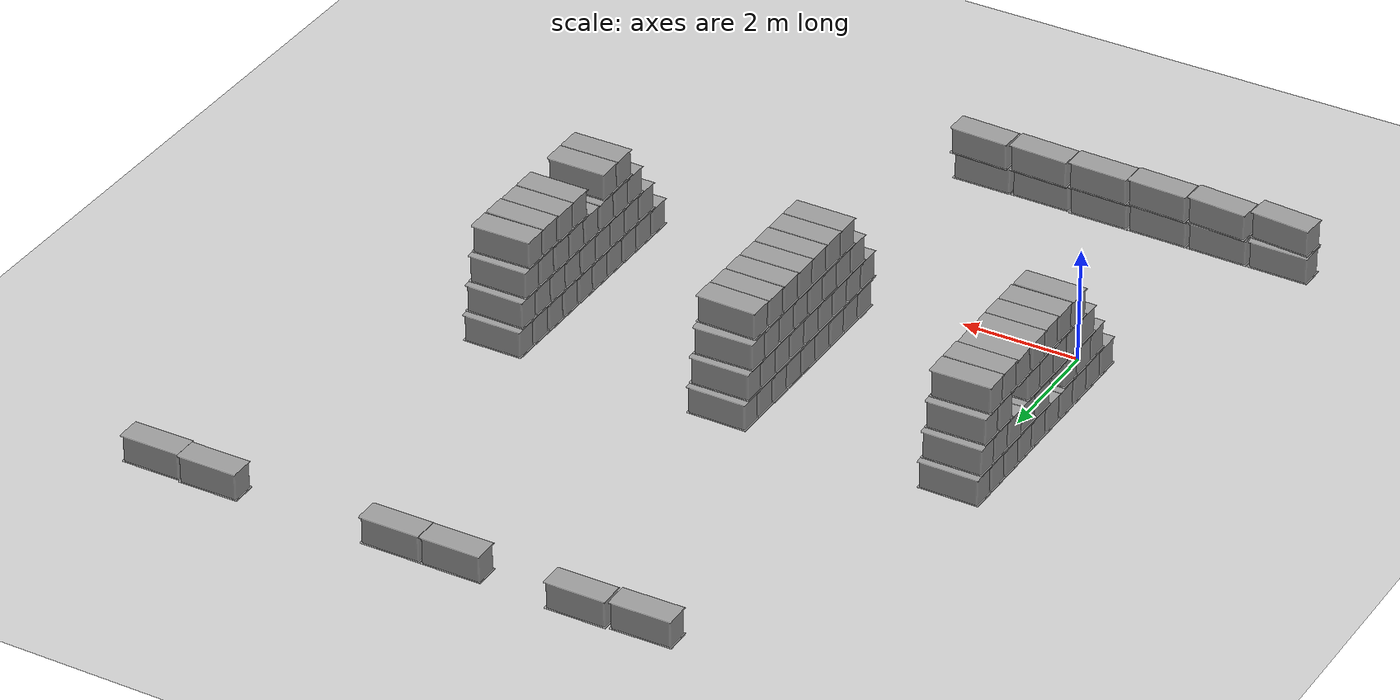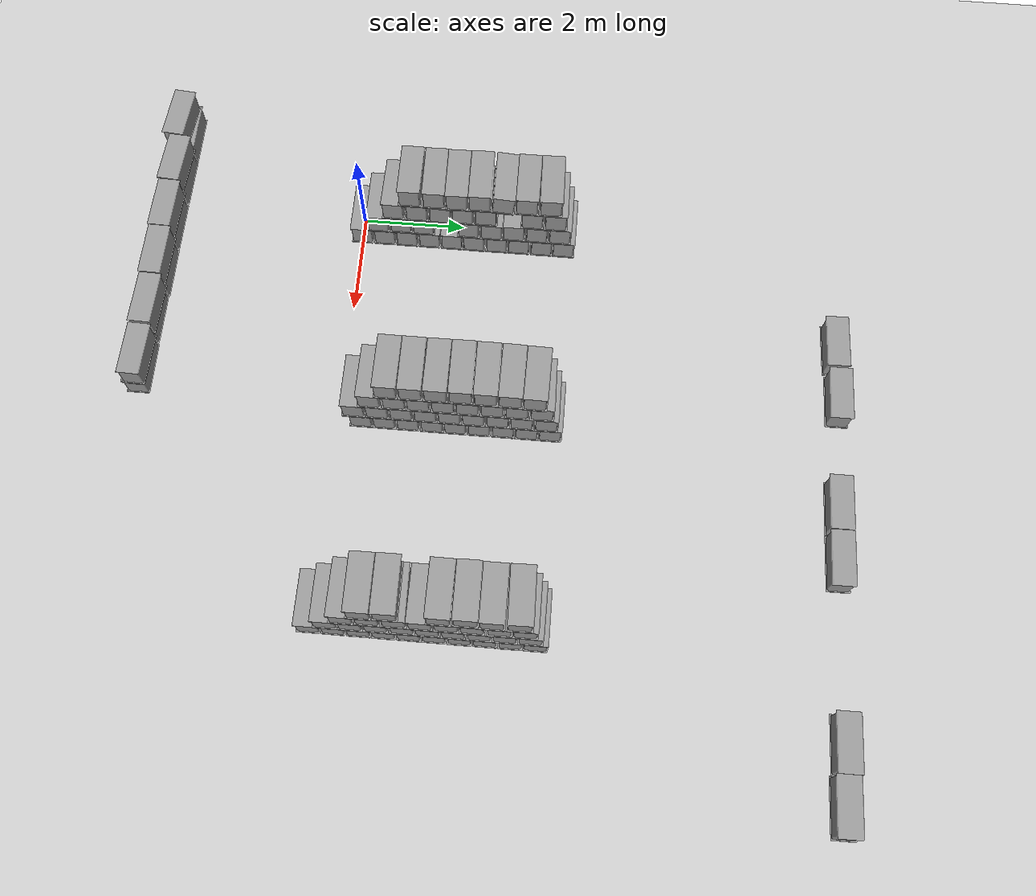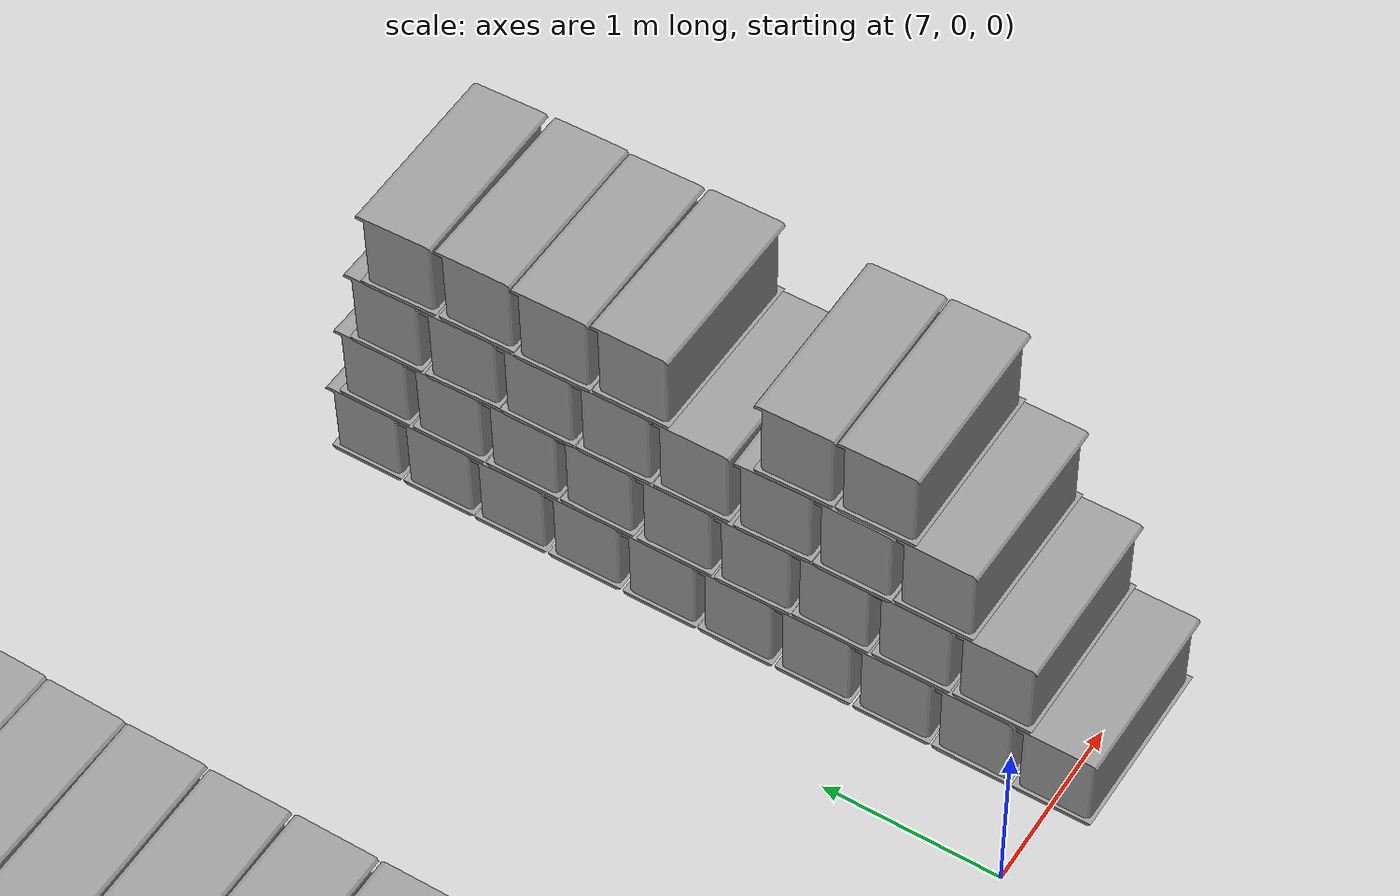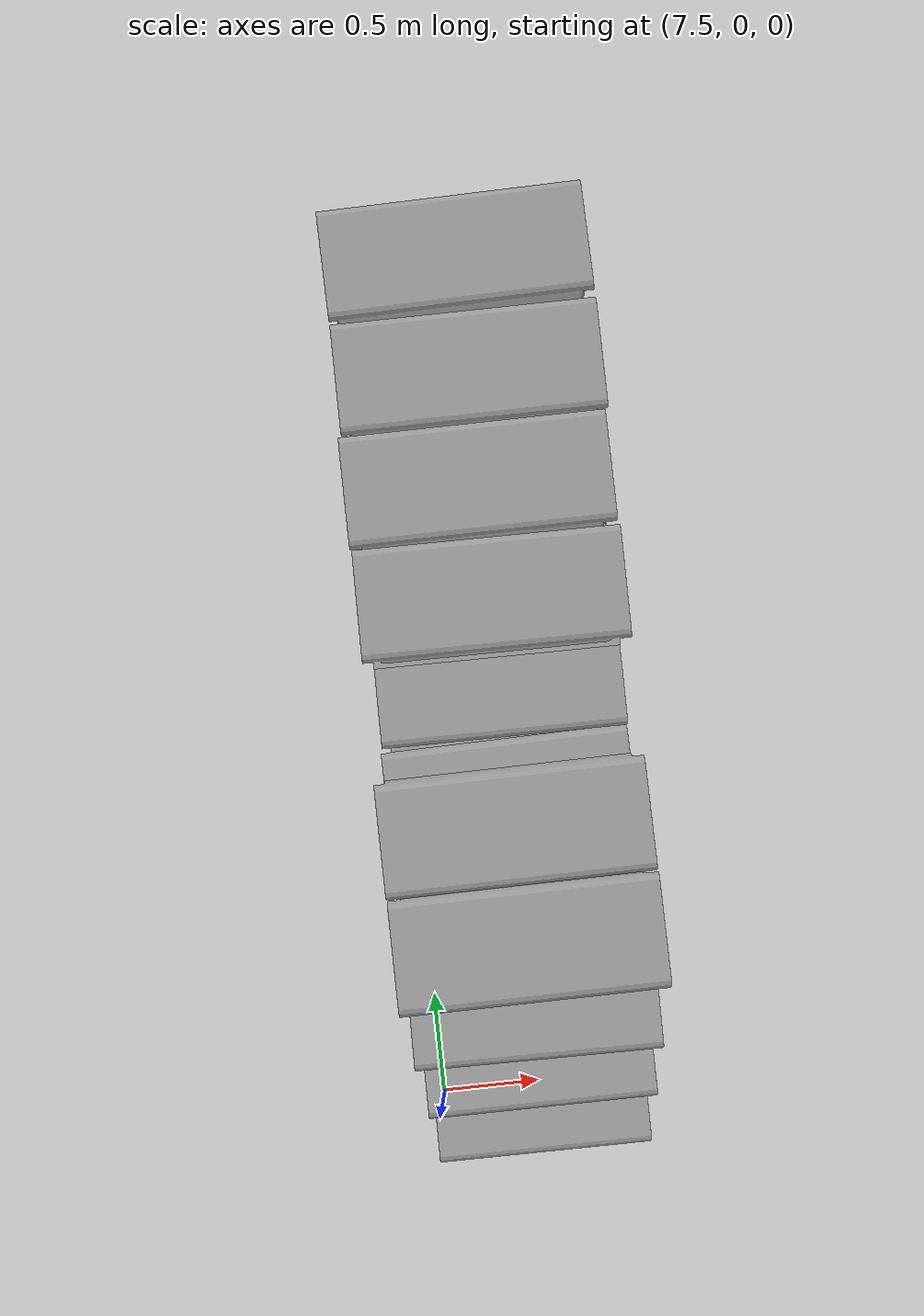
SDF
<sdf version="1.7">
 <world name="default">
  <model name="ground_plane">
   <static>1</static>
   <link name="link">
    <collision name="collision">
     <geometry><plane><normal>0 0 1</normal><size>100 100</size></plane></geometry>
     <surface><friction><ode><mu>100</mu><mu2>50</mu2></ode></friction></surface>
    </collision>
    <visual name="visual">
     <cast_shadows>0</cast_shadows>
     <geometry><plane><normal>0 0 1</normal><size>100 100</size></plane></geometry>
     <material>
      <script><uri>file://media/materials/scripts/gazebo.material</uri><name>Gazebo/Grey</name></script>
     </material>
    </visual>
   </link>
  </model>
  <gravity>0 0 -9.8</gravity>
  <magnetic_field>6e-06 2.3e-05 -4.2e-05</magnetic_field>
  <atmosphere type="adiabatic"/>
  <physics type="ode">
   <max_step_size>0.001</max_step_size>
   <real_time_factor>1</real_time_factor>
   <real_time_update_rate>1000</real_time_update_rate>
  </physics>
  <scene><ambient>0.4 0.4 0.4 1</ambient><background>0.7 0.7 0.7 1</background><shadows>1</shadows></scene>
  <spherical_coordinates>
   <surface_model>EARTH_WGS84</surface_model>
   <latitude_deg>0</latitude_deg>
   <longitude_deg>0</longitude_deg>
   <elevation>0</elevation>
   <heading_deg>0</heading_deg>
  </spherical_coordinates>
  <model name="my_robot1">
   <link name="link_0">
    <inertial>
     <mass>1</mass>
     <inertia>
      <ixx>0.166667</ixx>
      <ixy>0</ixy>
      <ixz>0</ixz>
      <iyy>0.166667</iyy>
      <iyz>0</iyz>
      <izz>0.166667</izz>
     </inertia>
    </inertial>
    <visual name="visual">
     <geometry><mesh><uri>/home/cyun/cotton_box.stl</uri><scale>1 1 1</scale></mesh></geometry>
     <material>
      <lighting>1</lighting>
      <script><uri>file://media/materials/scripts/gazebo.material</uri><name>Gazebo/Grey</name></script>
      <shader type="pixel"><normal_map>__default__</normal_map></shader>
      <ambient>0.3 0.3 0.3 1</ambient>
      <diffuse>0.7 0.7 0.7 1</diffuse>
      <specular>0.01 0.01 0.01 1</specular>
      <emissive>0 0 0 1</emissive>
     </material>
    </visual>
    <collision name="collision">
     <geometry><mesh><uri>/home/cyun/cotton_box.stl</uri><scale>1 1 1</scale></mesh></geometry>
     <surface>
      <friction>
       <ode><mu>1</mu><mu2>1</mu2><fdir1>0 0 0</fdir1><slip1>0</slip1><slip2>0</slip2></ode>
       <torsional>
        <coefficient>1</coefficient>
        <patch_radius>0</patch_radius>
        <surface_radius>0</surface_radius>
        <use_patch_radius>1</use_patch_radius>
        <ode><slip>0</slip></ode>
       </torsional>
      </friction>
      <bounce><restitution_coefficient>0</restitution_coefficient><threshold>1e+06</threshold></bounce>
      <contact>
       <collide_without_contact>0</collide_without_contact>
       <collide_without_contact_bitmask>1</collide_without_contact_bitmask>
       <collide_bitmask>1</collide_bitmask>
       <ode>
        <soft_cfm>0</soft_cfm>
        <soft_erp>0.2</soft_erp>
        <kp>1e+13</kp>
        <kd>1</kd>
        <max_vel>0.01</max_vel>
        <min_depth>0</min_depth>
       </ode>
       <bullet>
        <split_impulse>1</split_impulse>
        <split_impulse_penetration_threshold>-0.01</split_impulse_penetration_threshold>
        <soft_cfm>0</soft_cfm>
        <soft_erp>0.2</soft_erp>
        <kp>1e+13</kp>
        <kd>1</kd>
       </bullet>
      </contact>
     </surface>
    </collision>
   </link>
   <static>0</static>
   <pose>-0.000505 -0.001454 0.01988 -5e-06 9e-06 1.56865</pose>
  </model>
  <model name="my_robot2">
   <link name="link_0">
    <inertial>
     <mass>1</mass>
     <inertia>
      <ixx>0.166667</ixx>
      <ixy>0</ixy>
      <ixz>0</ixz>
      <iyy>0.166667</iyy>
      <iyz>0</iyz>
      <izz>0.166667</izz>
     </inertia>
    </inertial>
    <visual name="visual">
     <geometry><mesh><uri>/home/cyun/cotton_box.stl</uri><scale>1 1 1</scale></mesh></geometry>
     <material>
      <lighting>1</lighting>
      <script><uri>file://media/materials/scripts/gazebo.material</uri><name>Gazebo/Grey</name></script>
      <shader type="pixel"><normal_map>__default__</normal_map></shader>
      <ambient>0.3 0.3 0.3 1</ambient>
      <diffuse>0.7 0.7 0.7 1</diffuse>
      <specular>0.01 0.01 0.01 1</specular>
      <emissive>0 0 0 1</emissive>
     </material>
    </visual>
    <collision name="collision">
     <geometry><mesh><uri>/home/cyun/cotton_box.stl</uri><scale>1 1 1</scale></mesh></geometry>
     <surface>
      <friction>
       <ode><mu>1</mu><mu2>1</mu2><fdir1>0 0 0</fdir1><slip1>0</slip1><slip2>0</slip2></ode>
       <torsional>
        <coefficient>1</coefficient>
        <patch_radius>0</patch_radius>
        <surface_radius>0</surface_radius>
        <use_patch_radius>1</use_patch_radius>
        <ode><slip>0</slip></ode>
       </torsional>
      </friction>
      <bounce><restitution_coefficient>0</restitution_coefficient><threshold>1e+06</threshold></bounce>
      <contact>
       <collide_without_contact>0</collide_without_contact>
       <collide_without_contact_bitmask>1</collide_without_contact_bitmask>
       <collide_bitmask>1</collide_bitmask>
       <ode>
        <soft_cfm>0</soft_cfm>
        <soft_erp>0.2</soft_erp>
        <kp>1e+13</kp>
        <kd>1</kd>
        <max_vel>0.01</max_vel>
        <min_depth>0</min_depth>
       </ode>
       <bullet>
        <split_impulse>1</split_impulse>
        <split_impulse_penetration_threshold>-0.01</split_impulse_penetration_threshold>
        <soft_cfm>0</soft_cfm>
        <soft_erp>0.2</soft_erp>
        <kp>1e+13</kp>
        <kd>1</kd>
       </bullet>
      </contact>
     </surface>
    </collision>
   </link>
   <static>0</static>
   <pose>-0.000211 0.452009 0.01997 -1e-05 1.1e-05 1.57701</pose>
  </model>
  <model name="my_robot3">
   <link name="link_0">
    <inertial>
     <mass>1</mass>
     <inertia>
      <ixx>0.166667</ixx>
      <ixy>0</ixy>
      <ixz>0</ixz>
      <iyy>0.166667</iyy>
      <iyz>0</iyz>
      <izz>0.166667</izz>
     </inertia>
    </inertial>
    <visual name="visual">
     <geometry><mesh><uri>/home/cyun/cotton_box.stl</uri><scale>1 1 1</scale></mesh></geometry>
     <material>
      <lighting>1</lighting>
      <script><uri>file://media/materials/scripts/gazebo.material</uri><name>Gazebo/Grey</name></script>
      <shader type="pixel"><normal_map>__default__</normal_map></shader>
      <ambient>0.3 0.3 0.3 1</ambient>
      <diffuse>0.7 0.7 0.7 1</diffuse>
      <specular>0.01 0.01 0.01 1</specular>
      <emissive>0 0 0 1</emissive>
     </material>
    </visual>
    <collision name="collision">
     <geometry><mesh><uri>/home/cyun/cotton_box.stl</uri><scale>1 1 1</scale></mesh></geometry>
     <surface>
      <friction>
       <ode><mu>1</mu><mu2>1</mu2><fdir1>0 0 0</fdir1><slip1>0</slip1><slip2>0</slip2></ode>
       <torsional>
        <coefficient>1</coefficient>
        <patch_radius>0</patch_radius>
        <surface_radius>0</surface_radius>
        <use_patch_radius>1</use_patch_radius>
        <ode><slip>0</slip></ode>
       </torsional>
      </friction>
      <bounce><restitution_coefficient>0</restitution_coefficient><threshold>1e+06</threshold></bounce>
      <contact>
       <collide_without_contact>0</collide_without_contact>
       <collide_without_contact_bitmask>1</collide_without_contact_bitmask>
       <collide_bitmask>1</collide_bitmask>
       <ode>
        <soft_cfm>0</soft_cfm>
        <soft_erp>0.2</soft_erp>
        <kp>1e+13</kp>
        <kd>1</kd>
        <max_vel>0.01</max_vel>
        <min_depth>0</min_depth>
       </ode>
       <bullet>
        <split_impulse>1</split_impulse>
        <split_impulse_penetration_threshold>-0.01</split_impulse_penetration_threshold>
        <soft_cfm>0</soft_cfm>
        <soft_erp>0.2</soft_erp>
        <kp>1e+13</kp>
        <kd>1</kd>
       </bullet>
      </contact>
     </surface>
    </collision>
   </link>
   <static>0</static>
   <pose>0.00046 0.899927 0.019881 7e-06 5.6e-05 1.57327</pose>
  </model>
  <model name="my_robot4">
   <link name="link_0">
    <inertial>
     <mass>1</mass>
     <inertia>
      <ixx>0.166667</ixx>
      <ixy>0</ixy>
      <ixz>0</ixz>
      <iyy>0.166667</iyy>
      <iyz>0</iyz>
      <izz>0.166667</izz>
     </inertia>
    </inertial>
    <visual name="visual">
     <geometry><mesh><uri>/home/cyun/cotton_box.stl</uri><scale>1 1 1</scale></mesh></geometry>
     <material>
      <lighting>1</lighting>
      <script><uri>file://media/materials/scripts/gazebo.material</uri><name>Gazebo/Grey</name></script>
      <shader type="pixel"><normal_map>__default__</normal_map></shader>
      <ambient>0.3 0.3 0.3 1</ambient>
      <diffuse>0.7 0.7 0.7 1</diffuse>
      <specular>0.01 0.01 0.01 1</specular>
      <emissive>0 0 0 1</emissive>
     </material>
    </visual>
    <collision name="collision">
     <geometry><mesh><uri>/home/cyun/cotton_box.stl</uri><scale>1 1 1</scale></mesh></geometry>
     <surface>
      <friction>
       <ode><mu>1</mu><mu2>1</mu2><fdir1>0 0 0</fdir1><slip1>0</slip1><slip2>0</slip2></ode>
       <torsional>
        <coefficient>1</coefficient>
        <patch_radius>0</patch_radius>
        <surface_radius>0</surface_radius>
        <use_patch_radius>1</use_patch_radius>
        <ode><slip>0</slip></ode>
       </torsional>
      </friction>
      <bounce><restitution_coefficient>0</restitution_coefficient><threshold>1e+06</threshold></bounce>
      <contact>
       <collide_without_contact>0</collide_without_contact>
       <collide_without_contact_bitmask>1</collide_without_contact_bitmask>
       <collide_bitmask>1</collide_bitmask>
       <ode>
        <soft_cfm>0</soft_cfm>
        <soft_erp>0.2</soft_erp>
        <kp>1e+13</kp>
        <kd>1</kd>
        <max_vel>0.01</max_vel>
        <min_depth>0</min_depth>
       </ode>
       <bullet>
        <split_impulse>1</split_impulse>
        <split_impulse_penetration_threshold>-0.01</split_impulse_penetration_threshold>
        <soft_cfm>0</soft_cfm>
        <soft_erp>0.2</soft_erp>
        <kp>1e+13</kp>
        <kd>1</kd>
       </bullet>
      </contact>
     </surface>
    </collision>
   </link>
   <static>0</static>
   <pose>-0.000647 1.35324 0.019788 1e-05 -0 1.57648</pose>
  </model>
  <model name="my_robot5">
   <link name="link_0">
    <inertial>
     <mass>1</mass>
     <inertia>
      <ixx>0.166667</ixx>
      <ixy>0</ixy>
      <ixz>0</ixz>
      <iyy>0.166667</iyy>
      <iyz>0</iyz>
      <izz>0.166667</izz>
     </inertia>
    </inertial>
    <visual name="visual">
     <geometry><mesh><uri>/home/cyun/cotton_box.stl</uri><scale>1 1 1</scale></mesh></geometry>
     <material>
      <lighting>1</lighting>
      <script><uri>file://media/materials/scripts/gazebo.material</uri><name>Gazebo/Grey</name></script>
      <shader type="pixel"><normal_map>__default__</normal_map></shader>
      <ambient>0.3 0.3 0.3 1</ambient>
      <diffuse>0.7 0.7 0.7 1</diffuse>
      <specular>0.01 0.01 0.01 1</specular>
      <emissive>0 0 0 1</emissive>
     </material>
    </visual>
    <collision name="collision">
     <geometry><mesh><uri>/home/cyun/cotton_box.stl</uri><scale>1 1 1</scale></mesh></geometry>
     <surface>
      <friction>
       <ode><mu>1</mu><mu2>1</mu2><fdir1>0 0 0</fdir1><slip1>0</slip1><slip2>0</slip2></ode>
       <torsional>
        <coefficient>1</coefficient>
        <patch_radius>0</patch_radius>
        <surface_radius>0</surface_radius>
        <use_patch_radius>1</use_patch_radius>
        <ode><slip>0</slip></ode>
       </torsional>
      </friction>
      <bounce><restitution_coefficient>0</restitution_coefficient><threshold>1e+06</threshold></bounce>
      <contact>
       <collide_without_contact>0</collide_without_contact>
       <collide_without_contact_bitmask>1</collide_without_contact_bitmask>
       <collide_bitmask>1</collide_bitmask>
       <ode>
        <soft_cfm>0</soft_cfm>
        <soft_erp>0.2</soft_erp>
        <kp>1e+13</kp>
        <kd>1</kd>
        <max_vel>0.01</max_vel>
        <min_depth>0</min_depth>
       </ode>
       <bullet>
        <split_impulse>1</split_impulse>
        <split_impulse_penetration_threshold>-0.01</split_impulse_penetration_threshold>
        <soft_cfm>0</soft_cfm>
        <soft_erp>0.2</soft_erp>
        <kp>1e+13</kp>
        <kd>1</kd>
       </bullet>
      </contact>
     </surface>
    </collision>
   </link>
   <static>0</static>
   <pose>0.002436 1.80378 0.01967 0.000155 8.7e-05 1.57416</pose>
  </model>
  <model name="my_robot6">
   <link name="link_0">
    <inertial>
     <mass>1</mass>
     <inertia>
      <ixx>0.166667</ixx>
      <ixy>0</ixy>
      <ixz>0</ixz>
      <iyy>0.166667</iyy>
      <iyz>0</iyz>
      <izz>0.166667</izz>
     </inertia>
    </inertial>
    <visual name="visual">
     <geometry><mesh><uri>/home/cyun/cotton_box.stl</uri><scale>1 1 1</scale></mesh></geometry>
     <material>
      <lighting>1</lighting>
      <script><uri>file://media/materials/scripts/gazebo.material</uri><name>Gazebo/Grey</name></script>
      <shader type="pixel"><normal_map>__default__</normal_map></shader>
      <ambient>0.3 0.3 0.3 1</ambient>
      <diffuse>0.7 0.7 0.7 1</diffuse>
      <specular>0.01 0.01 0.01 1</specular>
      <emissive>0 0 0 1</emissive>
     </material>
    </visual>
    <collision name="collision">
     <geometry><mesh><uri>/home/cyun/cotton_box.stl</uri><scale>1 1 1</scale></mesh></geometry>
     <surface>
      <friction>
       <ode><mu>1</mu><mu2>1</mu2><fdir1>0 0 0</fdir1><slip1>0</slip1><slip2>0</slip2></ode>
       <torsional>
        <coefficient>1</coefficient>
        <patch_radius>0</patch_radius>
        <surface_radius>0</surface_radius>
        <use_patch_radius>1</use_patch_radius>
        <ode><slip>0</slip></ode>
       </torsional>
      </friction>
      <bounce><restitution_coefficient>0</restitution_coefficient><threshold>1e+06</threshold></bounce>
      <contact>
       <collide_without_contact>0</collide_without_contact>
       <collide_without_contact_bitmask>1</collide_without_contact_bitmask>
       <collide_bitmask>1</collide_bitmask>
       <ode>
        <soft_cfm>0</soft_cfm>
        <soft_erp>0.2</soft_erp>
        <kp>1e+13</kp>
        <kd>1</kd>
        <max_vel>0.01</max_vel>
        <min_depth>0</min_depth>
       </ode>
       <bullet>
        <split_impulse>1</split_impulse>
        <split_impulse_penetration_threshold>-0.01</split_impulse_penetration_threshold>
        <soft_cfm>0</soft_cfm>
        <soft_erp>0.2</soft_erp>
        <kp>1e+13</kp>
        <kd>1</kd>
       </bullet>
      </contact>
     </surface>
    </collision>
   </link>
   <static>0</static>
   <pose>0.002568 2.25084 0.019393 -8.7e-05 0.000153 1.56432</pose>
  </model>
  <model name="my_robot7">
   <link name="link_0">
    <inertial>
     <mass>1</mass>
     <inertia>
      <ixx>0.166667</ixx>
      <ixy>0</ixy>
      <ixz>0</ixz>
      <iyy>0.166667</iyy>
      <iyz>0</iyz>
      <izz>0.166667</izz>
     </inertia>
    </inertial>
    <visual name="visual">
     <geometry><mesh><uri>/home/cyun/cotton_box.stl</uri><scale>1 1 1</scale></mesh></geometry>
     <material>
      <lighting>1</lighting>
      <script><uri>file://media/materials/scripts/gazebo.material</uri><name>Gazebo/Grey</name></script>
      <shader type="pixel"><normal_map>__default__</normal_map></shader>
      <ambient>0.3 0.3 0.3 1</ambient>
      <diffuse>0.7 0.7 0.7 1</diffuse>
      <specular>0.01 0.01 0.01 1</specular>
      <emissive>0 0 0 1</emissive>
     </material>
    </visual>
    <collision name="collision">
     <geometry><mesh><uri>/home/cyun/cotton_box.stl</uri><scale>1 1 1</scale></mesh></geometry>
     <surface>
      <friction>
       <ode><mu>1</mu><mu2>1</mu2><fdir1>0 0 0</fdir1><slip1>0</slip1><slip2>0</slip2></ode>
       <torsional>
        <coefficient>1</coefficient>
        <patch_radius>0</patch_radius>
        <surface_radius>0</surface_radius>
        <use_patch_radius>1</use_patch_radius>
        <ode><slip>0</slip></ode>
       </torsional>
      </friction>
      <bounce><restitution_coefficient>0</restitution_coefficient><threshold>1e+06</threshold></bounce>
      <contact>
       <collide_without_contact>0</collide_without_contact>
       <collide_without_contact_bitmask>1</collide_without_contact_bitmask>
       <collide_bitmask>1</collide_bitmask>
       <ode>
        <soft_cfm>0</soft_cfm>
        <soft_erp>0.2</soft_erp>
        <kp>1e+13</kp>
        <kd>1</kd>
        <max_vel>0.01</max_vel>
        <min_depth>0</min_depth>
       </ode>
       <bullet>
        <split_impulse>1</split_impulse>
        <split_impulse_penetration_threshold>-0.01</split_impulse_penetration_threshold>
        <soft_cfm>0</soft_cfm>
        <soft_erp>0.2</soft_erp>
        <kp>1e+13</kp>
        <kd>1</kd>
       </bullet>
      </contact>
     </surface>
    </collision>
   </link>
   <static>0</static>
   <pose>0.000808 2.70308 0.020218 0.000181 0.000708 1.57963</pose>
  </model>
  <model name="my_robot8">
   <link name="link_0">
    <inertial>
     <mass>1</mass>
     <inertia>
      <ixx>0.166667</ixx>
      <ixy>0</ixy>
      <ixz>0</ixz>
      <iyy>0.166667</iyy>
      <iyz>0</iyz>
      <izz>0.166667</izz>
     </inertia>
    </inertial>
    <visual name="visual">
     <geometry><mesh><uri>/home/cyun/cotton_box.stl</uri><scale>1 1 1</scale></mesh></geometry>
     <material>
      <lighting>1</lighting>
      <script><uri>file://media/materials/scripts/gazebo.material</uri><name>Gazebo/Grey</name></script>
      <shader type="pixel"><normal_map>__default__</normal_map></shader>
      <ambient>0.3 0.3 0.3 1</ambient>
      <diffuse>0.7 0.7 0.7 1</diffuse>
      <specular>0.01 0.01 0.01 1</specular>
      <emissive>0 0 0 1</emissive>
     </material>
    </visual>
    <collision name="collision">
     <geometry><mesh><uri>/home/cyun/cotton_box.stl</uri><scale>1 1 1</scale></mesh></geometry>
     <surface>
      <friction>
       <ode><mu>1</mu><mu2>1</mu2><fdir1>0 0 0</fdir1><slip1>0</slip1><slip2>0</slip2></ode>
       <torsional>
        <coefficient>1</coefficient>
        <patch_radius>0</patch_radius>
        <surface_radius>0</surface_radius>
        <use_patch_radius>1</use_patch_radius>
        <ode><slip>0</slip></ode>
       </torsional>
      </friction>
      <bounce><restitution_coefficient>0</restitution_coefficient><threshold>1e+06</threshold></bounce>
      <contact>
       <collide_without_contact>0</collide_without_contact>
       <collide_without_contact_bitmask>1</collide_without_contact_bitmask>
       <collide_bitmask>1</collide_bitmask>
       <ode>
        <soft_cfm>0</soft_cfm>
        <soft_erp>0.2</soft_erp>
        <kp>1e+13</kp>
        <kd>1</kd>
        <max_vel>0.01</max_vel>
        <min_depth>0</min_depth>
       </ode>
       <bullet>
        <split_impulse>1</split_impulse>
        <split_impulse_penetration_threshold>-0.01</split_impulse_penetration_threshold>
        <soft_cfm>0</soft_cfm>
        <soft_erp>0.2</soft_erp>
        <kp>1e+13</kp>
        <kd>1</kd>
       </bullet>
      </contact>
     </surface>
    </collision>
   </link>
   <static>0</static>
   <pose>-0.001761 3.15029 0.02 -2e-06 -1e-06 1.57546</pose>
  </model>
  <model name="my_robot9">
   <link name="link_0">
    <inertial>
     <mass>1</mass>
     <inertia>
      <ixx>0.166667</ixx>
      <ixy>0</ixy>
      <ixz>0</ixz>
      <iyy>0.166667</iyy>
      <iyz>0</iyz>
      <izz>0.166667</izz>
     </inertia>
    </inertial>
    <visual name="visual">
     <geometry><mesh><uri>/home/cyun/cotton_box.stl</uri><scale>1 1 1</scale></mesh></geometry>
     <material>
      <lighting>1</lighting>
      <script><uri>file://media/materials/scripts/gazebo.material</uri><name>Gazebo/Grey</name></script>
      <shader type="pixel"><normal_map>__default__</normal_map></shader>
      <ambient>0.3 0.3 0.3 1</ambient>
      <diffuse>0.7 0.7 0.7 1</diffuse>
      <specular>0.01 0.01 0.01 1</specular>
      <emissive>0 0 0 1</emissive>
     </material>
    </visual>
    <collision name="collision">
     <geometry><mesh><uri>/home/cyun/cotton_box.stl</uri><scale>1 1 1</scale></mesh></geometry>
     <surface>
      <friction>
       <ode><mu>1</mu><mu2>1</mu2><fdir1>0 0 0</fdir1><slip1>0</slip1><slip2>0</slip2></ode>
       <torsional>
        <coefficient>1</coefficient>
        <patch_radius>0</patch_radius>
        <surface_radius>0</surface_radius>
        <use_patch_radius>1</use_patch_radius>
        <ode><slip>0</slip></ode>
       </torsional>
      </friction>
      <bounce><restitution_coefficient>0</restitution_coefficient><threshold>1e+06</threshold></bounce>
      <contact>
       <collide_without_contact>0</collide_without_contact>
       <collide_without_contact_bitmask>1</collide_without_contact_bitmask>
       <collide_bitmask>1</collide_bitmask>
       <ode>
        <soft_cfm>0</soft_cfm>
        <soft_erp>0.2</soft_erp>
        <kp>1e+13</kp>
        <kd>1</kd>
        <max_vel>0.01</max_vel>
        <min_depth>0</min_depth>
       </ode>
       <bullet>
        <split_impulse>1</split_impulse>
        <split_impulse_penetration_threshold>-0.01</split_impulse_penetration_threshold>
        <soft_cfm>0</soft_cfm>
        <soft_erp>0.2</soft_erp>
        <kp>1e+13</kp>
        <kd>1</kd>
       </bullet>
      </contact>
     </surface>
    </collision>
   </link>
   <static>0</static>
   <pose>-0.000303 3.6022 0.019902 0.000213 0.000655 1.57922</pose>
  </model>
  <model name="my_robot10">
   <link name="link_0">
    <inertial>
     <mass>1</mass>
     <inertia>
      <ixx>0.166667</ixx>
      <ixy>0</ixy>
      <ixz>0</ixz>
      <iyy>0.166667</iyy>
      <iyz>0</iyz>
      <izz>0.166667</izz>
     </inertia>
    </inertial>
    <visual name="visual">
     <geometry><mesh><uri>/home/cyun/cotton_box.stl</uri><scale>1 1 1</scale></mesh></geometry>
     <material>
      <lighting>1</lighting>
      <script><uri>file://media/materials/scripts/gazebo.material</uri><name>Gazebo/Grey</name></script>
      <shader type="pixel"><normal_map>__default__</normal_map></shader>
      <ambient>0.3 0.3 0.3 1</ambient>
      <diffuse>0.7 0.7 0.7 1</diffuse>
      <specular>0.01 0.01 0.01 1</specular>
      <emissive>0 0 0 1</emissive>
     </material>
    </visual>
    <collision name="collision">
     <geometry><mesh><uri>/home/cyun/cotton_box.stl</uri><scale>1 1 1</scale></mesh></geometry>
     <surface>
      <friction>
       <ode><mu>1</mu><mu2>1</mu2><fdir1>0 0 0</fdir1><slip1>0</slip1><slip2>0</slip2></ode>
       <torsional>
        <coefficient>1</coefficient>
        <patch_radius>0</patch_radius>
        <surface_radius>0</surface_radius>
        <use_patch_radius>1</use_patch_radius>
        <ode><slip>0</slip></ode>
       </torsional>
      </friction>
      <bounce><restitution_coefficient>0</restitution_coefficient><threshold>1e+06</threshold></bounce>
      <contact>
       <collide_without_contact>0</collide_without_contact>
       <collide_without_contact_bitmask>1</collide_without_contact_bitmask>
       <collide_bitmask>1</collide_bitmask>
       <ode>
        <soft_cfm>0</soft_cfm>
        <soft_erp>0.2</soft_erp>
        <kp>1e+13</kp>
        <kd>1</kd>
        <max_vel>0.01</max_vel>
        <min_depth>0</min_depth>
       </ode>
       <bullet>
        <split_impulse>1</split_impulse>
        <split_impulse_penetration_threshold>-0.01</split_impulse_penetration_threshold>
        <soft_cfm>0</soft_cfm>
        <soft_erp>0.2</soft_erp>
        <kp>1e+13</kp>
        <kd>1</kd>
       </bullet>
      </contact>
     </surface>
    </collision>
   </link>
   <static>0</static>
   <pose>0.001042 4.04938 0.019956 5e-06 2.8e-05 1.56739</pose>
  </model>
  <model name="my_robot11">
   <link name="link_0">
    <inertial>
     <mass>1</mass>
     <inertia>
      <ixx>0.166667</ixx>
      <ixy>0</ixy>
      <ixz>0</ixz>
      <iyy>0.166667</iyy>
      <iyz>0</iyz>
      <izz>0.166667</izz>
     </inertia>
    </inertial>
    <visual name="visual">
     <geometry><mesh><uri>/home/cyun/cotton_box.stl</uri><scale>1 1 1</scale></mesh></geometry>
     <material>
      <lighting>1</lighting>
      <script><uri>file://media/materials/scripts/gazebo.material</uri><name>Gazebo/Grey</name></script>
      <shader type="pixel"><normal_map>__default__</normal_map></shader>
      <ambient>0.3 0.3 0.3 1</ambient>
      <diffuse>0.7 0.7 0.7 1</diffuse>
      <specular>0.01 0.01 0.01 1</specular>
      <emissive>0 0 0 1</emissive>
     </material>
    </visual>
    <collision name="collision">
     <geometry><mesh><uri>/home/cyun/cotton_box.stl</uri><scale>1 1 1</scale></mesh></geometry>
     <surface>
      <friction>
       <ode><mu>1</mu><mu2>1</mu2><fdir1>0 0 0</fdir1><slip1>0</slip1><slip2>0</slip2></ode>
       <torsional>
        <coefficient>1</coefficient>
        <patch_radius>0</patch_radius>
        <surface_radius>0</surface_radius>
        <use_patch_radius>1</use_patch_radius>
        <ode><slip>0</slip></ode>
       </torsional>
      </friction>
      <bounce><restitution_coefficient>0</restitution_coefficient><threshold>1e+06</threshold></bounce>
      <contact>
       <collide_without_contact>0</collide_without_contact>
       <collide_without_contact_bitmask>1</collide_without_contact_bitmask>
       <collide_bitmask>1</collide_bitmask>
       <ode>
        <soft_cfm>0</soft_cfm>
        <soft_erp>0.2</soft_erp>
        <kp>1e+13</kp>
        <kd>1</kd>
        <max_vel>0.01</max_vel>
        <min_depth>0</min_depth>
       </ode>
       <bullet>
        <split_impulse>1</split_impulse>
        <split_impulse_penetration_threshold>-0.01</split_impulse_penetration_threshold>
        <soft_cfm>0</soft_cfm>
        <soft_erp>0.2</soft_erp>
        <kp>1e+13</kp>
        <kd>1</kd>
       </bullet>
      </contact>
     </surface>
    </collision>
   </link>
   <static>0</static>
   <pose>0.007207 0.353604 0.50995 -6e-06 -7e-06 1.5736</pose>
  </model>
  <model name="my_robot12">
   <link name="link_0">
    <inertial>
     <mass>1</mass>
     <inertia>
      <ixx>0.166667</ixx>
      <ixy>0</ixy>
      <ixz>0</ixz>
      <iyy>0.166667</iyy>
      <iyz>0</iyz>
      <izz>0.166667</izz>
     </inertia>
    </inertial>
    <visual name="visual">
     <geometry><mesh><uri>/home/cyun/cotton_box.stl</uri><scale>1 1 1</scale></mesh></geometry>
     <material>
      <lighting>1</lighting>
      <script><uri>file://media/materials/scripts/gazebo.material</uri><name>Gazebo/Grey</name></script>
      <shader type="pixel"><normal_map>__default__</normal_map></shader>
      <ambient>0.3 0.3 0.3 1</ambient>
      <diffuse>0.7 0.7 0.7 1</diffuse>
      <specular>0.01 0.01 0.01 1</specular>
      <emissive>0 0 0 1</emissive>
     </material>
    </visual>
    <collision name="collision">
     <geometry><mesh><uri>/home/cyun/cotton_box.stl</uri><scale>1 1 1</scale></mesh></geometry>
     <surface>
      <friction>
       <ode><mu>1</mu><mu2>1</mu2><fdir1>0 0 0</fdir1><slip1>0</slip1><slip2>0</slip2></ode>
       <torsional>
        <coefficient>1</coefficient>
        <patch_radius>0</patch_radius>
        <surface_radius>0</surface_radius>
        <use_patch_radius>1</use_patch_radius>
        <ode><slip>0</slip></ode>
       </torsional>
      </friction>
      <bounce><restitution_coefficient>0</restitution_coefficient><threshold>1e+06</threshold></bounce>
      <contact>
       <collide_without_contact>0</collide_without_contact>
       <collide_without_contact_bitmask>1</collide_without_contact_bitmask>
       <collide_bitmask>1</collide_bitmask>
       <ode>
        <soft_cfm>0</soft_cfm>
        <soft_erp>0.2</soft_erp>
        <kp>1e+13</kp>
        <kd>1</kd>
        <max_vel>0.01</max_vel>
        <min_depth>0</min_depth>
       </ode>
       <bullet>
        <split_impulse>1</split_impulse>
        <split_impulse_penetration_threshold>-0.01</split_impulse_penetration_threshold>
        <soft_cfm>0</soft_cfm>
        <soft_erp>0.2</soft_erp>
        <kp>1e+13</kp>
        <kd>1</kd>
       </bullet>
      </contact>
     </surface>
    </collision>
   </link>
   <static>0</static>
   <pose>-0.00613 0.799123 0.509904 -5e-06 0.000201 1.58403</pose>
  </model>
  <model name="my_robot13">
   <link name="link_0">
    <inertial>
     <mass>1</mass>
     <inertia>
      <ixx>0.166667</ixx>
      <ixy>0</ixy>
      <ixz>0</ixz>
      <iyy>0.166667</iyy>
      <iyz>0</iyz>
      <izz>0.166667</izz>
     </inertia>
    </inertial>
    <visual name="visual">
     <geometry><mesh><uri>/home/cyun/cotton_box.stl</uri><scale>1 1 1</scale></mesh></geometry>
     <material>
      <lighting>1</lighting>
      <script><uri>file://media/materials/scripts/gazebo.material</uri><name>Gazebo/Grey</name></script>
      <shader type="pixel"><normal_map>__default__</normal_map></shader>
      <ambient>0.3 0.3 0.3 1</ambient>
      <diffuse>0.7 0.7 0.7 1</diffuse>
      <specular>0.01 0.01 0.01 1</specular>
      <emissive>0 0 0 1</emissive>
     </material>
    </visual>
    <collision name="collision">
     <geometry><mesh><uri>/home/cyun/cotton_box.stl</uri><scale>1 1 1</scale></mesh></geometry>
     <surface>
      <friction>
       <ode><mu>1</mu><mu2>1</mu2><fdir1>0 0 0</fdir1><slip1>0</slip1><slip2>0</slip2></ode>
       <torsional>
        <coefficient>1</coefficient>
        <patch_radius>0</patch_radius>
        <surface_radius>0</surface_radius>
        <use_patch_radius>1</use_patch_radius>
        <ode><slip>0</slip></ode>
       </torsional>
      </friction>
      <bounce><restitution_coefficient>0</restitution_coefficient><threshold>1e+06</threshold></bounce>
      <contact>
       <collide_without_contact>0</collide_without_contact>
       <collide_without_contact_bitmask>1</collide_without_contact_bitmask>
       <collide_bitmask>1</collide_bitmask>
       <ode>
        <soft_cfm>0</soft_cfm>
        <soft_erp>0.2</soft_erp>
        <kp>1e+13</kp>
        <kd>1</kd>
        <max_vel>0.01</max_vel>
        <min_depth>0</min_depth>
       </ode>
       <bullet>
        <split_impulse>1</split_impulse>
        <split_impulse_penetration_threshold>-0.01</split_impulse_penetration_threshold>
        <soft_cfm>0</soft_cfm>
        <soft_erp>0.2</soft_erp>
        <kp>1e+13</kp>
        <kd>1</kd>
       </bullet>
      </contact>
     </surface>
    </collision>
   </link>
   <static>0</static>
   <pose>0.002688 1.25131 0.509725 3.3e-05 0.000266 1.57523</pose>
  </model>
  <model name="my_robot15">
   <link name="link_0">
    <inertial>
     <mass>1</mass>
     <inertia>
      <ixx>0.166667</ixx>
      <ixy>0</ixy>
      <ixz>0</ixz>
      <iyy>0.166667</iyy>
      <iyz>0</iyz>
      <izz>0.166667</izz>
     </inertia>
    </inertial>
    <visual name="visual">
     <geometry><mesh><uri>/home/cyun/cotton_box.stl</uri><scale>1 1 1</scale></mesh></geometry>
     <material>
      <lighting>1</lighting>
      <script><uri>file://media/materials/scripts/gazebo.material</uri><name>Gazebo/Grey</name></script>
      <shader type="pixel"><normal_map>__default__</normal_map></shader>
      <ambient>0.3 0.3 0.3 1</ambient>
      <diffuse>0.7 0.7 0.7 1</diffuse>
      <specular>0.01 0.01 0.01 1</specular>
      <emissive>0 0 0 1</emissive>
     </material>
    </visual>
    <collision name="collision">
     <geometry><mesh><uri>/home/cyun/cotton_box.stl</uri><scale>1 1 1</scale></mesh></geometry>
     <surface>
      <friction>
       <ode><mu>1</mu><mu2>1</mu2><fdir1>0 0 0</fdir1><slip1>0</slip1><slip2>0</slip2></ode>
       <torsional>
        <coefficient>1</coefficient>
        <patch_radius>0</patch_radius>
        <surface_radius>0</surface_radius>
        <use_patch_radius>1</use_patch_radius>
        <ode><slip>0</slip></ode>
       </torsional>
      </friction>
      <bounce><restitution_coefficient>0</restitution_coefficient><threshold>1e+06</threshold></bounce>
      <contact>
       <collide_without_contact>0</collide_without_contact>
       <collide_without_contact_bitmask>1</collide_without_contact_bitmask>
       <collide_bitmask>1</collide_bitmask>
       <ode>
        <soft_cfm>0</soft_cfm>
        <soft_erp>0.2</soft_erp>
        <kp>1e+13</kp>
        <kd>1</kd>
        <max_vel>0.01</max_vel>
        <min_depth>0</min_depth>
       </ode>
       <bullet>
        <split_impulse>1</split_impulse>
        <split_impulse_penetration_threshold>-0.01</split_impulse_penetration_threshold>
        <soft_cfm>0</soft_cfm>
        <soft_erp>0.2</soft_erp>
        <kp>1e+13</kp>
        <kd>1</kd>
       </bullet>
      </contact>
     </surface>
    </collision>
   </link>
   <static>0</static>
   <pose>-0.000568 2.14858 0.50959 0.000145 0.000343 1.56531</pose>
  </model>
  <model name="my_robot16">
   <link name="link_0">
    <inertial>
     <mass>1</mass>
     <inertia>
      <ixx>0.166667</ixx>
      <ixy>0</ixy>
      <ixz>0</ixz>
      <iyy>0.166667</iyy>
      <iyz>0</iyz>
      <izz>0.166667</izz>
     </inertia>
    </inertial>
    <visual name="visual">
     <geometry><mesh><uri>/home/cyun/cotton_box.stl</uri><scale>1 1 1</scale></mesh></geometry>
     <material>
      <lighting>1</lighting>
      <script><uri>file://media/materials/scripts/gazebo.material</uri><name>Gazebo/Grey</name></script>
      <shader type="pixel"><normal_map>__default__</normal_map></shader>
      <ambient>0.3 0.3 0.3 1</ambient>
      <diffuse>0.7 0.7 0.7 1</diffuse>
      <specular>0.01 0.01 0.01 1</specular>
      <emissive>0 0 0 1</emissive>
     </material>
    </visual>
    <collision name="collision">
     <geometry><mesh><uri>/home/cyun/cotton_box.stl</uri><scale>1 1 1</scale></mesh></geometry>
     <surface>
      <friction>
       <ode><mu>1</mu><mu2>1</mu2><fdir1>0 0 0</fdir1><slip1>0</slip1><slip2>0</slip2></ode>
       <torsional>
        <coefficient>1</coefficient>
        <patch_radius>0</patch_radius>
        <surface_radius>0</surface_radius>
        <use_patch_radius>1</use_patch_radius>
        <ode><slip>0</slip></ode>
       </torsional>
      </friction>
      <bounce><restitution_coefficient>0</restitution_coefficient><threshold>1e+06</threshold></bounce>
      <contact>
       <collide_without_contact>0</collide_without_contact>
       <collide_without_contact_bitmask>1</collide_without_contact_bitmask>
       <collide_bitmask>1</collide_bitmask>
       <ode>
        <soft_cfm>0</soft_cfm>
        <soft_erp>0.2</soft_erp>
        <kp>1e+13</kp>
        <kd>1</kd>
        <max_vel>0.01</max_vel>
        <min_depth>0</min_depth>
       </ode>
       <bullet>
        <split_impulse>1</split_impulse>
        <split_impulse_penetration_threshold>-0.01</split_impulse_penetration_threshold>
        <soft_cfm>0</soft_cfm>
        <soft_erp>0.2</soft_erp>
        <kp>1e+13</kp>
        <kd>1</kd>
       </bullet>
      </contact>
     </surface>
    </collision>
   </link>
   <static>0</static>
   <pose>0.009699 2.60436 0.510424 0.000181 0.0014 1.56585</pose>
  </model>
  <model name="my_robot17">
   <link name="link_0">
    <inertial>
     <mass>1</mass>
     <inertia>
      <ixx>0.166667</ixx>
      <ixy>0</ixy>
      <ixz>0</ixz>
      <iyy>0.166667</iyy>
      <iyz>0</iyz>
      <izz>0.166667</izz>
     </inertia>
    </inertial>
    <visual name="visual">
     <geometry><mesh><uri>/home/cyun/cotton_box.stl</uri><scale>1 1 1</scale></mesh></geometry>
     <material>
      <lighting>1</lighting>
      <script><uri>file://media/materials/scripts/gazebo.material</uri><name>Gazebo/Grey</name></script>
      <shader type="pixel"><normal_map>__default__</normal_map></shader>
      <ambient>0.3 0.3 0.3 1</ambient>
      <diffuse>0.7 0.7 0.7 1</diffuse>
      <specular>0.01 0.01 0.01 1</specular>
      <emissive>0 0 0 1</emissive>
     </material>
    </visual>
    <collision name="collision">
     <geometry><mesh><uri>/home/cyun/cotton_box.stl</uri><scale>1 1 1</scale></mesh></geometry>
     <surface>
      <friction>
       <ode><mu>1</mu><mu2>1</mu2><fdir1>0 0 0</fdir1><slip1>0</slip1><slip2>0</slip2></ode>
       <torsional>
        <coefficient>1</coefficient>
        <patch_radius>0</patch_radius>
        <surface_radius>0</surface_radius>
        <use_patch_radius>1</use_patch_radius>
        <ode><slip>0</slip></ode>
       </torsional>
      </friction>
      <bounce><restitution_coefficient>0</restitution_coefficient><threshold>1e+06</threshold></bounce>
      <contact>
       <collide_without_contact>0</collide_without_contact>
       <collide_without_contact_bitmask>1</collide_without_contact_bitmask>
       <collide_bitmask>1</collide_bitmask>
       <ode>
        <soft_cfm>0</soft_cfm>
        <soft_erp>0.2</soft_erp>
        <kp>1e+13</kp>
        <kd>1</kd>
        <max_vel>0.01</max_vel>
        <min_depth>0</min_depth>
       </ode>
       <bullet>
        <split_impulse>1</split_impulse>
        <split_impulse_penetration_threshold>-0.01</split_impulse_penetration_threshold>
        <soft_cfm>0</soft_cfm>
        <soft_erp>0.2</soft_erp>
        <kp>1e+13</kp>
        <kd>1</kd>
       </bullet>
      </contact>
     </surface>
    </collision>
   </link>
   <static>0</static>
   <pose>-0.000202 3.05141 0.510106 4.1e-05 0.00044 1.56687</pose>
  </model>
  <model name="my_robot18">
   <link name="link_0">
    <inertial>
     <mass>1</mass>
     <inertia>
      <ixx>0.166667</ixx>
      <ixy>0</ixy>
      <ixz>0</ixz>
      <iyy>0.166667</iyy>
      <iyz>0</iyz>
      <izz>0.166667</izz>
     </inertia>
    </inertial>
    <visual name="visual">
     <geometry><mesh><uri>/home/cyun/cotton_box.stl</uri><scale>1 1 1</scale></mesh></geometry>
     <material>
      <lighting>1</lighting>
      <script><uri>file://media/materials/scripts/gazebo.material</uri><name>Gazebo/Grey</name></script>
      <shader type="pixel"><normal_map>__default__</normal_map></shader>
      <ambient>0.3 0.3 0.3 1</ambient>
      <diffuse>0.7 0.7 0.7 1</diffuse>
      <specular>0.01 0.01 0.01 1</specular>
      <emissive>0 0 0 1</emissive>
     </material>
    </visual>
    <collision name="collision">
     <geometry><mesh><uri>/home/cyun/cotton_box.stl</uri><scale>1 1 1</scale></mesh></geometry>
     <surface>
      <friction>
       <ode><mu>1</mu><mu2>1</mu2><fdir1>0 0 0</fdir1><slip1>0</slip1><slip2>0</slip2></ode>
       <torsional>
        <coefficient>1</coefficient>
        <patch_radius>0</patch_radius>
        <surface_radius>0</surface_radius>
        <use_patch_radius>1</use_patch_radius>
        <ode><slip>0</slip></ode>
       </torsional>
      </friction>
      <bounce><restitution_coefficient>0</restitution_coefficient><threshold>1e+06</threshold></bounce>
      <contact>
       <collide_without_contact>0</collide_without_contact>
       <collide_without_contact_bitmask>1</collide_without_contact_bitmask>
       <collide_bitmask>1</collide_bitmask>
       <ode>
        <soft_cfm>0</soft_cfm>
        <soft_erp>0.2</soft_erp>
        <kp>1e+13</kp>
        <kd>1</kd>
        <max_vel>0.01</max_vel>
        <min_depth>0</min_depth>
       </ode>
       <bullet>
        <split_impulse>1</split_impulse>
        <split_impulse_penetration_threshold>-0.01</split_impulse_penetration_threshold>
        <soft_cfm>0</soft_cfm>
        <soft_erp>0.2</soft_erp>
        <kp>1e+13</kp>
        <kd>1</kd>
       </bullet>
      </contact>
     </surface>
    </collision>
   </link>
   <static>0</static>
   <pose>0.002374 3.50226 0.510003 0.000203 0.000845 1.56301</pose>
  </model>
  <model name="my_robot19">
   <link name="link_0">
    <inertial>
     <mass>1</mass>
     <inertia>
      <ixx>0.166667</ixx>
      <ixy>0</ixy>
      <ixz>0</ixz>
      <iyy>0.166667</iyy>
      <iyz>0</iyz>
      <izz>0.166667</izz>
     </inertia>
    </inertial>
    <visual name="visual">
     <geometry><mesh><uri>/home/cyun/cotton_box.stl</uri><scale>1 1 1</scale></mesh></geometry>
     <material>
      <lighting>1</lighting>
      <script><uri>file://media/materials/scripts/gazebo.material</uri><name>Gazebo/Grey</name></script>
      <shader type="pixel"><normal_map>__default__</normal_map></shader>
      <ambient>0.3 0.3 0.3 1</ambient>
      <diffuse>0.7 0.7 0.7 1</diffuse>
      <specular>0.01 0.01 0.01 1</specular>
      <emissive>0 0 0 1</emissive>
     </material>
    </visual>
    <collision name="collision">
     <geometry><mesh><uri>/home/cyun/cotton_box.stl</uri><scale>1 1 1</scale></mesh></geometry>
     <surface>
      <friction>
       <ode><mu>1</mu><mu2>1</mu2><fdir1>0 0 0</fdir1><slip1>0</slip1><slip2>0</slip2></ode>
       <torsional>
        <coefficient>1</coefficient>
        <patch_radius>0</patch_radius>
        <surface_radius>0</surface_radius>
        <use_patch_radius>1</use_patch_radius>
        <ode><slip>0</slip></ode>
       </torsional>
      </friction>
      <bounce><restitution_coefficient>0</restitution_coefficient><threshold>1e+06</threshold></bounce>
      <contact>
       <collide_without_contact>0</collide_without_contact>
       <collide_without_contact_bitmask>1</collide_without_contact_bitmask>
       <collide_bitmask>1</collide_bitmask>
       <ode>
        <soft_cfm>0</soft_cfm>
        <soft_erp>0.2</soft_erp>
        <kp>1e+13</kp>
        <kd>1</kd>
        <max_vel>0.01</max_vel>
        <min_depth>0</min_depth>
       </ode>
       <bullet>
        <split_impulse>1</split_impulse>
        <split_impulse_penetration_threshold>-0.01</split_impulse_penetration_threshold>
        <soft_cfm>0</soft_cfm>
        <soft_erp>0.2</soft_erp>
        <kp>1e+13</kp>
        <kd>1</kd>
       </bullet>
      </contact>
     </surface>
    </collision>
   </link>
   <static>0</static>
   <pose>-0.000678 3.95328 0.510037 0.000104 0.00017 1.57537</pose>
  </model>
  <model name="my_robot20">
   <link name="link_0">
    <inertial>
     <mass>1</mass>
     <inertia>
      <ixx>0.166667</ixx>
      <ixy>0</ixy>
      <ixz>0</ixz>
      <iyy>0.166667</iyy>
      <iyz>0</iyz>
      <izz>0.166667</izz>
     </inertia>
    </inertial>
    <visual name="visual">
     <geometry><mesh><uri>/home/cyun/cotton_box.stl</uri><scale>1 1 1</scale></mesh></geometry>
     <material>
      <lighting>1</lighting>
      <script><uri>file://media/materials/scripts/gazebo.material</uri><name>Gazebo/Grey</name></script>
      <shader type="pixel"><normal_map>__default__</normal_map></shader>
      <ambient>0.3 0.3 0.3 1</ambient>
      <diffuse>0.7 0.7 0.7 1</diffuse>
      <specular>0.01 0.01 0.01 1</specular>
      <emissive>0 0 0 1</emissive>
     </material>
    </visual>
    <collision name="collision">
     <geometry><mesh><uri>/home/cyun/cotton_box.stl</uri><scale>1 1 1</scale></mesh></geometry>
     <surface>
      <friction>
       <ode><mu>1</mu><mu2>1</mu2><fdir1>0 0 0</fdir1><slip1>0</slip1><slip2>0</slip2></ode>
       <torsional>
        <coefficient>1</coefficient>
        <patch_radius>0</patch_radius>
        <surface_radius>0</surface_radius>
        <use_patch_radius>1</use_patch_radius>
        <ode><slip>0</slip></ode>
       </torsional>
      </friction>
      <bounce><restitution_coefficient>0</restitution_coefficient><threshold>1e+06</threshold></bounce>
      <contact>
       <collide_without_contact>0</collide_without_contact>
       <collide_without_contact_bitmask>1</collide_without_contact_bitmask>
       <collide_bitmask>1</collide_bitmask>
       <ode>
        <soft_cfm>0</soft_cfm>
        <soft_erp>0.2</soft_erp>
        <kp>1e+13</kp>
        <kd>1</kd>
        <max_vel>0.01</max_vel>
        <min_depth>0</min_depth>
       </ode>
       <bullet>
        <split_impulse>1</split_impulse>
        <split_impulse_penetration_threshold>-0.01</split_impulse_penetration_threshold>
        <soft_cfm>0</soft_cfm>
        <soft_erp>0.2</soft_erp>
        <kp>1e+13</kp>
        <kd>1</kd>
       </bullet>
      </contact>
     </surface>
    </collision>
   </link>
   <static>0</static>
   <pose>-0.001464 0.691061 0.999902 -1.2e-05 0.00019 1.55507</pose>
  </model>
  <model name="my_robot21">
   <link name="link_0">
    <inertial>
     <mass>1</mass>
     <inertia>
      <ixx>0.166667</ixx>
      <ixy>0</ixy>
      <ixz>0</ixz>
      <iyy>0.166667</iyy>
      <iyz>0</iyz>
      <izz>0.166667</izz>
     </inertia>
    </inertial>
    <visual name="visual">
     <geometry><mesh><uri>/home/cyun/cotton_box.stl</uri><scale>1 1 1</scale></mesh></geometry>
     <material>
      <lighting>1</lighting>
      <script><uri>file://media/materials/scripts/gazebo.material</uri><name>Gazebo/Grey</name></script>
      <shader type="pixel"><normal_map>__default__</normal_map></shader>
      <ambient>0.3 0.3 0.3 1</ambient>
      <diffuse>0.7 0.7 0.7 1</diffuse>
      <specular>0.01 0.01 0.01 1</specular>
      <emissive>0 0 0 1</emissive>
     </material>
    </visual>
    <collision name="collision">
     <geometry><mesh><uri>/home/cyun/cotton_box.stl</uri><scale>1 1 1</scale></mesh></geometry>
     <surface>
      <friction>
       <ode><mu>1</mu><mu2>1</mu2><fdir1>0 0 0</fdir1><slip1>0</slip1><slip2>0</slip2></ode>
       <torsional>
        <coefficient>1</coefficient>
        <patch_radius>0</patch_radius>
        <surface_radius>0</surface_radius>
        <use_patch_radius>1</use_patch_radius>
        <ode><slip>0</slip></ode>
       </torsional>
      </friction>
      <bounce><restitution_coefficient>0</restitution_coefficient><threshold>1e+06</threshold></bounce>
      <contact>
       <collide_without_contact>0</collide_without_contact>
       <collide_without_contact_bitmask>1</collide_without_contact_bitmask>
       <collide_bitmask>1</collide_bitmask>
       <ode>
        <soft_cfm>0</soft_cfm>
        <soft_erp>0.2</soft_erp>
        <kp>1e+13</kp>
        <kd>1</kd>
        <max_vel>0.01</max_vel>
        <min_depth>0</min_depth>
       </ode>
       <bullet>
        <split_impulse>1</split_impulse>
        <split_impulse_penetration_threshold>-0.01</split_impulse_penetration_threshold>
        <soft_cfm>0</soft_cfm>
        <soft_erp>0.2</soft_erp>
        <kp>1e+13</kp>
        <kd>1</kd>
       </bullet>
      </contact>
     </surface>
    </collision>
   </link>
   <static>0</static>
   <pose>0.002045 1.14365 0.999802 -6e-06 0.00029 1.57929</pose>
  </model>
  <model name="my_robot22">
   <link name="link_0">
    <inertial>
     <mass>1</mass>
     <inertia>
      <ixx>0.166667</ixx>
      <ixy>0</ixy>
      <ixz>0</ixz>
      <iyy>0.166667</iyy>
      <iyz>0</iyz>
      <izz>0.166667</izz>
     </inertia>
    </inertial>
    <visual name="visual">
     <geometry><mesh><uri>/home/cyun/cotton_box.stl</uri><scale>1 1 1</scale></mesh></geometry>
     <material>
      <lighting>1</lighting>
      <script><uri>file://media/materials/scripts/gazebo.material</uri><name>Gazebo/Grey</name></script>
      <shader type="pixel"><normal_map>__default__</normal_map></shader>
      <ambient>0.3 0.3 0.3 1</ambient>
      <diffuse>0.7 0.7 0.7 1</diffuse>
      <specular>0.01 0.01 0.01 1</specular>
      <emissive>0 0 0 1</emissive>
     </material>
    </visual>
    <collision name="collision">
     <geometry><mesh><uri>/home/cyun/cotton_box.stl</uri><scale>1 1 1</scale></mesh></geometry>
     <surface>
      <friction>
       <ode><mu>1</mu><mu2>1</mu2><fdir1>0 0 0</fdir1><slip1>0</slip1><slip2>0</slip2></ode>
       <torsional>
        <coefficient>1</coefficient>
        <patch_radius>0</patch_radius>
        <surface_radius>0</surface_radius>
        <use_patch_radius>1</use_patch_radius>
        <ode><slip>0</slip></ode>
       </torsional>
      </friction>
      <bounce><restitution_coefficient>0</restitution_coefficient><threshold>1e+06</threshold></bounce>
      <contact>
       <collide_without_contact>0</collide_without_contact>
       <collide_without_contact_bitmask>1</collide_without_contact_bitmask>
       <collide_bitmask>1</collide_bitmask>
       <ode>
        <soft_cfm>0</soft_cfm>
        <soft_erp>0.2</soft_erp>
        <kp>1e+13</kp>
        <kd>1</kd>
        <max_vel>0.01</max_vel>
        <min_depth>0</min_depth>
       </ode>
       <bullet>
        <split_impulse>1</split_impulse>
        <split_impulse_penetration_threshold>-0.01</split_impulse_penetration_threshold>
        <soft_cfm>0</soft_cfm>
        <soft_erp>0.2</soft_erp>
        <kp>1e+13</kp>
        <kd>1</kd>
       </bullet>
      </contact>
     </surface>
    </collision>
   </link>
   <static>0</static>
   <pose>0.006243 1.5932 0.989579 -0.001307 0.06544 1.56397</pose>
  </model>
  <model name="my_robot23">
   <link name="link_0">
    <inertial>
     <mass>1</mass>
     <inertia>
      <ixx>0.166667</ixx>
      <ixy>0</ixy>
      <ixz>0</ixz>
      <iyy>0.166667</iyy>
      <iyz>0</iyz>
      <izz>0.166667</izz>
     </inertia>
    </inertial>
    <visual name="visual">
     <geometry><mesh><uri>/home/cyun/cotton_box.stl</uri><scale>1 1 1</scale></mesh></geometry>
     <material>
      <lighting>1</lighting>
      <script><uri>file://media/materials/scripts/gazebo.material</uri><name>Gazebo/Grey</name></script>
      <shader type="pixel"><normal_map>__default__</normal_map></shader>
      <ambient>0.3 0.3 0.3 1</ambient>
      <diffuse>0.7 0.7 0.7 1</diffuse>
      <specular>0.01 0.01 0.01 1</specular>
      <emissive>0 0 0 1</emissive>
     </material>
    </visual>
    <collision name="collision">
     <geometry><mesh><uri>/home/cyun/cotton_box.stl</uri><scale>1 1 1</scale></mesh></geometry>
     <surface>
      <friction>
       <ode><mu>1</mu><mu2>1</mu2><fdir1>0 0 0</fdir1><slip1>0</slip1><slip2>0</slip2></ode>
       <torsional>
        <coefficient>1</coefficient>
        <patch_radius>0</patch_radius>
        <surface_radius>0</surface_radius>
        <use_patch_radius>1</use_patch_radius>
        <ode><slip>0</slip></ode>
       </torsional>
      </friction>
      <bounce><restitution_coefficient>0</restitution_coefficient><threshold>1e+06</threshold></bounce>
      <contact>
       <collide_without_contact>0</collide_without_contact>
       <collide_without_contact_bitmask>1</collide_without_contact_bitmask>
       <collide_bitmask>1</collide_bitmask>
       <ode>
        <soft_cfm>0</soft_cfm>
        <soft_erp>0.2</soft_erp>
        <kp>1e+13</kp>
        <kd>1</kd>
        <max_vel>0.01</max_vel>
        <min_depth>0</min_depth>
       </ode>
       <bullet>
        <split_impulse>1</split_impulse>
        <split_impulse_penetration_threshold>-0.01</split_impulse_penetration_threshold>
        <soft_cfm>0</soft_cfm>
        <soft_erp>0.2</soft_erp>
        <kp>1e+13</kp>
        <kd>1</kd>
       </bullet>
      </contact>
     </surface>
    </collision>
   </link>
   <static>0</static>
   <pose>0.001278 2.04273 1.0007 0.002032 -0.000518 1.56439</pose>
  </model>
  <model name="my_robot24">
   <link name="link_0">
    <inertial>
     <mass>1</mass>
     <inertia>
      <ixx>0.166667</ixx>
      <ixy>0</ixy>
      <ixz>0</ixz>
      <iyy>0.166667</iyy>
      <iyz>0</iyz>
      <izz>0.166667</izz>
     </inertia>
    </inertial>
    <visual name="visual">
     <geometry><mesh><uri>/home/cyun/cotton_box.stl</uri><scale>1 1 1</scale></mesh></geometry>
     <material>
      <lighting>1</lighting>
      <script><uri>file://media/materials/scripts/gazebo.material</uri><name>Gazebo/Grey</name></script>
      <shader type="pixel"><normal_map>__default__</normal_map></shader>
      <ambient>0.3 0.3 0.3 1</ambient>
      <diffuse>0.7 0.7 0.7 1</diffuse>
      <specular>0.01 0.01 0.01 1</specular>
      <emissive>0 0 0 1</emissive>
     </material>
    </visual>
    <collision name="collision">
     <geometry><mesh><uri>/home/cyun/cotton_box.stl</uri><scale>1 1 1</scale></mesh></geometry>
     <surface>
      <friction>
       <ode><mu>1</mu><mu2>1</mu2><fdir1>0 0 0</fdir1><slip1>0</slip1><slip2>0</slip2></ode>
       <torsional>
        <coefficient>1</coefficient>
        <patch_radius>0</patch_radius>
        <surface_radius>0</surface_radius>
        <use_patch_radius>1</use_patch_radius>
        <ode><slip>0</slip></ode>
       </torsional>
      </friction>
      <bounce><restitution_coefficient>0</restitution_coefficient><threshold>1e+06</threshold></bounce>
      <contact>
       <collide_without_contact>0</collide_without_contact>
       <collide_without_contact_bitmask>1</collide_without_contact_bitmask>
       <collide_bitmask>1</collide_bitmask>
       <ode>
        <soft_cfm>0</soft_cfm>
        <soft_erp>0.2</soft_erp>
        <kp>1e+13</kp>
        <kd>1</kd>
        <max_vel>0.01</max_vel>
        <min_depth>0</min_depth>
       </ode>
       <bullet>
        <split_impulse>1</split_impulse>
        <split_impulse_penetration_threshold>-0.01</split_impulse_penetration_threshold>
        <soft_cfm>0</soft_cfm>
        <soft_erp>0.2</soft_erp>
        <kp>1e+13</kp>
        <kd>1</kd>
       </bullet>
      </contact>
     </surface>
    </collision>
   </link>
   <static>0</static>
   <pose>-0.00185 2.49039 1.00066 0.000441 0.001509 1.58078</pose>
  </model>
  <model name="my_robot26">
   <link name="link_0">
    <inertial>
     <mass>1</mass>
     <inertia>
      <ixx>0.166667</ixx>
      <ixy>0</ixy>
      <ixz>0</ixz>
      <iyy>0.166667</iyy>
      <iyz>0</iyz>
      <izz>0.166667</izz>
     </inertia>
    </inertial>
    <visual name="visual">
     <geometry><mesh><uri>/home/cyun/cotton_box.stl</uri><scale>1 1 1</scale></mesh></geometry>
     <material>
      <lighting>1</lighting>
      <script><uri>file://media/materials/scripts/gazebo.material</uri><name>Gazebo/Grey</name></script>
      <shader type="pixel"><normal_map>__default__</normal_map></shader>
      <ambient>0.3 0.3 0.3 1</ambient>
      <diffuse>0.7 0.7 0.7 1</diffuse>
      <specular>0.01 0.01 0.01 1</specular>
      <emissive>0 0 0 1</emissive>
     </material>
    </visual>
    <collision name="collision">
     <geometry><mesh><uri>/home/cyun/cotton_box.stl</uri><scale>1 1 1</scale></mesh></geometry>
     <surface>
      <friction>
       <ode><mu>1</mu><mu2>1</mu2><fdir1>0 0 0</fdir1><slip1>0</slip1><slip2>0</slip2></ode>
       <torsional>
        <coefficient>1</coefficient>
        <patch_radius>0</patch_radius>
        <surface_radius>0</surface_radius>
        <use_patch_radius>1</use_patch_radius>
        <ode><slip>0</slip></ode>
       </torsional>
      </friction>
      <bounce><restitution_coefficient>0</restitution_coefficient><threshold>1e+06</threshold></bounce>
      <contact>
       <collide_without_contact>0</collide_without_contact>
       <collide_without_contact_bitmask>1</collide_without_contact_bitmask>
       <collide_bitmask>1</collide_bitmask>
       <ode>
        <soft_cfm>0</soft_cfm>
        <soft_erp>0.2</soft_erp>
        <kp>1e+13</kp>
        <kd>1</kd>
        <max_vel>0.01</max_vel>
        <min_depth>0</min_depth>
       </ode>
       <bullet>
        <split_impulse>1</split_impulse>
        <split_impulse_penetration_threshold>-0.01</split_impulse_penetration_threshold>
        <soft_cfm>0</soft_cfm>
        <soft_erp>0.2</soft_erp>
        <kp>1e+13</kp>
        <kd>1</kd>
       </bullet>
      </contact>
     </surface>
    </collision>
   </link>
   <static>0</static>
   <pose>-0.001078 3.38905 1.00016 7e-05 0.001624 1.58176</pose>
  </model>
  <model name="my_robot27">
   <link name="link_0">
    <inertial>
     <mass>1</mass>
     <inertia>
      <ixx>0.166667</ixx>
      <ixy>0</ixy>
      <ixz>0</ixz>
      <iyy>0.166667</iyy>
      <iyz>0</iyz>
      <izz>0.166667</izz>
     </inertia>
    </inertial>
    <visual name="visual">
     <geometry><mesh><uri>/home/cyun/cotton_box.stl</uri><scale>1 1 1</scale></mesh></geometry>
     <material>
      <lighting>1</lighting>
      <script><uri>file://media/materials/scripts/gazebo.material</uri><name>Gazebo/Grey</name></script>
      <shader type="pixel"><normal_map>__default__</normal_map></shader>
      <ambient>0.3 0.3 0.3 1</ambient>
      <diffuse>0.7 0.7 0.7 1</diffuse>
      <specular>0.01 0.01 0.01 1</specular>
      <emissive>0 0 0 1</emissive>
     </material>
    </visual>
    <collision name="collision">
     <geometry><mesh><uri>/home/cyun/cotton_box.stl</uri><scale>1 1 1</scale></mesh></geometry>
     <surface>
      <friction>
       <ode><mu>1</mu><mu2>1</mu2><fdir1>0 0 0</fdir1><slip1>0</slip1><slip2>0</slip2></ode>
       <torsional>
        <coefficient>1</coefficient>
        <patch_radius>0</patch_radius>
        <surface_radius>0</surface_radius>
        <use_patch_radius>1</use_patch_radius>
        <ode><slip>0</slip></ode>
       </torsional>
      </friction>
      <bounce><restitution_coefficient>0</restitution_coefficient><threshold>1e+06</threshold></bounce>
      <contact>
       <collide_without_contact>0</collide_without_contact>
       <collide_without_contact_bitmask>1</collide_without_contact_bitmask>
       <collide_bitmask>1</collide_bitmask>
       <ode>
        <soft_cfm>0</soft_cfm>
        <soft_erp>0.2</soft_erp>
        <kp>1e+13</kp>
        <kd>1</kd>
        <max_vel>0.01</max_vel>
        <min_depth>0</min_depth>
       </ode>
       <bullet>
        <split_impulse>1</split_impulse>
        <split_impulse_penetration_threshold>-0.01</split_impulse_penetration_threshold>
        <soft_cfm>0</soft_cfm>
        <soft_erp>0.2</soft_erp>
        <kp>1e+13</kp>
        <kd>1</kd>
       </bullet>
      </contact>
     </surface>
    </collision>
   </link>
   <static>0</static>
   <pose>0.001963 3.84587 1.0001 0.000144 0.000245 1.58589</pose>
  </model>
  <model name="my_robot28">
   <link name="link_0">
    <inertial>
     <mass>1</mass>
     <inertia>
      <ixx>0.166667</ixx>
      <ixy>0</ixy>
      <ixz>0</ixz>
      <iyy>0.166667</iyy>
      <iyz>0</iyz>
      <izz>0.166667</izz>
     </inertia>
    </inertial>
    <visual name="visual">
     <geometry><mesh><uri>/home/cyun/cotton_box.stl</uri><scale>1 1 1</scale></mesh></geometry>
     <material>
      <lighting>1</lighting>
      <script><uri>file://media/materials/scripts/gazebo.material</uri><name>Gazebo/Grey</name></script>
      <shader type="pixel"><normal_map>__default__</normal_map></shader>
      <ambient>0.3 0.3 0.3 1</ambient>
      <diffuse>0.7 0.7 0.7 1</diffuse>
      <specular>0.01 0.01 0.01 1</specular>
      <emissive>0 0 0 1</emissive>
     </material>
    </visual>
    <collision name="collision">
     <geometry><mesh><uri>/home/cyun/cotton_box.stl</uri><scale>1 1 1</scale></mesh></geometry>
     <surface>
      <friction>
       <ode><mu>1</mu><mu2>1</mu2><fdir1>0 0 0</fdir1><slip1>0</slip1><slip2>0</slip2></ode>
       <torsional>
        <coefficient>1</coefficient>
        <patch_radius>0</patch_radius>
        <surface_radius>0</surface_radius>
        <use_patch_radius>1</use_patch_radius>
        <ode><slip>0</slip></ode>
       </torsional>
      </friction>
      <bounce><restitution_coefficient>0</restitution_coefficient><threshold>1e+06</threshold></bounce>
      <contact>
       <collide_without_contact>0</collide_without_contact>
       <collide_without_contact_bitmask>1</collide_without_contact_bitmask>
       <collide_bitmask>1</collide_bitmask>
       <ode>
        <soft_cfm>0</soft_cfm>
        <soft_erp>0.2</soft_erp>
        <kp>1e+13</kp>
        <kd>1</kd>
        <max_vel>0.01</max_vel>
        <min_depth>0</min_depth>
       </ode>
       <bullet>
        <split_impulse>1</split_impulse>
        <split_impulse_penetration_threshold>-0.01</split_impulse_penetration_threshold>
        <soft_cfm>0</soft_cfm>
        <soft_erp>0.2</soft_erp>
        <kp>1e+13</kp>
        <kd>1</kd>
       </bullet>
      </contact>
     </surface>
    </collision>
   </link>
   <static>0</static>
   <pose>-0.000643 1.02744 1.48982 -6e-06 0.000298 1.57461</pose>
  </model>
  <model name="my_robot29">
   <link name="link_0">
    <inertial>
     <mass>1</mass>
     <inertia>
      <ixx>0.166667</ixx>
      <ixy>0</ixy>
      <ixz>0</ixz>
      <iyy>0.166667</iyy>
      <iyz>0</iyz>
      <izz>0.166667</izz>
     </inertia>
    </inertial>
    <visual name="visual">
     <geometry><mesh><uri>/home/cyun/cotton_box.stl</uri><scale>1 1 1</scale></mesh></geometry>
     <material>
      <lighting>1</lighting>
      <script><uri>file://media/materials/scripts/gazebo.material</uri><name>Gazebo/Grey</name></script>
      <shader type="pixel"><normal_map>__default__</normal_map></shader>
      <ambient>0.3 0.3 0.3 1</ambient>
      <diffuse>0.7 0.7 0.7 1</diffuse>
      <specular>0.01 0.01 0.01 1</specular>
      <emissive>0 0 0 1</emissive>
     </material>
    </visual>
    <collision name="collision">
     <geometry><mesh><uri>/home/cyun/cotton_box.stl</uri><scale>1 1 1</scale></mesh></geometry>
     <surface>
      <friction>
       <ode><mu>1</mu><mu2>1</mu2><fdir1>0 0 0</fdir1><slip1>0</slip1><slip2>0</slip2></ode>
       <torsional>
        <coefficient>1</coefficient>
        <patch_radius>0</patch_radius>
        <surface_radius>0</surface_radius>
        <use_patch_radius>1</use_patch_radius>
        <ode><slip>0</slip></ode>
       </torsional>
      </friction>
      <bounce><restitution_coefficient>0</restitution_coefficient><threshold>1e+06</threshold></bounce>
      <contact>
       <collide_without_contact>0</collide_without_contact>
       <collide_without_contact_bitmask>1</collide_without_contact_bitmask>
       <collide_bitmask>1</collide_bitmask>
       <ode>
        <soft_cfm>0</soft_cfm>
        <soft_erp>0.2</soft_erp>
        <kp>1e+13</kp>
        <kd>1</kd>
        <max_vel>0.01</max_vel>
        <min_depth>0</min_depth>
       </ode>
       <bullet>
        <split_impulse>1</split_impulse>
        <split_impulse_penetration_threshold>-0.01</split_impulse_penetration_threshold>
        <soft_cfm>0</soft_cfm>
        <soft_erp>0.2</soft_erp>
        <kp>1e+13</kp>
        <kd>1</kd>
       </bullet>
      </contact>
     </surface>
    </collision>
   </link>
   <static>0</static>
   <pose>0.00535 1.49239 1.49173 -0.000163 -0.000101 1.58662</pose>
  </model>
  <model name="my_robot30">
   <link name="link_0">
    <inertial>
     <mass>1</mass>
     <inertia>
      <ixx>0.166667</ixx>
      <ixy>0</ixy>
      <ixz>0</ixz>
      <iyy>0.166667</iyy>
      <iyz>0</iyz>
      <izz>0.166667</izz>
     </inertia>
    </inertial>
    <visual name="visual">
     <geometry><mesh><uri>/home/cyun/cotton_box.stl</uri><scale>1 1 1</scale></mesh></geometry>
     <material>
      <lighting>1</lighting>
      <script><uri>file://media/materials/scripts/gazebo.material</uri><name>Gazebo/Grey</name></script>
      <shader type="pixel"><normal_map>__default__</normal_map></shader>
      <ambient>0.3 0.3 0.3 1</ambient>
      <diffuse>0.7 0.7 0.7 1</diffuse>
      <specular>0.01 0.01 0.01 1</specular>
      <emissive>0 0 0 1</emissive>
     </material>
    </visual>
    <collision name="collision">
     <geometry><mesh><uri>/home/cyun/cotton_box.stl</uri><scale>1 1 1</scale></mesh></geometry>
     <surface>
      <friction>
       <ode><mu>1</mu><mu2>1</mu2><fdir1>0 0 0</fdir1><slip1>0</slip1><slip2>0</slip2></ode>
       <torsional>
        <coefficient>1</coefficient>
        <patch_radius>0</patch_radius>
        <surface_radius>0</surface_radius>
        <use_patch_radius>1</use_patch_radius>
        <ode><slip>0</slip></ode>
       </torsional>
      </friction>
      <bounce><restitution_coefficient>0</restitution_coefficient><threshold>1e+06</threshold></bounce>
      <contact>
       <collide_without_contact>0</collide_without_contact>
       <collide_without_contact_bitmask>1</collide_without_contact_bitmask>
       <collide_bitmask>1</collide_bitmask>
       <ode>
        <soft_cfm>0</soft_cfm>
        <soft_erp>0.2</soft_erp>
        <kp>1e+13</kp>
        <kd>1</kd>
        <max_vel>0.01</max_vel>
        <min_depth>0</min_depth>
       </ode>
       <bullet>
        <split_impulse>1</split_impulse>
        <split_impulse_penetration_threshold>-0.01</split_impulse_penetration_threshold>
        <soft_cfm>0</soft_cfm>
        <soft_erp>0.2</soft_erp>
        <kp>1e+13</kp>
        <kd>1</kd>
       </bullet>
      </contact>
     </surface>
    </collision>
   </link>
   <static>0</static>
   <pose>0.007534 1.93163 1.49111 0.001504 -0.000482 1.58693</pose>
  </model>
  <model name="my_robot31">
   <link name="link_0">
    <inertial>
     <mass>1</mass>
     <inertia>
      <ixx>0.166667</ixx>
      <ixy>0</ixy>
      <ixz>0</ixz>
      <iyy>0.166667</iyy>
      <iyz>0</iyz>
      <izz>0.166667</izz>
     </inertia>
    </inertial>
    <visual name="visual">
     <geometry><mesh><uri>/home/cyun/cotton_box.stl</uri><scale>1 1 1</scale></mesh></geometry>
     <material>
      <lighting>1</lighting>
      <script><uri>file://media/materials/scripts/gazebo.material</uri><name>Gazebo/Grey</name></script>
      <shader type="pixel"><normal_map>__default__</normal_map></shader>
      <ambient>0.3 0.3 0.3 1</ambient>
      <diffuse>0.7 0.7 0.7 1</diffuse>
      <specular>0.01 0.01 0.01 1</specular>
      <emissive>0 0 0 1</emissive>
     </material>
    </visual>
    <collision name="collision">
     <geometry><mesh><uri>/home/cyun/cotton_box.stl</uri><scale>1 1 1</scale></mesh></geometry>
     <surface>
      <friction>
       <ode><mu>1</mu><mu2>1</mu2><fdir1>0 0 0</fdir1><slip1>0</slip1><slip2>0</slip2></ode>
       <torsional>
        <coefficient>1</coefficient>
        <patch_radius>0</patch_radius>
        <surface_radius>0</surface_radius>
        <use_patch_radius>1</use_patch_radius>
        <ode><slip>0</slip></ode>
       </torsional>
      </friction>
      <bounce><restitution_coefficient>0</restitution_coefficient><threshold>1e+06</threshold></bounce>
      <contact>
       <collide_without_contact>0</collide_without_contact>
       <collide_without_contact_bitmask>1</collide_without_contact_bitmask>
       <collide_bitmask>1</collide_bitmask>
       <ode>
        <soft_cfm>0</soft_cfm>
        <soft_erp>0.2</soft_erp>
        <kp>1e+13</kp>
        <kd>1</kd>
        <max_vel>0.01</max_vel>
        <min_depth>0</min_depth>
       </ode>
       <bullet>
        <split_impulse>1</split_impulse>
        <split_impulse_penetration_threshold>-0.01</split_impulse_penetration_threshold>
        <soft_cfm>0</soft_cfm>
        <soft_erp>0.2</soft_erp>
        <kp>1e+13</kp>
        <kd>1</kd>
       </bullet>
      </contact>
     </surface>
    </collision>
   </link>
   <static>0</static>
   <pose>-0.006032 2.37171 1.4913 0.00118 0.000821 1.58531</pose>
  </model>
  <model name="my_robot32">
   <link name="link_0">
    <inertial>
     <mass>1</mass>
     <inertia>
      <ixx>0.166667</ixx>
      <ixy>0</ixy>
      <ixz>0</ixz>
      <iyy>0.166667</iyy>
      <iyz>0</iyz>
      <izz>0.166667</izz>
     </inertia>
    </inertial>
    <visual name="visual">
     <geometry><mesh><uri>/home/cyun/cotton_box.stl</uri><scale>1 1 1</scale></mesh></geometry>
     <material>
      <lighting>1</lighting>
      <script><uri>file://media/materials/scripts/gazebo.material</uri><name>Gazebo/Grey</name></script>
      <shader type="pixel"><normal_map>__default__</normal_map></shader>
      <ambient>0.3 0.3 0.3 1</ambient>
      <diffuse>0.7 0.7 0.7 1</diffuse>
      <specular>0.01 0.01 0.01 1</specular>
      <emissive>0 0 0 1</emissive>
     </material>
    </visual>
    <collision name="collision">
     <geometry><mesh><uri>/home/cyun/cotton_box.stl</uri><scale>1 1 1</scale></mesh></geometry>
     <surface>
      <friction>
       <ode><mu>1</mu><mu2>1</mu2><fdir1>0 0 0</fdir1><slip1>0</slip1><slip2>0</slip2></ode>
       <torsional>
        <coefficient>1</coefficient>
        <patch_radius>0</patch_radius>
        <surface_radius>0</surface_radius>
        <use_patch_radius>1</use_patch_radius>
        <ode><slip>0</slip></ode>
       </torsional>
      </friction>
      <bounce><restitution_coefficient>0</restitution_coefficient><threshold>1e+06</threshold></bounce>
      <contact>
       <collide_without_contact>0</collide_without_contact>
       <collide_without_contact_bitmask>1</collide_without_contact_bitmask>
       <collide_bitmask>1</collide_bitmask>
       <ode>
        <soft_cfm>0</soft_cfm>
        <soft_erp>0.2</soft_erp>
        <kp>1e+13</kp>
        <kd>1</kd>
        <max_vel>0.01</max_vel>
        <min_depth>0</min_depth>
       </ode>
       <bullet>
        <split_impulse>1</split_impulse>
        <split_impulse_penetration_threshold>-0.01</split_impulse_penetration_threshold>
        <soft_cfm>0</soft_cfm>
        <soft_erp>0.2</soft_erp>
        <kp>1e+13</kp>
        <kd>1</kd>
       </bullet>
      </contact>
     </surface>
    </collision>
   </link>
   <static>0</static>
   <pose>0.001294 2.81487 1.47745 -0.000296 0.09856 1.57526</pose>
  </model>
  <model name="my_robot33">
   <link name="link_0">
    <inertial>
     <mass>1</mass>
     <inertia>
      <ixx>0.166667</ixx>
      <ixy>0</ixy>
      <ixz>0</ixz>
      <iyy>0.166667</iyy>
      <iyz>0</iyz>
      <izz>0.166667</izz>
     </inertia>
    </inertial>
    <visual name="visual">
     <geometry><mesh><uri>/home/cyun/cotton_box.stl</uri><scale>1 1 1</scale></mesh></geometry>
     <material>
      <lighting>1</lighting>
      <script><uri>file://media/materials/scripts/gazebo.material</uri><name>Gazebo/Grey</name></script>
      <shader type="pixel"><normal_map>__default__</normal_map></shader>
      <ambient>0.3 0.3 0.3 1</ambient>
      <diffuse>0.7 0.7 0.7 1</diffuse>
      <specular>0.01 0.01 0.01 1</specular>
      <emissive>0 0 0 1</emissive>
     </material>
    </visual>
    <collision name="collision">
     <geometry><mesh><uri>/home/cyun/cotton_box.stl</uri><scale>1 1 1</scale></mesh></geometry>
     <surface>
      <friction>
       <ode><mu>1</mu><mu2>1</mu2><fdir1>0 0 0</fdir1><slip1>0</slip1><slip2>0</slip2></ode>
       <torsional>
        <coefficient>1</coefficient>
        <patch_radius>0</patch_radius>
        <surface_radius>0</surface_radius>
        <use_patch_radius>1</use_patch_radius>
        <ode><slip>0</slip></ode>
       </torsional>
      </friction>
      <bounce><restitution_coefficient>0</restitution_coefficient><threshold>1e+06</threshold></bounce>
      <contact>
       <collide_without_contact>0</collide_without_contact>
       <collide_without_contact_bitmask>1</collide_without_contact_bitmask>
       <collide_bitmask>1</collide_bitmask>
       <ode>
        <soft_cfm>0</soft_cfm>
        <soft_erp>0.2</soft_erp>
        <kp>1e+13</kp>
        <kd>1</kd>
        <max_vel>0.01</max_vel>
        <min_depth>0</min_depth>
       </ode>
       <bullet>
        <split_impulse>1</split_impulse>
        <split_impulse_penetration_threshold>-0.01</split_impulse_penetration_threshold>
        <soft_cfm>0</soft_cfm>
        <soft_erp>0.2</soft_erp>
        <kp>1e+13</kp>
        <kd>1</kd>
       </bullet>
      </contact>
     </surface>
    </collision>
   </link>
   <static>0</static>
   <pose>0.00068 3.27751 1.49032 -1.3e-05 0.001623 1.57528</pose>
  </model>
  <model name="my_robot34">
   <link name="link_0">
    <inertial>
     <mass>1</mass>
     <inertia>
      <ixx>0.166667</ixx>
      <ixy>0</ixy>
      <ixz>0</ixz>
      <iyy>0.166667</iyy>
      <iyz>0</iyz>
      <izz>0.166667</izz>
     </inertia>
    </inertial>
    <visual name="visual">
     <geometry><mesh><uri>/home/cyun/cotton_box.stl</uri><scale>1 1 1</scale></mesh></geometry>
     <material>
      <lighting>1</lighting>
      <script><uri>file://media/materials/scripts/gazebo.material</uri><name>Gazebo/Grey</name></script>
      <shader type="pixel"><normal_map>__default__</normal_map></shader>
      <ambient>0.3 0.3 0.3 1</ambient>
      <diffuse>0.7 0.7 0.7 1</diffuse>
      <specular>0.01 0.01 0.01 1</specular>
      <emissive>0 0 0 1</emissive>
     </material>
    </visual>
    <collision name="collision">
     <geometry><mesh><uri>/home/cyun/cotton_box.stl</uri><scale>1 1 1</scale></mesh></geometry>
     <surface>
      <friction>
       <ode><mu>1</mu><mu2>1</mu2><fdir1>0 0 0</fdir1><slip1>0</slip1><slip2>0</slip2></ode>
       <torsional>
        <coefficient>1</coefficient>
        <patch_radius>0</patch_radius>
        <surface_radius>0</surface_radius>
        <use_patch_radius>1</use_patch_radius>
        <ode><slip>0</slip></ode>
       </torsional>
      </friction>
      <bounce><restitution_coefficient>0</restitution_coefficient><threshold>1e+06</threshold></bounce>
      <contact>
       <collide_without_contact>0</collide_without_contact>
       <collide_without_contact_bitmask>1</collide_without_contact_bitmask>
       <collide_bitmask>1</collide_bitmask>
       <ode>
        <soft_cfm>0</soft_cfm>
        <soft_erp>0.2</soft_erp>
        <kp>1e+13</kp>
        <kd>1</kd>
        <max_vel>0.01</max_vel>
        <min_depth>0</min_depth>
       </ode>
       <bullet>
        <split_impulse>1</split_impulse>
        <split_impulse_penetration_threshold>-0.01</split_impulse_penetration_threshold>
        <soft_cfm>0</soft_cfm>
        <soft_erp>0.2</soft_erp>
        <kp>1e+13</kp>
        <kd>1</kd>
       </bullet>
      </contact>
     </surface>
    </collision>
   </link>
   <static>0</static>
   <pose>-0.005398 3.72731 1.49017 0.000214 0.000338 1.59186</pose>
  </model>
  <model name="my_robot36">
   <link name="link_0">
    <inertial>
     <mass>1</mass>
     <inertia>
      <ixx>0.166667</ixx>
      <ixy>0</ixy>
      <ixz>0</ixz>
      <iyy>0.166667</iyy>
      <iyz>0</iyz>
      <izz>0.166667</izz>
     </inertia>
    </inertial>
    <visual name="visual">
     <geometry><mesh><uri>/home/cyun/cotton_box.stl</uri><scale>1 1 1</scale></mesh></geometry>
     <material>
      <lighting>1</lighting>
      <script><uri>file://media/materials/scripts/gazebo.material</uri><name>Gazebo/Grey</name></script>
      <shader type="pixel"><normal_map>__default__</normal_map></shader>
      <ambient>0.3 0.3 0.3 1</ambient>
      <diffuse>0.7 0.7 0.7 1</diffuse>
      <specular>0.01 0.01 0.01 1</specular>
      <emissive>0 0 0 1</emissive>
     </material>
    </visual>
    <collision name="collision">
     <geometry><mesh><uri>/home/cyun/cotton_box.stl</uri><scale>1 1 1</scale></mesh></geometry>
     <surface>
      <friction>
       <ode><mu>1</mu><mu2>1</mu2><fdir1>0 0 0</fdir1><slip1>0</slip1><slip2>0</slip2></ode>
       <torsional>
        <coefficient>1</coefficient>
        <patch_radius>0</patch_radius>
        <surface_radius>0</surface_radius>
        <use_patch_radius>1</use_patch_radius>
        <ode><slip>0</slip></ode>
       </torsional>
      </friction>
      <bounce><restitution_coefficient>0</restitution_coefficient><threshold>1e+06</threshold></bounce>
      <contact>
       <collide_without_contact>0</collide_without_contact>
       <collide_without_contact_bitmask>1</collide_without_contact_bitmask>
       <collide_bitmask>1</collide_bitmask>
       <ode>
        <soft_cfm>0</soft_cfm>
        <soft_erp>0.2</soft_erp>
        <kp>1e+13</kp>
        <kd>1</kd>
        <max_vel>0.01</max_vel>
        <min_depth>0</min_depth>
       </ode>
       <bullet>
        <split_impulse>1</split_impulse>
        <split_impulse_penetration_threshold>-0.01</split_impulse_penetration_threshold>
        <soft_cfm>0</soft_cfm>
        <soft_erp>0.2</soft_erp>
        <kp>1e+13</kp>
        <kd>1</kd>
       </bullet>
      </contact>
     </surface>
    </collision>
   </link>
   <static>0</static>
   <pose>3.99993 0.453425 0.019808 8e-06 2.7e-05 1.57569</pose>
  </model>
  <model name="my_robot37">
   <link name="link_0">
    <inertial>
     <mass>1</mass>
     <inertia>
      <ixx>0.166667</ixx>
      <ixy>0</ixy>
      <ixz>0</ixz>
      <iyy>0.166667</iyy>
      <iyz>0</iyz>
      <izz>0.166667</izz>
     </inertia>
    </inertial>
    <visual name="visual">
     <geometry><mesh><uri>/home/cyun/cotton_box.stl</uri><scale>1 1 1</scale></mesh></geometry>
     <material>
      <lighting>1</lighting>
      <script><uri>file://media/materials/scripts/gazebo.material</uri><name>Gazebo/Grey</name></script>
      <shader type="pixel"><normal_map>__default__</normal_map></shader>
      <ambient>0.3 0.3 0.3 1</ambient>
      <diffuse>0.7 0.7 0.7 1</diffuse>
      <specular>0.01 0.01 0.01 1</specular>
      <emissive>0 0 0 1</emissive>
     </material>
    </visual>
    <collision name="collision">
     <geometry><mesh><uri>/home/cyun/cotton_box.stl</uri><scale>1 1 1</scale></mesh></geometry>
     <surface>
      <friction>
       <ode><mu>1</mu><mu2>1</mu2><fdir1>0 0 0</fdir1><slip1>0</slip1><slip2>0</slip2></ode>
       <torsional>
        <coefficient>1</coefficient>
        <patch_radius>0</patch_radius>
        <surface_radius>0</surface_radius>
        <use_patch_radius>1</use_patch_radius>
        <ode><slip>0</slip></ode>
       </torsional>
      </friction>
      <bounce><restitution_coefficient>0</restitution_coefficient><threshold>1e+06</threshold></bounce>
      <contact>
       <collide_without_contact>0</collide_without_contact>
       <collide_without_contact_bitmask>1</collide_without_contact_bitmask>
       <collide_bitmask>1</collide_bitmask>
       <ode>
        <soft_cfm>0</soft_cfm>
        <soft_erp>0.2</soft_erp>
        <kp>1e+13</kp>
        <kd>1</kd>
        <max_vel>0.01</max_vel>
        <min_depth>0</min_depth>
       </ode>
       <bullet>
        <split_impulse>1</split_impulse>
        <split_impulse_penetration_threshold>-0.01</split_impulse_penetration_threshold>
        <soft_cfm>0</soft_cfm>
        <soft_erp>0.2</soft_erp>
        <kp>1e+13</kp>
        <kd>1</kd>
       </bullet>
      </contact>
     </surface>
    </collision>
   </link>
   <static>0</static>
   <pose>3.99965 0.901108 0.019917 -1.8e-05 -7e-06 1.56951</pose>
  </model>
  <model name="my_robot38">
   <link name="link_0">
    <inertial>
     <mass>1</mass>
     <inertia>
      <ixx>0.166667</ixx>
      <ixy>0</ixy>
      <ixz>0</ixz>
      <iyy>0.166667</iyy>
      <iyz>0</iyz>
      <izz>0.166667</izz>
     </inertia>
    </inertial>
    <visual name="visual">
     <geometry><mesh><uri>/home/cyun/cotton_box.stl</uri><scale>1 1 1</scale></mesh></geometry>
     <material>
      <lighting>1</lighting>
      <script><uri>file://media/materials/scripts/gazebo.material</uri><name>Gazebo/Grey</name></script>
      <shader type="pixel"><normal_map>__default__</normal_map></shader>
      <ambient>0.3 0.3 0.3 1</ambient>
      <diffuse>0.7 0.7 0.7 1</diffuse>
      <specular>0.01 0.01 0.01 1</specular>
      <emissive>0 0 0 1</emissive>
     </material>
    </visual>
    <collision name="collision">
     <geometry><mesh><uri>/home/cyun/cotton_box.stl</uri><scale>1 1 1</scale></mesh></geometry>
     <surface>
      <friction>
       <ode><mu>1</mu><mu2>1</mu2><fdir1>0 0 0</fdir1><slip1>0</slip1><slip2>0</slip2></ode>
       <torsional>
        <coefficient>1</coefficient>
        <patch_radius>0</patch_radius>
        <surface_radius>0</surface_radius>
        <use_patch_radius>1</use_patch_radius>
        <ode><slip>0</slip></ode>
       </torsional>
      </friction>
      <bounce><restitution_coefficient>0</restitution_coefficient><threshold>1e+06</threshold></bounce>
      <contact>
       <collide_without_contact>0</collide_without_contact>
       <collide_without_contact_bitmask>1</collide_without_contact_bitmask>
       <collide_bitmask>1</collide_bitmask>
       <ode>
        <soft_cfm>0</soft_cfm>
        <soft_erp>0.2</soft_erp>
        <kp>1e+13</kp>
        <kd>1</kd>
        <max_vel>0.01</max_vel>
        <min_depth>0</min_depth>
       </ode>
       <bullet>
        <split_impulse>1</split_impulse>
        <split_impulse_penetration_threshold>-0.01</split_impulse_penetration_threshold>
        <soft_cfm>0</soft_cfm>
        <soft_erp>0.2</soft_erp>
        <kp>1e+13</kp>
        <kd>1</kd>
       </bullet>
      </contact>
     </surface>
    </collision>
   </link>
   <static>0</static>
   <pose>4.00003 1.35052 0.019995 -1.3e-05 1.1e-05 1.57578</pose>
  </model>
  <model name="my_robot39">
   <link name="link_0">
    <inertial>
     <mass>1</mass>
     <inertia>
      <ixx>0.166667</ixx>
      <ixy>0</ixy>
      <ixz>0</ixz>
      <iyy>0.166667</iyy>
      <iyz>0</iyz>
      <izz>0.166667</izz>
     </inertia>
    </inertial>
    <visual name="visual">
     <geometry><mesh><uri>/home/cyun/cotton_box.stl</uri><scale>1 1 1</scale></mesh></geometry>
     <material>
      <lighting>1</lighting>
      <script><uri>file://media/materials/scripts/gazebo.material</uri><name>Gazebo/Grey</name></script>
      <shader type="pixel"><normal_map>__default__</normal_map></shader>
      <ambient>0.3 0.3 0.3 1</ambient>
      <diffuse>0.7 0.7 0.7 1</diffuse>
      <specular>0.01 0.01 0.01 1</specular>
      <emissive>0 0 0 1</emissive>
     </material>
    </visual>
    <collision name="collision">
     <geometry><mesh><uri>/home/cyun/cotton_box.stl</uri><scale>1 1 1</scale></mesh></geometry>
     <surface>
      <friction>
       <ode><mu>1</mu><mu2>1</mu2><fdir1>0 0 0</fdir1><slip1>0</slip1><slip2>0</slip2></ode>
       <torsional>
        <coefficient>1</coefficient>
        <patch_radius>0</patch_radius>
        <surface_radius>0</surface_radius>
        <use_patch_radius>1</use_patch_radius>
        <ode><slip>0</slip></ode>
       </torsional>
      </friction>
      <bounce><restitution_coefficient>0</restitution_coefficient><threshold>1e+06</threshold></bounce>
      <contact>
       <collide_without_contact>0</collide_without_contact>
       <collide_without_contact_bitmask>1</collide_without_contact_bitmask>
       <collide_bitmask>1</collide_bitmask>
       <ode>
        <soft_cfm>0</soft_cfm>
        <soft_erp>0.2</soft_erp>
        <kp>1e+13</kp>
        <kd>1</kd>
        <max_vel>0.01</max_vel>
        <min_depth>0</min_depth>
       </ode>
       <bullet>
        <split_impulse>1</split_impulse>
        <split_impulse_penetration_threshold>-0.01</split_impulse_penetration_threshold>
        <soft_cfm>0</soft_cfm>
        <soft_erp>0.2</soft_erp>
        <kp>1e+13</kp>
        <kd>1</kd>
       </bullet>
      </contact>
     </surface>
    </collision>
   </link>
   <static>0</static>
   <pose>4.00032 1.80508 0.019954 0 5e-06 1.57425</pose>
  </model>
  <model name="my_robot40">
   <link name="link_0">
    <inertial>
     <mass>1</mass>
     <inertia>
      <ixx>0.166667</ixx>
      <ixy>0</ixy>
      <ixz>0</ixz>
      <iyy>0.166667</iyy>
      <iyz>0</iyz>
      <izz>0.166667</izz>
     </inertia>
    </inertial>
    <visual name="visual">
     <geometry><mesh><uri>/home/cyun/cotton_box.stl</uri><scale>1 1 1</scale></mesh></geometry>
     <material>
      <lighting>1</lighting>
      <script><uri>file://media/materials/scripts/gazebo.material</uri><name>Gazebo/Grey</name></script>
      <shader type="pixel"><normal_map>__default__</normal_map></shader>
      <ambient>0.3 0.3 0.3 1</ambient>
      <diffuse>0.7 0.7 0.7 1</diffuse>
      <specular>0.01 0.01 0.01 1</specular>
      <emissive>0 0 0 1</emissive>
     </material>
    </visual>
    <collision name="collision">
     <geometry><mesh><uri>/home/cyun/cotton_box.stl</uri><scale>1 1 1</scale></mesh></geometry>
     <surface>
      <friction>
       <ode><mu>1</mu><mu2>1</mu2><fdir1>0 0 0</fdir1><slip1>0</slip1><slip2>0</slip2></ode>
       <torsional>
        <coefficient>1</coefficient>
        <patch_radius>0</patch_radius>
        <surface_radius>0</surface_radius>
        <use_patch_radius>1</use_patch_radius>
        <ode><slip>0</slip></ode>
       </torsional>
      </friction>
      <bounce><restitution_coefficient>0</restitution_coefficient><threshold>1e+06</threshold></bounce>
      <contact>
       <collide_without_contact>0</collide_without_contact>
       <collide_without_contact_bitmask>1</collide_without_contact_bitmask>
       <collide_bitmask>1</collide_bitmask>
       <ode>
        <soft_cfm>0</soft_cfm>
        <soft_erp>0.2</soft_erp>
        <kp>1e+13</kp>
        <kd>1</kd>
        <max_vel>0.01</max_vel>
        <min_depth>0</min_depth>
       </ode>
       <bullet>
        <split_impulse>1</split_impulse>
        <split_impulse_penetration_threshold>-0.01</split_impulse_penetration_threshold>
        <soft_cfm>0</soft_cfm>
        <soft_erp>0.2</soft_erp>
        <kp>1e+13</kp>
        <kd>1</kd>
       </bullet>
      </contact>
     </surface>
    </collision>
   </link>
   <static>0</static>
   <pose>4.00034 2.2509 0.02 1.3e-05 1.2e-05 1.56981</pose>
  </model>
  <model name="my_robot41">
   <link name="link_0">
    <inertial>
     <mass>1</mass>
     <inertia>
      <ixx>0.166667</ixx>
      <ixy>0</ixy>
      <ixz>0</ixz>
      <iyy>0.166667</iyy>
      <iyz>0</iyz>
      <izz>0.166667</izz>
     </inertia>
    </inertial>
    <visual name="visual">
     <geometry><mesh><uri>/home/cyun/cotton_box.stl</uri><scale>1 1 1</scale></mesh></geometry>
     <material>
      <lighting>1</lighting>
      <script><uri>file://media/materials/scripts/gazebo.material</uri><name>Gazebo/Grey</name></script>
      <shader type="pixel"><normal_map>__default__</normal_map></shader>
      <ambient>0.3 0.3 0.3 1</ambient>
      <diffuse>0.7 0.7 0.7 1</diffuse>
      <specular>0.01 0.01 0.01 1</specular>
      <emissive>0 0 0 1</emissive>
     </material>
    </visual>
    <collision name="collision">
     <geometry><mesh><uri>/home/cyun/cotton_box.stl</uri><scale>1 1 1</scale></mesh></geometry>
     <surface>
      <friction>
       <ode><mu>1</mu><mu2>1</mu2><fdir1>0 0 0</fdir1><slip1>0</slip1><slip2>0</slip2></ode>
       <torsional>
        <coefficient>1</coefficient>
        <patch_radius>0</patch_radius>
        <surface_radius>0</surface_radius>
        <use_patch_radius>1</use_patch_radius>
        <ode><slip>0</slip></ode>
       </torsional>
      </friction>
      <bounce><restitution_coefficient>0</restitution_coefficient><threshold>1e+06</threshold></bounce>
      <contact>
       <collide_without_contact>0</collide_without_contact>
       <collide_without_contact_bitmask>1</collide_without_contact_bitmask>
       <collide_bitmask>1</collide_bitmask>
       <ode>
        <soft_cfm>0</soft_cfm>
        <soft_erp>0.2</soft_erp>
        <kp>1e+13</kp>
        <kd>1</kd>
        <max_vel>0.01</max_vel>
        <min_depth>0</min_depth>
       </ode>
       <bullet>
        <split_impulse>1</split_impulse>
        <split_impulse_penetration_threshold>-0.01</split_impulse_penetration_threshold>
        <soft_cfm>0</soft_cfm>
        <soft_erp>0.2</soft_erp>
        <kp>1e+13</kp>
        <kd>1</kd>
       </bullet>
      </contact>
     </surface>
    </collision>
   </link>
   <static>0</static>
   <pose>4.00037 2.70185 0.019888 9e-06 2e-05 1.57072</pose>
  </model>
  <model name="my_robot42">
   <link name="link_0">
    <inertial>
     <mass>1</mass>
     <inertia>
      <ixx>0.166667</ixx>
      <ixy>0</ixy>
      <ixz>0</ixz>
      <iyy>0.166667</iyy>
      <iyz>0</iyz>
      <izz>0.166667</izz>
     </inertia>
    </inertial>
    <visual name="visual">
     <geometry><mesh><uri>/home/cyun/cotton_box.stl</uri><scale>1 1 1</scale></mesh></geometry>
     <material>
      <lighting>1</lighting>
      <script><uri>file://media/materials/scripts/gazebo.material</uri><name>Gazebo/Grey</name></script>
      <shader type="pixel"><normal_map>__default__</normal_map></shader>
      <ambient>0.3 0.3 0.3 1</ambient>
      <diffuse>0.7 0.7 0.7 1</diffuse>
      <specular>0.01 0.01 0.01 1</specular>
      <emissive>0 0 0 1</emissive>
     </material>
    </visual>
    <collision name="collision">
     <geometry><mesh><uri>/home/cyun/cotton_box.stl</uri><scale>1 1 1</scale></mesh></geometry>
     <surface>
      <friction>
       <ode><mu>1</mu><mu2>1</mu2><fdir1>0 0 0</fdir1><slip1>0</slip1><slip2>0</slip2></ode>
       <torsional>
        <coefficient>1</coefficient>
        <patch_radius>0</patch_radius>
        <surface_radius>0</surface_radius>
        <use_patch_radius>1</use_patch_radius>
        <ode><slip>0</slip></ode>
       </torsional>
      </friction>
      <bounce><restitution_coefficient>0</restitution_coefficient><threshold>1e+06</threshold></bounce>
      <contact>
       <collide_without_contact>0</collide_without_contact>
       <collide_without_contact_bitmask>1</collide_without_contact_bitmask>
       <collide_bitmask>1</collide_bitmask>
       <ode>
        <soft_cfm>0</soft_cfm>
        <soft_erp>0.2</soft_erp>
        <kp>1e+13</kp>
        <kd>1</kd>
        <max_vel>0.01</max_vel>
        <min_depth>0</min_depth>
       </ode>
       <bullet>
        <split_impulse>1</split_impulse>
        <split_impulse_penetration_threshold>-0.01</split_impulse_penetration_threshold>
        <soft_cfm>0</soft_cfm>
        <soft_erp>0.2</soft_erp>
        <kp>1e+13</kp>
        <kd>1</kd>
       </bullet>
      </contact>
     </surface>
    </collision>
   </link>
   <static>0</static>
   <pose>3.99946 3.15099 0.02 0 -0 1.57277</pose>
  </model>
  <model name="my_robot43">
   <link name="link_0">
    <inertial>
     <mass>1</mass>
     <inertia>
      <ixx>0.166667</ixx>
      <ixy>0</ixy>
      <ixz>0</ixz>
      <iyy>0.166667</iyy>
      <iyz>0</iyz>
      <izz>0.166667</izz>
     </inertia>
    </inertial>
    <visual name="visual">
     <geometry><mesh><uri>/home/cyun/cotton_box.stl</uri><scale>1 1 1</scale></mesh></geometry>
     <material>
      <lighting>1</lighting>
      <script><uri>file://media/materials/scripts/gazebo.material</uri><name>Gazebo/Grey</name></script>
      <shader type="pixel"><normal_map>__default__</normal_map></shader>
      <ambient>0.3 0.3 0.3 1</ambient>
      <diffuse>0.7 0.7 0.7 1</diffuse>
      <specular>0.01 0.01 0.01 1</specular>
      <emissive>0 0 0 1</emissive>
     </material>
    </visual>
    <collision name="collision">
     <geometry><mesh><uri>/home/cyun/cotton_box.stl</uri><scale>1 1 1</scale></mesh></geometry>
     <surface>
      <friction>
       <ode><mu>1</mu><mu2>1</mu2><fdir1>0 0 0</fdir1><slip1>0</slip1><slip2>0</slip2></ode>
       <torsional>
        <coefficient>1</coefficient>
        <patch_radius>0</patch_radius>
        <surface_radius>0</surface_radius>
        <use_patch_radius>1</use_patch_radius>
        <ode><slip>0</slip></ode>
       </torsional>
      </friction>
      <bounce><restitution_coefficient>0</restitution_coefficient><threshold>1e+06</threshold></bounce>
      <contact>
       <collide_without_contact>0</collide_without_contact>
       <collide_without_contact_bitmask>1</collide_without_contact_bitmask>
       <collide_bitmask>1</collide_bitmask>
       <ode>
        <soft_cfm>0</soft_cfm>
        <soft_erp>0.2</soft_erp>
        <kp>1e+13</kp>
        <kd>1</kd>
        <max_vel>0.01</max_vel>
        <min_depth>0</min_depth>
       </ode>
       <bullet>
        <split_impulse>1</split_impulse>
        <split_impulse_penetration_threshold>-0.01</split_impulse_penetration_threshold>
        <soft_cfm>0</soft_cfm>
        <soft_erp>0.2</soft_erp>
        <kp>1e+13</kp>
        <kd>1</kd>
       </bullet>
      </contact>
     </surface>
    </collision>
   </link>
   <static>0</static>
   <pose>3.99998 3.60075 0.019997 -6e-06 -0 1.57184</pose>
  </model>
  <model name="my_robot44">
   <link name="link_0">
    <inertial>
     <mass>1</mass>
     <inertia>
      <ixx>0.166667</ixx>
      <ixy>0</ixy>
      <ixz>0</ixz>
      <iyy>0.166667</iyy>
      <iyz>0</iyz>
      <izz>0.166667</izz>
     </inertia>
    </inertial>
    <visual name="visual">
     <geometry><mesh><uri>/home/cyun/cotton_box.stl</uri><scale>1 1 1</scale></mesh></geometry>
     <material>
      <lighting>1</lighting>
      <script><uri>file://media/materials/scripts/gazebo.material</uri><name>Gazebo/Grey</name></script>
      <shader type="pixel"><normal_map>__default__</normal_map></shader>
      <ambient>0.3 0.3 0.3 1</ambient>
      <diffuse>0.7 0.7 0.7 1</diffuse>
      <specular>0.01 0.01 0.01 1</specular>
      <emissive>0 0 0 1</emissive>
     </material>
    </visual>
    <collision name="collision">
     <geometry><mesh><uri>/home/cyun/cotton_box.stl</uri><scale>1 1 1</scale></mesh></geometry>
     <surface>
      <friction>
       <ode><mu>1</mu><mu2>1</mu2><fdir1>0 0 0</fdir1><slip1>0</slip1><slip2>0</slip2></ode>
       <torsional>
        <coefficient>1</coefficient>
        <patch_radius>0</patch_radius>
        <surface_radius>0</surface_radius>
        <use_patch_radius>1</use_patch_radius>
        <ode><slip>0</slip></ode>
       </torsional>
      </friction>
      <bounce><restitution_coefficient>0</restitution_coefficient><threshold>1e+06</threshold></bounce>
      <contact>
       <collide_without_contact>0</collide_without_contact>
       <collide_without_contact_bitmask>1</collide_without_contact_bitmask>
       <collide_bitmask>1</collide_bitmask>
       <ode>
        <soft_cfm>0</soft_cfm>
        <soft_erp>0.2</soft_erp>
        <kp>1e+13</kp>
        <kd>1</kd>
        <max_vel>0.01</max_vel>
        <min_depth>0</min_depth>
       </ode>
       <bullet>
        <split_impulse>1</split_impulse>
        <split_impulse_penetration_threshold>-0.01</split_impulse_penetration_threshold>
        <soft_cfm>0</soft_cfm>
        <soft_erp>0.2</soft_erp>
        <kp>1e+13</kp>
        <kd>1</kd>
       </bullet>
      </contact>
     </surface>
    </collision>
   </link>
   <static>0</static>
   <pose>4.00038 4.04662 0.02 -0 3e-06 1.56706</pose>
  </model>
  <model name="my_robot45">
   <link name="link_0">
    <inertial>
     <mass>1</mass>
     <inertia>
      <ixx>0.166667</ixx>
      <ixy>0</ixy>
      <ixz>0</ixz>
      <iyy>0.166667</iyy>
      <iyz>0</iyz>
      <izz>0.166667</izz>
     </inertia>
    </inertial>
    <visual name="visual">
     <geometry><mesh><uri>/home/cyun/cotton_box.stl</uri><scale>1 1 1</scale></mesh></geometry>
     <material>
      <lighting>1</lighting>
      <script><uri>file://media/materials/scripts/gazebo.material</uri><name>Gazebo/Grey</name></script>
      <shader type="pixel"><normal_map>__default__</normal_map></shader>
      <ambient>0.3 0.3 0.3 1</ambient>
      <diffuse>0.7 0.7 0.7 1</diffuse>
      <specular>0.01 0.01 0.01 1</specular>
      <emissive>0 0 0 1</emissive>
     </material>
    </visual>
    <collision name="collision">
     <geometry><mesh><uri>/home/cyun/cotton_box.stl</uri><scale>1 1 1</scale></mesh></geometry>
     <surface>
      <friction>
       <ode><mu>1</mu><mu2>1</mu2><fdir1>0 0 0</fdir1><slip1>0</slip1><slip2>0</slip2></ode>
       <torsional>
        <coefficient>1</coefficient>
        <patch_radius>0</patch_radius>
        <surface_radius>0</surface_radius>
        <use_patch_radius>1</use_patch_radius>
        <ode><slip>0</slip></ode>
       </torsional>
      </friction>
      <bounce><restitution_coefficient>0</restitution_coefficient><threshold>1e+06</threshold></bounce>
      <contact>
       <collide_without_contact>0</collide_without_contact>
       <collide_without_contact_bitmask>1</collide_without_contact_bitmask>
       <collide_bitmask>1</collide_bitmask>
       <ode>
        <soft_cfm>0</soft_cfm>
        <soft_erp>0.2</soft_erp>
        <kp>1e+13</kp>
        <kd>1</kd>
        <max_vel>0.01</max_vel>
        <min_depth>0</min_depth>
       </ode>
       <bullet>
        <split_impulse>1</split_impulse>
        <split_impulse_penetration_threshold>-0.01</split_impulse_penetration_threshold>
        <soft_cfm>0</soft_cfm>
        <soft_erp>0.2</soft_erp>
        <kp>1e+13</kp>
        <kd>1</kd>
       </bullet>
      </contact>
     </surface>
    </collision>
   </link>
   <static>0</static>
   <pose>4.00757 0.356114 0.509817 -1e-05 6e-06 1.56913</pose>
  </model>
  <model name="my_robot46">
   <link name="link_0">
    <inertial>
     <mass>1</mass>
     <inertia>
      <ixx>0.166667</ixx>
      <ixy>0</ixy>
      <ixz>0</ixz>
      <iyy>0.166667</iyy>
      <iyz>0</iyz>
      <izz>0.166667</izz>
     </inertia>
    </inertial>
    <visual name="visual">
     <geometry><mesh><uri>/home/cyun/cotton_box.stl</uri><scale>1 1 1</scale></mesh></geometry>
     <material>
      <lighting>1</lighting>
      <script><uri>file://media/materials/scripts/gazebo.material</uri><name>Gazebo/Grey</name></script>
      <shader type="pixel"><normal_map>__default__</normal_map></shader>
      <ambient>0.3 0.3 0.3 1</ambient>
      <diffuse>0.7 0.7 0.7 1</diffuse>
      <specular>0.01 0.01 0.01 1</specular>
      <emissive>0 0 0 1</emissive>
     </material>
    </visual>
    <collision name="collision">
     <geometry><mesh><uri>/home/cyun/cotton_box.stl</uri><scale>1 1 1</scale></mesh></geometry>
     <surface>
      <friction>
       <ode><mu>1</mu><mu2>1</mu2><fdir1>0 0 0</fdir1><slip1>0</slip1><slip2>0</slip2></ode>
       <torsional>
        <coefficient>1</coefficient>
        <patch_radius>0</patch_radius>
        <surface_radius>0</surface_radius>
        <use_patch_radius>1</use_patch_radius>
        <ode><slip>0</slip></ode>
       </torsional>
      </friction>
      <bounce><restitution_coefficient>0</restitution_coefficient><threshold>1e+06</threshold></bounce>
      <contact>
       <collide_without_contact>0</collide_without_contact>
       <collide_without_contact_bitmask>1</collide_without_contact_bitmask>
       <collide_bitmask>1</collide_bitmask>
       <ode>
        <soft_cfm>0</soft_cfm>
        <soft_erp>0.2</soft_erp>
        <kp>1e+13</kp>
        <kd>1</kd>
        <max_vel>0.01</max_vel>
        <min_depth>0</min_depth>
       </ode>
       <bullet>
        <split_impulse>1</split_impulse>
        <split_impulse_penetration_threshold>-0.01</split_impulse_penetration_threshold>
        <soft_cfm>0</soft_cfm>
        <soft_erp>0.2</soft_erp>
        <kp>1e+13</kp>
        <kd>1</kd>
       </bullet>
      </contact>
     </surface>
    </collision>
   </link>
   <static>0</static>
   <pose>4.0017 0.803054 0.509915 -1.2e-05 -7e-06 1.56832</pose>
  </model>
  <model name="my_robot47">
   <link name="link_0">
    <inertial>
     <mass>1</mass>
     <inertia>
      <ixx>0.166667</ixx>
      <ixy>0</ixy>
      <ixz>0</ixz>
      <iyy>0.166667</iyy>
      <iyz>0</iyz>
      <izz>0.166667</izz>
     </inertia>
    </inertial>
    <visual name="visual">
     <geometry><mesh><uri>/home/cyun/cotton_box.stl</uri><scale>1 1 1</scale></mesh></geometry>
     <material>
      <lighting>1</lighting>
      <script><uri>file://media/materials/scripts/gazebo.material</uri><name>Gazebo/Grey</name></script>
      <shader type="pixel"><normal_map>__default__</normal_map></shader>
      <ambient>0.3 0.3 0.3 1</ambient>
      <diffuse>0.7 0.7 0.7 1</diffuse>
      <specular>0.01 0.01 0.01 1</specular>
      <emissive>0 0 0 1</emissive>
     </material>
    </visual>
    <collision name="collision">
     <geometry><mesh><uri>/home/cyun/cotton_box.stl</uri><scale>1 1 1</scale></mesh></geometry>
     <surface>
      <friction>
       <ode><mu>1</mu><mu2>1</mu2><fdir1>0 0 0</fdir1><slip1>0</slip1><slip2>0</slip2></ode>
       <torsional>
        <coefficient>1</coefficient>
        <patch_radius>0</patch_radius>
        <surface_radius>0</surface_radius>
        <use_patch_radius>1</use_patch_radius>
        <ode><slip>0</slip></ode>
       </torsional>
      </friction>
      <bounce><restitution_coefficient>0</restitution_coefficient><threshold>1e+06</threshold></bounce>
      <contact>
       <collide_without_contact>0</collide_without_contact>
       <collide_without_contact_bitmask>1</collide_without_contact_bitmask>
       <collide_bitmask>1</collide_bitmask>
       <ode>
        <soft_cfm>0</soft_cfm>
        <soft_erp>0.2</soft_erp>
        <kp>1e+13</kp>
        <kd>1</kd>
        <max_vel>0.01</max_vel>
        <min_depth>0</min_depth>
       </ode>
       <bullet>
        <split_impulse>1</split_impulse>
        <split_impulse_penetration_threshold>-0.01</split_impulse_penetration_threshold>
        <soft_cfm>0</soft_cfm>
        <soft_erp>0.2</soft_erp>
        <kp>1e+13</kp>
        <kd>1</kd>
       </bullet>
      </contact>
     </surface>
    </collision>
   </link>
   <static>0</static>
   <pose>4.00145 1.25405 0.509991 1.1e-05 7e-06 1.56604</pose>
  </model>
  <model name="my_robot48">
   <link name="link_0">
    <inertial>
     <mass>1</mass>
     <inertia>
      <ixx>0.166667</ixx>
      <ixy>0</ixy>
      <ixz>0</ixz>
      <iyy>0.166667</iyy>
      <iyz>0</iyz>
      <izz>0.166667</izz>
     </inertia>
    </inertial>
    <visual name="visual">
     <geometry><mesh><uri>/home/cyun/cotton_box.stl</uri><scale>1 1 1</scale></mesh></geometry>
     <material>
      <lighting>1</lighting>
      <script><uri>file://media/materials/scripts/gazebo.material</uri><name>Gazebo/Grey</name></script>
      <shader type="pixel"><normal_map>__default__</normal_map></shader>
      <ambient>0.3 0.3 0.3 1</ambient>
      <diffuse>0.7 0.7 0.7 1</diffuse>
      <specular>0.01 0.01 0.01 1</specular>
      <emissive>0 0 0 1</emissive>
     </material>
    </visual>
    <collision name="collision">
     <geometry><mesh><uri>/home/cyun/cotton_box.stl</uri><scale>1 1 1</scale></mesh></geometry>
     <surface>
      <friction>
       <ode><mu>1</mu><mu2>1</mu2><fdir1>0 0 0</fdir1><slip1>0</slip1><slip2>0</slip2></ode>
       <torsional>
        <coefficient>1</coefficient>
        <patch_radius>0</patch_radius>
        <surface_radius>0</surface_radius>
        <use_patch_radius>1</use_patch_radius>
        <ode><slip>0</slip></ode>
       </torsional>
      </friction>
      <bounce><restitution_coefficient>0</restitution_coefficient><threshold>1e+06</threshold></bounce>
      <contact>
       <collide_without_contact>0</collide_without_contact>
       <collide_without_contact_bitmask>1</collide_without_contact_bitmask>
       <collide_bitmask>1</collide_bitmask>
       <ode>
        <soft_cfm>0</soft_cfm>
        <soft_erp>0.2</soft_erp>
        <kp>1e+13</kp>
        <kd>1</kd>
        <max_vel>0.01</max_vel>
        <min_depth>0</min_depth>
       </ode>
       <bullet>
        <split_impulse>1</split_impulse>
        <split_impulse_penetration_threshold>-0.01</split_impulse_penetration_threshold>
        <soft_cfm>0</soft_cfm>
        <soft_erp>0.2</soft_erp>
        <kp>1e+13</kp>
        <kd>1</kd>
       </bullet>
      </contact>
     </surface>
    </collision>
   </link>
   <static>0</static>
   <pose>4.00113 1.7054 0.509977 4e-06 6.8e-05 1.57372</pose>
  </model>
  <model name="my_robot49">
   <link name="link_0">
    <inertial>
     <mass>1</mass>
     <inertia>
      <ixx>0.166667</ixx>
      <ixy>0</ixy>
      <ixz>0</ixz>
      <iyy>0.166667</iyy>
      <iyz>0</iyz>
      <izz>0.166667</izz>
     </inertia>
    </inertial>
    <visual name="visual">
     <geometry><mesh><uri>/home/cyun/cotton_box.stl</uri><scale>1 1 1</scale></mesh></geometry>
     <material>
      <lighting>1</lighting>
      <script><uri>file://media/materials/scripts/gazebo.material</uri><name>Gazebo/Grey</name></script>
      <shader type="pixel"><normal_map>__default__</normal_map></shader>
      <ambient>0.3 0.3 0.3 1</ambient>
      <diffuse>0.7 0.7 0.7 1</diffuse>
      <specular>0.01 0.01 0.01 1</specular>
      <emissive>0 0 0 1</emissive>
     </material>
    </visual>
    <collision name="collision">
     <geometry><mesh><uri>/home/cyun/cotton_box.stl</uri><scale>1 1 1</scale></mesh></geometry>
     <surface>
      <friction>
       <ode><mu>1</mu><mu2>1</mu2><fdir1>0 0 0</fdir1><slip1>0</slip1><slip2>0</slip2></ode>
       <torsional>
        <coefficient>1</coefficient>
        <patch_radius>0</patch_radius>
        <surface_radius>0</surface_radius>
        <use_patch_radius>1</use_patch_radius>
        <ode><slip>0</slip></ode>
       </torsional>
      </friction>
      <bounce><restitution_coefficient>0</restitution_coefficient><threshold>1e+06</threshold></bounce>
      <contact>
       <collide_without_contact>0</collide_without_contact>
       <collide_without_contact_bitmask>1</collide_without_contact_bitmask>
       <collide_bitmask>1</collide_bitmask>
       <ode>
        <soft_cfm>0</soft_cfm>
        <soft_erp>0.2</soft_erp>
        <kp>1e+13</kp>
        <kd>1</kd>
        <max_vel>0.01</max_vel>
        <min_depth>0</min_depth>
       </ode>
       <bullet>
        <split_impulse>1</split_impulse>
        <split_impulse_penetration_threshold>-0.01</split_impulse_penetration_threshold>
        <soft_cfm>0</soft_cfm>
        <soft_erp>0.2</soft_erp>
        <kp>1e+13</kp>
        <kd>1</kd>
       </bullet>
      </contact>
     </surface>
    </collision>
   </link>
   <static>0</static>
   <pose>4.00178 2.15524 0.509986 -8.4e-05 0.000371 1.56371</pose>
  </model>
  <model name="my_robot50">
   <link name="link_0">
    <inertial>
     <mass>1</mass>
     <inertia>
      <ixx>0.166667</ixx>
      <ixy>0</ixy>
      <ixz>0</ixz>
      <iyy>0.166667</iyy>
      <iyz>0</iyz>
      <izz>0.166667</izz>
     </inertia>
    </inertial>
    <visual name="visual">
     <geometry><mesh><uri>/home/cyun/cotton_box.stl</uri><scale>1 1 1</scale></mesh></geometry>
     <material>
      <lighting>1</lighting>
      <script><uri>file://media/materials/scripts/gazebo.material</uri><name>Gazebo/Grey</name></script>
      <shader type="pixel"><normal_map>__default__</normal_map></shader>
      <ambient>0.3 0.3 0.3 1</ambient>
      <diffuse>0.7 0.7 0.7 1</diffuse>
      <specular>0.01 0.01 0.01 1</specular>
      <emissive>0 0 0 1</emissive>
     </material>
    </visual>
    <collision name="collision">
     <geometry><mesh><uri>/home/cyun/cotton_box.stl</uri><scale>1 1 1</scale></mesh></geometry>
     <surface>
      <friction>
       <ode><mu>1</mu><mu2>1</mu2><fdir1>0 0 0</fdir1><slip1>0</slip1><slip2>0</slip2></ode>
       <torsional>
        <coefficient>1</coefficient>
        <patch_radius>0</patch_radius>
        <surface_radius>0</surface_radius>
        <use_patch_radius>1</use_patch_radius>
        <ode><slip>0</slip></ode>
       </torsional>
      </friction>
      <bounce><restitution_coefficient>0</restitution_coefficient><threshold>1e+06</threshold></bounce>
      <contact>
       <collide_without_contact>0</collide_without_contact>
       <collide_without_contact_bitmask>1</collide_without_contact_bitmask>
       <collide_bitmask>1</collide_bitmask>
       <ode>
        <soft_cfm>0</soft_cfm>
        <soft_erp>0.2</soft_erp>
        <kp>1e+13</kp>
        <kd>1</kd>
        <max_vel>0.01</max_vel>
        <min_depth>0</min_depth>
       </ode>
       <bullet>
        <split_impulse>1</split_impulse>
        <split_impulse_penetration_threshold>-0.01</split_impulse_penetration_threshold>
        <soft_cfm>0</soft_cfm>
        <soft_erp>0.2</soft_erp>
        <kp>1e+13</kp>
        <kd>1</kd>
       </bullet>
      </contact>
     </surface>
    </collision>
   </link>
   <static>0</static>
   <pose>4.0044 2.60315 0.509798 -7e-06 0.000242 1.55994</pose>
  </model>
  <model name="my_robot51">
   <link name="link_0">
    <inertial>
     <mass>1</mass>
     <inertia>
      <ixx>0.166667</ixx>
      <ixy>0</ixy>
      <ixz>0</ixz>
      <iyy>0.166667</iyy>
      <iyz>0</iyz>
      <izz>0.166667</izz>
     </inertia>
    </inertial>
    <visual name="visual">
     <geometry><mesh><uri>/home/cyun/cotton_box.stl</uri><scale>1 1 1</scale></mesh></geometry>
     <material>
      <lighting>1</lighting>
      <script><uri>file://media/materials/scripts/gazebo.material</uri><name>Gazebo/Grey</name></script>
      <shader type="pixel"><normal_map>__default__</normal_map></shader>
      <ambient>0.3 0.3 0.3 1</ambient>
      <diffuse>0.7 0.7 0.7 1</diffuse>
      <specular>0.01 0.01 0.01 1</specular>
      <emissive>0 0 0 1</emissive>
     </material>
    </visual>
    <collision name="collision">
     <geometry><mesh><uri>/home/cyun/cotton_box.stl</uri><scale>1 1 1</scale></mesh></geometry>
     <surface>
      <friction>
       <ode><mu>1</mu><mu2>1</mu2><fdir1>0 0 0</fdir1><slip1>0</slip1><slip2>0</slip2></ode>
       <torsional>
        <coefficient>1</coefficient>
        <patch_radius>0</patch_radius>
        <surface_radius>0</surface_radius>
        <use_patch_radius>1</use_patch_radius>
        <ode><slip>0</slip></ode>
       </torsional>
      </friction>
      <bounce><restitution_coefficient>0</restitution_coefficient><threshold>1e+06</threshold></bounce>
      <contact>
       <collide_without_contact>0</collide_without_contact>
       <collide_without_contact_bitmask>1</collide_without_contact_bitmask>
       <collide_bitmask>1</collide_bitmask>
       <ode>
        <soft_cfm>0</soft_cfm>
        <soft_erp>0.2</soft_erp>
        <kp>1e+13</kp>
        <kd>1</kd>
        <max_vel>0.01</max_vel>
        <min_depth>0</min_depth>
       </ode>
       <bullet>
        <split_impulse>1</split_impulse>
        <split_impulse_penetration_threshold>-0.01</split_impulse_penetration_threshold>
        <soft_cfm>0</soft_cfm>
        <soft_erp>0.2</soft_erp>
        <kp>1e+13</kp>
        <kd>1</kd>
       </bullet>
      </contact>
     </surface>
    </collision>
   </link>
   <static>0</static>
   <pose>4.00109 3.0537 0.509995 -0 4.9e-05 1.56627</pose>
  </model>
  <model name="my_robot52">
   <link name="link_0">
    <inertial>
     <mass>1</mass>
     <inertia>
      <ixx>0.166667</ixx>
      <ixy>0</ixy>
      <ixz>0</ixz>
      <iyy>0.166667</iyy>
      <iyz>0</iyz>
      <izz>0.166667</izz>
     </inertia>
    </inertial>
    <visual name="visual">
     <geometry><mesh><uri>/home/cyun/cotton_box.stl</uri><scale>1 1 1</scale></mesh></geometry>
     <material>
      <lighting>1</lighting>
      <script><uri>file://media/materials/scripts/gazebo.material</uri><name>Gazebo/Grey</name></script>
      <shader type="pixel"><normal_map>__default__</normal_map></shader>
      <ambient>0.3 0.3 0.3 1</ambient>
      <diffuse>0.7 0.7 0.7 1</diffuse>
      <specular>0.01 0.01 0.01 1</specular>
      <emissive>0 0 0 1</emissive>
     </material>
    </visual>
    <collision name="collision">
     <geometry><mesh><uri>/home/cyun/cotton_box.stl</uri><scale>1 1 1</scale></mesh></geometry>
     <surface>
      <friction>
       <ode><mu>1</mu><mu2>1</mu2><fdir1>0 0 0</fdir1><slip1>0</slip1><slip2>0</slip2></ode>
       <torsional>
        <coefficient>1</coefficient>
        <patch_radius>0</patch_radius>
        <surface_radius>0</surface_radius>
        <use_patch_radius>1</use_patch_radius>
        <ode><slip>0</slip></ode>
       </torsional>
      </friction>
      <bounce><restitution_coefficient>0</restitution_coefficient><threshold>1e+06</threshold></bounce>
      <contact>
       <collide_without_contact>0</collide_without_contact>
       <collide_without_contact_bitmask>1</collide_without_contact_bitmask>
       <collide_bitmask>1</collide_bitmask>
       <ode>
        <soft_cfm>0</soft_cfm>
        <soft_erp>0.2</soft_erp>
        <kp>1e+13</kp>
        <kd>1</kd>
        <max_vel>0.01</max_vel>
        <min_depth>0</min_depth>
       </ode>
       <bullet>
        <split_impulse>1</split_impulse>
        <split_impulse_penetration_threshold>-0.01</split_impulse_penetration_threshold>
        <soft_cfm>0</soft_cfm>
        <soft_erp>0.2</soft_erp>
        <kp>1e+13</kp>
        <kd>1</kd>
       </bullet>
      </contact>
     </surface>
    </collision>
   </link>
   <static>0</static>
   <pose>4.00125 3.5004 0.50998 5e-06 3.8e-05 1.56337</pose>
  </model>
  <model name="my_robot53">
   <link name="link_0">
    <inertial>
     <mass>1</mass>
     <inertia>
      <ixx>0.166667</ixx>
      <ixy>0</ixy>
      <ixz>0</ixz>
      <iyy>0.166667</iyy>
      <iyz>0</iyz>
      <izz>0.166667</izz>
     </inertia>
    </inertial>
    <visual name="visual">
     <geometry><mesh><uri>/home/cyun/cotton_box.stl</uri><scale>1 1 1</scale></mesh></geometry>
     <material>
      <lighting>1</lighting>
      <script><uri>file://media/materials/scripts/gazebo.material</uri><name>Gazebo/Grey</name></script>
      <shader type="pixel"><normal_map>__default__</normal_map></shader>
      <ambient>0.3 0.3 0.3 1</ambient>
      <diffuse>0.7 0.7 0.7 1</diffuse>
      <specular>0.01 0.01 0.01 1</specular>
      <emissive>0 0 0 1</emissive>
     </material>
    </visual>
    <collision name="collision">
     <geometry><mesh><uri>/home/cyun/cotton_box.stl</uri><scale>1 1 1</scale></mesh></geometry>
     <surface>
      <friction>
       <ode><mu>1</mu><mu2>1</mu2><fdir1>0 0 0</fdir1><slip1>0</slip1><slip2>0</slip2></ode>
       <torsional>
        <coefficient>1</coefficient>
        <patch_radius>0</patch_radius>
        <surface_radius>0</surface_radius>
        <use_patch_radius>1</use_patch_radius>
        <ode><slip>0</slip></ode>
       </torsional>
      </friction>
      <bounce><restitution_coefficient>0</restitution_coefficient><threshold>1e+06</threshold></bounce>
      <contact>
       <collide_without_contact>0</collide_without_contact>
       <collide_without_contact_bitmask>1</collide_without_contact_bitmask>
       <collide_bitmask>1</collide_bitmask>
       <ode>
        <soft_cfm>0</soft_cfm>
        <soft_erp>0.2</soft_erp>
        <kp>1e+13</kp>
        <kd>1</kd>
        <max_vel>0.01</max_vel>
        <min_depth>0</min_depth>
       </ode>
       <bullet>
        <split_impulse>1</split_impulse>
        <split_impulse_penetration_threshold>-0.01</split_impulse_penetration_threshold>
        <soft_cfm>0</soft_cfm>
        <soft_erp>0.2</soft_erp>
        <kp>1e+13</kp>
        <kd>1</kd>
       </bullet>
      </contact>
     </surface>
    </collision>
   </link>
   <static>0</static>
   <pose>4.00282 3.95083 0.509973 5e-06 3e-06 1.58055</pose>
  </model>
  <model name="my_robot54">
   <link name="link_0">
    <inertial>
     <mass>1</mass>
     <inertia>
      <ixx>0.166667</ixx>
      <ixy>0</ixy>
      <ixz>0</ixz>
      <iyy>0.166667</iyy>
      <iyz>0</iyz>
      <izz>0.166667</izz>
     </inertia>
    </inertial>
    <visual name="visual">
     <geometry><mesh><uri>/home/cyun/cotton_box.stl</uri><scale>1 1 1</scale></mesh></geometry>
     <material>
      <lighting>1</lighting>
      <script><uri>file://media/materials/scripts/gazebo.material</uri><name>Gazebo/Grey</name></script>
      <shader type="pixel"><normal_map>__default__</normal_map></shader>
      <ambient>0.3 0.3 0.3 1</ambient>
      <diffuse>0.7 0.7 0.7 1</diffuse>
      <specular>0.01 0.01 0.01 1</specular>
      <emissive>0 0 0 1</emissive>
     </material>
    </visual>
    <collision name="collision">
     <geometry><mesh><uri>/home/cyun/cotton_box.stl</uri><scale>1 1 1</scale></mesh></geometry>
     <surface>
      <friction>
       <ode><mu>1</mu><mu2>1</mu2><fdir1>0 0 0</fdir1><slip1>0</slip1><slip2>0</slip2></ode>
       <torsional>
        <coefficient>1</coefficient>
        <patch_radius>0</patch_radius>
        <surface_radius>0</surface_radius>
        <use_patch_radius>1</use_patch_radius>
        <ode><slip>0</slip></ode>
       </torsional>
      </friction>
      <bounce><restitution_coefficient>0</restitution_coefficient><threshold>1e+06</threshold></bounce>
      <contact>
       <collide_without_contact>0</collide_without_contact>
       <collide_without_contact_bitmask>1</collide_without_contact_bitmask>
       <collide_bitmask>1</collide_bitmask>
       <ode>
        <soft_cfm>0</soft_cfm>
        <soft_erp>0.2</soft_erp>
        <kp>1e+13</kp>
        <kd>1</kd>
        <max_vel>0.01</max_vel>
        <min_depth>0</min_depth>
       </ode>
       <bullet>
        <split_impulse>1</split_impulse>
        <split_impulse_penetration_threshold>-0.01</split_impulse_penetration_threshold>
        <soft_cfm>0</soft_cfm>
        <soft_erp>0.2</soft_erp>
        <kp>1e+13</kp>
        <kd>1</kd>
       </bullet>
      </contact>
     </surface>
    </collision>
   </link>
   <static>0</static>
   <pose>4.00218 0.694463 0.999918 -4e-06 -6e-06 1.56103</pose>
  </model>
  <model name="my_robot55">
   <link name="link_0">
    <inertial>
     <mass>1</mass>
     <inertia>
      <ixx>0.166667</ixx>
      <ixy>0</ixy>
      <ixz>0</ixz>
      <iyy>0.166667</iyy>
      <iyz>0</iyz>
      <izz>0.166667</izz>
     </inertia>
    </inertial>
    <visual name="visual">
     <geometry><mesh><uri>/home/cyun/cotton_box.stl</uri><scale>1 1 1</scale></mesh></geometry>
     <material>
      <lighting>1</lighting>
      <script><uri>file://media/materials/scripts/gazebo.material</uri><name>Gazebo/Grey</name></script>
      <shader type="pixel"><normal_map>__default__</normal_map></shader>
      <ambient>0.3 0.3 0.3 1</ambient>
      <diffuse>0.7 0.7 0.7 1</diffuse>
      <specular>0.01 0.01 0.01 1</specular>
      <emissive>0 0 0 1</emissive>
     </material>
    </visual>
    <collision name="collision">
     <geometry><mesh><uri>/home/cyun/cotton_box.stl</uri><scale>1 1 1</scale></mesh></geometry>
     <surface>
      <friction>
       <ode><mu>1</mu><mu2>1</mu2><fdir1>0 0 0</fdir1><slip1>0</slip1><slip2>0</slip2></ode>
       <torsional>
        <coefficient>1</coefficient>
        <patch_radius>0</patch_radius>
        <surface_radius>0</surface_radius>
        <use_patch_radius>1</use_patch_radius>
        <ode><slip>0</slip></ode>
       </torsional>
      </friction>
      <bounce><restitution_coefficient>0</restitution_coefficient><threshold>1e+06</threshold></bounce>
      <contact>
       <collide_without_contact>0</collide_without_contact>
       <collide_without_contact_bitmask>1</collide_without_contact_bitmask>
       <collide_bitmask>1</collide_bitmask>
       <ode>
        <soft_cfm>0</soft_cfm>
        <soft_erp>0.2</soft_erp>
        <kp>1e+13</kp>
        <kd>1</kd>
        <max_vel>0.01</max_vel>
        <min_depth>0</min_depth>
       </ode>
       <bullet>
        <split_impulse>1</split_impulse>
        <split_impulse_penetration_threshold>-0.01</split_impulse_penetration_threshold>
        <soft_cfm>0</soft_cfm>
        <soft_erp>0.2</soft_erp>
        <kp>1e+13</kp>
        <kd>1</kd>
       </bullet>
      </contact>
     </surface>
    </collision>
   </link>
   <static>0</static>
   <pose>3.99865 1.1473 0.999992 1.2e-05 -0 1.58116</pose>
  </model>
  <model name="my_robot56">
   <link name="link_0">
    <inertial>
     <mass>1</mass>
     <inertia>
      <ixx>0.166667</ixx>
      <ixy>0</ixy>
      <ixz>0</ixz>
      <iyy>0.166667</iyy>
      <iyz>0</iyz>
      <izz>0.166667</izz>
     </inertia>
    </inertial>
    <visual name="visual">
     <geometry><mesh><uri>/home/cyun/cotton_box.stl</uri><scale>1 1 1</scale></mesh></geometry>
     <material>
      <lighting>1</lighting>
      <script><uri>file://media/materials/scripts/gazebo.material</uri><name>Gazebo/Grey</name></script>
      <shader type="pixel"><normal_map>__default__</normal_map></shader>
      <ambient>0.3 0.3 0.3 1</ambient>
      <diffuse>0.7 0.7 0.7 1</diffuse>
      <specular>0.01 0.01 0.01 1</specular>
      <emissive>0 0 0 1</emissive>
     </material>
    </visual>
    <collision name="collision">
     <geometry><mesh><uri>/home/cyun/cotton_box.stl</uri><scale>1 1 1</scale></mesh></geometry>
     <surface>
      <friction>
       <ode><mu>1</mu><mu2>1</mu2><fdir1>0 0 0</fdir1><slip1>0</slip1><slip2>0</slip2></ode>
       <torsional>
        <coefficient>1</coefficient>
        <patch_radius>0</patch_radius>
        <surface_radius>0</surface_radius>
        <use_patch_radius>1</use_patch_radius>
        <ode><slip>0</slip></ode>
       </torsional>
      </friction>
      <bounce><restitution_coefficient>0</restitution_coefficient><threshold>1e+06</threshold></bounce>
      <contact>
       <collide_without_contact>0</collide_without_contact>
       <collide_without_contact_bitmask>1</collide_without_contact_bitmask>
       <collide_bitmask>1</collide_bitmask>
       <ode>
        <soft_cfm>0</soft_cfm>
        <soft_erp>0.2</soft_erp>
        <kp>1e+13</kp>
        <kd>1</kd>
        <max_vel>0.01</max_vel>
        <min_depth>0</min_depth>
       </ode>
       <bullet>
        <split_impulse>1</split_impulse>
        <split_impulse_penetration_threshold>-0.01</split_impulse_penetration_threshold>
        <soft_cfm>0</soft_cfm>
        <soft_erp>0.2</soft_erp>
        <kp>1e+13</kp>
        <kd>1</kd>
       </bullet>
      </contact>
     </surface>
    </collision>
   </link>
   <static>0</static>
   <pose>3.99887 1.59316 0.999972 8e-06 8e-06 1.57917</pose>
  </model>
  <model name="my_robot57">
   <link name="link_0">
    <inertial>
     <mass>1</mass>
     <inertia>
      <ixx>0.166667</ixx>
      <ixy>0</ixy>
      <ixz>0</ixz>
      <iyy>0.166667</iyy>
      <iyz>0</iyz>
      <izz>0.166667</izz>
     </inertia>
    </inertial>
    <visual name="visual">
     <geometry><mesh><uri>/home/cyun/cotton_box.stl</uri><scale>1 1 1</scale></mesh></geometry>
     <material>
      <lighting>1</lighting>
      <script><uri>file://media/materials/scripts/gazebo.material</uri><name>Gazebo/Grey</name></script>
      <shader type="pixel"><normal_map>__default__</normal_map></shader>
      <ambient>0.3 0.3 0.3 1</ambient>
      <diffuse>0.7 0.7 0.7 1</diffuse>
      <specular>0.01 0.01 0.01 1</specular>
      <emissive>0 0 0 1</emissive>
     </material>
    </visual>
    <collision name="collision">
     <geometry><mesh><uri>/home/cyun/cotton_box.stl</uri><scale>1 1 1</scale></mesh></geometry>
     <surface>
      <friction>
       <ode><mu>1</mu><mu2>1</mu2><fdir1>0 0 0</fdir1><slip1>0</slip1><slip2>0</slip2></ode>
       <torsional>
        <coefficient>1</coefficient>
        <patch_radius>0</patch_radius>
        <surface_radius>0</surface_radius>
        <use_patch_radius>1</use_patch_radius>
        <ode><slip>0</slip></ode>
       </torsional>
      </friction>
      <bounce><restitution_coefficient>0</restitution_coefficient><threshold>1e+06</threshold></bounce>
      <contact>
       <collide_without_contact>0</collide_without_contact>
       <collide_without_contact_bitmask>1</collide_without_contact_bitmask>
       <collide_bitmask>1</collide_bitmask>
       <ode>
        <soft_cfm>0</soft_cfm>
        <soft_erp>0.2</soft_erp>
        <kp>1e+13</kp>
        <kd>1</kd>
        <max_vel>0.01</max_vel>
        <min_depth>0</min_depth>
       </ode>
       <bullet>
        <split_impulse>1</split_impulse>
        <split_impulse_penetration_threshold>-0.01</split_impulse_penetration_threshold>
        <soft_cfm>0</soft_cfm>
        <soft_erp>0.2</soft_erp>
        <kp>1e+13</kp>
        <kd>1</kd>
       </bullet>
      </contact>
     </surface>
    </collision>
   </link>
   <static>0</static>
   <pose>3.99798 2.04508 1.00004 -0.000114 0.000436 1.58018</pose>
  </model>
  <model name="my_robot58">
   <link name="link_0">
    <inertial>
     <mass>1</mass>
     <inertia>
      <ixx>0.166667</ixx>
      <ixy>0</ixy>
      <ixz>0</ixz>
      <iyy>0.166667</iyy>
      <iyz>0</iyz>
      <izz>0.166667</izz>
     </inertia>
    </inertial>
    <visual name="visual">
     <geometry><mesh><uri>/home/cyun/cotton_box.stl</uri><scale>1 1 1</scale></mesh></geometry>
     <material>
      <lighting>1</lighting>
      <script><uri>file://media/materials/scripts/gazebo.material</uri><name>Gazebo/Grey</name></script>
      <shader type="pixel"><normal_map>__default__</normal_map></shader>
      <ambient>0.3 0.3 0.3 1</ambient>
      <diffuse>0.7 0.7 0.7 1</diffuse>
      <specular>0.01 0.01 0.01 1</specular>
      <emissive>0 0 0 1</emissive>
     </material>
    </visual>
    <collision name="collision">
     <geometry><mesh><uri>/home/cyun/cotton_box.stl</uri><scale>1 1 1</scale></mesh></geometry>
     <surface>
      <friction>
       <ode><mu>1</mu><mu2>1</mu2><fdir1>0 0 0</fdir1><slip1>0</slip1><slip2>0</slip2></ode>
       <torsional>
        <coefficient>1</coefficient>
        <patch_radius>0</patch_radius>
        <surface_radius>0</surface_radius>
        <use_patch_radius>1</use_patch_radius>
        <ode><slip>0</slip></ode>
       </torsional>
      </friction>
      <bounce><restitution_coefficient>0</restitution_coefficient><threshold>1e+06</threshold></bounce>
      <contact>
       <collide_without_contact>0</collide_without_contact>
       <collide_without_contact_bitmask>1</collide_without_contact_bitmask>
       <collide_bitmask>1</collide_bitmask>
       <ode>
        <soft_cfm>0</soft_cfm>
        <soft_erp>0.2</soft_erp>
        <kp>1e+13</kp>
        <kd>1</kd>
        <max_vel>0.01</max_vel>
        <min_depth>0</min_depth>
       </ode>
       <bullet>
        <split_impulse>1</split_impulse>
        <split_impulse_penetration_threshold>-0.01</split_impulse_penetration_threshold>
        <soft_cfm>0</soft_cfm>
        <soft_erp>0.2</soft_erp>
        <kp>1e+13</kp>
        <kd>1</kd>
       </bullet>
      </contact>
     </surface>
    </collision>
   </link>
   <static>0</static>
   <pose>4.00194 2.49387 0.999789 8e-06 0.000308 1.57338</pose>
  </model>
  <model name="my_robot59">
   <link name="link_0">
    <inertial>
     <mass>1</mass>
     <inertia>
      <ixx>0.166667</ixx>
      <ixy>0</ixy>
      <ixz>0</ixz>
      <iyy>0.166667</iyy>
      <iyz>0</iyz>
      <izz>0.166667</izz>
     </inertia>
    </inertial>
    <visual name="visual">
     <geometry><mesh><uri>/home/cyun/cotton_box.stl</uri><scale>1 1 1</scale></mesh></geometry>
     <material>
      <lighting>1</lighting>
      <script><uri>file://media/materials/scripts/gazebo.material</uri><name>Gazebo/Grey</name></script>
      <shader type="pixel"><normal_map>__default__</normal_map></shader>
      <ambient>0.3 0.3 0.3 1</ambient>
      <diffuse>0.7 0.7 0.7 1</diffuse>
      <specular>0.01 0.01 0.01 1</specular>
      <emissive>0 0 0 1</emissive>
     </material>
    </visual>
    <collision name="collision">
     <geometry><mesh><uri>/home/cyun/cotton_box.stl</uri><scale>1 1 1</scale></mesh></geometry>
     <surface>
      <friction>
       <ode><mu>1</mu><mu2>1</mu2><fdir1>0 0 0</fdir1><slip1>0</slip1><slip2>0</slip2></ode>
       <torsional>
        <coefficient>1</coefficient>
        <patch_radius>0</patch_radius>
        <surface_radius>0</surface_radius>
        <use_patch_radius>1</use_patch_radius>
        <ode><slip>0</slip></ode>
       </torsional>
      </friction>
      <bounce><restitution_coefficient>0</restitution_coefficient><threshold>1e+06</threshold></bounce>
      <contact>
       <collide_without_contact>0</collide_without_contact>
       <collide_without_contact_bitmask>1</collide_without_contact_bitmask>
       <collide_bitmask>1</collide_bitmask>
       <ode>
        <soft_cfm>0</soft_cfm>
        <soft_erp>0.2</soft_erp>
        <kp>1e+13</kp>
        <kd>1</kd>
        <max_vel>0.01</max_vel>
        <min_depth>0</min_depth>
       </ode>
       <bullet>
        <split_impulse>1</split_impulse>
        <split_impulse_penetration_threshold>-0.01</split_impulse_penetration_threshold>
        <soft_cfm>0</soft_cfm>
        <soft_erp>0.2</soft_erp>
        <kp>1e+13</kp>
        <kd>1</kd>
       </bullet>
      </contact>
     </surface>
    </collision>
   </link>
   <static>0</static>
   <pose>3.9996 2.9462 0.999992 -0 -5e-06 1.57514</pose>
  </model>
  <model name="my_robot60">
   <link name="link_0">
    <inertial>
     <mass>1</mass>
     <inertia>
      <ixx>0.166667</ixx>
      <ixy>0</ixy>
      <ixz>0</ixz>
      <iyy>0.166667</iyy>
      <iyz>0</iyz>
      <izz>0.166667</izz>
     </inertia>
    </inertial>
    <visual name="visual">
     <geometry><mesh><uri>/home/cyun/cotton_box.stl</uri><scale>1 1 1</scale></mesh></geometry>
     <material>
      <lighting>1</lighting>
      <script><uri>file://media/materials/scripts/gazebo.material</uri><name>Gazebo/Grey</name></script>
      <shader type="pixel"><normal_map>__default__</normal_map></shader>
      <ambient>0.3 0.3 0.3 1</ambient>
      <diffuse>0.7 0.7 0.7 1</diffuse>
      <specular>0.01 0.01 0.01 1</specular>
      <emissive>0 0 0 1</emissive>
     </material>
    </visual>
    <collision name="collision">
     <geometry><mesh><uri>/home/cyun/cotton_box.stl</uri><scale>1 1 1</scale></mesh></geometry>
     <surface>
      <friction>
       <ode><mu>1</mu><mu2>1</mu2><fdir1>0 0 0</fdir1><slip1>0</slip1><slip2>0</slip2></ode>
       <torsional>
        <coefficient>1</coefficient>
        <patch_radius>0</patch_radius>
        <surface_radius>0</surface_radius>
        <use_patch_radius>1</use_patch_radius>
        <ode><slip>0</slip></ode>
       </torsional>
      </friction>
      <bounce><restitution_coefficient>0</restitution_coefficient><threshold>1e+06</threshold></bounce>
      <contact>
       <collide_without_contact>0</collide_without_contact>
       <collide_without_contact_bitmask>1</collide_without_contact_bitmask>
       <collide_bitmask>1</collide_bitmask>
       <ode>
        <soft_cfm>0</soft_cfm>
        <soft_erp>0.2</soft_erp>
        <kp>1e+13</kp>
        <kd>1</kd>
        <max_vel>0.01</max_vel>
        <min_depth>0</min_depth>
       </ode>
       <bullet>
        <split_impulse>1</split_impulse>
        <split_impulse_penetration_threshold>-0.01</split_impulse_penetration_threshold>
        <soft_cfm>0</soft_cfm>
        <soft_erp>0.2</soft_erp>
        <kp>1e+13</kp>
        <kd>1</kd>
       </bullet>
      </contact>
     </surface>
    </collision>
   </link>
   <static>0</static>
   <pose>3.99861 3.39174 0.999969 9e-06 5.5e-05 1.58346</pose>
  </model>
  <model name="my_robot61">
   <link name="link_0">
    <inertial>
     <mass>1</mass>
     <inertia>
      <ixx>0.166667</ixx>
      <ixy>0</ixy>
      <ixz>0</ixz>
      <iyy>0.166667</iyy>
      <iyz>0</iyz>
      <izz>0.166667</izz>
     </inertia>
    </inertial>
    <visual name="visual">
     <geometry><mesh><uri>/home/cyun/cotton_box.stl</uri><scale>1 1 1</scale></mesh></geometry>
     <material>
      <lighting>1</lighting>
      <script><uri>file://media/materials/scripts/gazebo.material</uri><name>Gazebo/Grey</name></script>
      <shader type="pixel"><normal_map>__default__</normal_map></shader>
      <ambient>0.3 0.3 0.3 1</ambient>
      <diffuse>0.7 0.7 0.7 1</diffuse>
      <specular>0.01 0.01 0.01 1</specular>
      <emissive>0 0 0 1</emissive>
     </material>
    </visual>
    <collision name="collision">
     <geometry><mesh><uri>/home/cyun/cotton_box.stl</uri><scale>1 1 1</scale></mesh></geometry>
     <surface>
      <friction>
       <ode><mu>1</mu><mu2>1</mu2><fdir1>0 0 0</fdir1><slip1>0</slip1><slip2>0</slip2></ode>
       <torsional>
        <coefficient>1</coefficient>
        <patch_radius>0</patch_radius>
        <surface_radius>0</surface_radius>
        <use_patch_radius>1</use_patch_radius>
        <ode><slip>0</slip></ode>
       </torsional>
      </friction>
      <bounce><restitution_coefficient>0</restitution_coefficient><threshold>1e+06</threshold></bounce>
      <contact>
       <collide_without_contact>0</collide_without_contact>
       <collide_without_contact_bitmask>1</collide_without_contact_bitmask>
       <collide_bitmask>1</collide_bitmask>
       <ode>
        <soft_cfm>0</soft_cfm>
        <soft_erp>0.2</soft_erp>
        <kp>1e+13</kp>
        <kd>1</kd>
        <max_vel>0.01</max_vel>
        <min_depth>0</min_depth>
       </ode>
       <bullet>
        <split_impulse>1</split_impulse>
        <split_impulse_penetration_threshold>-0.01</split_impulse_penetration_threshold>
        <soft_cfm>0</soft_cfm>
        <soft_erp>0.2</soft_erp>
        <kp>1e+13</kp>
        <kd>1</kd>
       </bullet>
      </contact>
     </surface>
    </collision>
   </link>
   <static>0</static>
   <pose>3.99699 3.84643 0.999974 6e-06 4e-06 1.59413</pose>
  </model>
  <model name="my_robot62">
   <link name="link_0">
    <inertial>
     <mass>1</mass>
     <inertia>
      <ixx>0.166667</ixx>
      <ixy>0</ixy>
      <ixz>0</ixz>
      <iyy>0.166667</iyy>
      <iyz>0</iyz>
      <izz>0.166667</izz>
     </inertia>
    </inertial>
    <visual name="visual">
     <geometry><mesh><uri>/home/cyun/cotton_box.stl</uri><scale>1 1 1</scale></mesh></geometry>
     <material>
      <lighting>1</lighting>
      <script><uri>file://media/materials/scripts/gazebo.material</uri><name>Gazebo/Grey</name></script>
      <shader type="pixel"><normal_map>__default__</normal_map></shader>
      <ambient>0.3 0.3 0.3 1</ambient>
      <diffuse>0.7 0.7 0.7 1</diffuse>
      <specular>0.01 0.01 0.01 1</specular>
      <emissive>0 0 0 1</emissive>
     </material>
    </visual>
    <collision name="collision">
     <geometry><mesh><uri>/home/cyun/cotton_box.stl</uri><scale>1 1 1</scale></mesh></geometry>
     <surface>
      <friction>
       <ode><mu>1</mu><mu2>1</mu2><fdir1>0 0 0</fdir1><slip1>0</slip1><slip2>0</slip2></ode>
       <torsional>
        <coefficient>1</coefficient>
        <patch_radius>0</patch_radius>
        <surface_radius>0</surface_radius>
        <use_patch_radius>1</use_patch_radius>
        <ode><slip>0</slip></ode>
       </torsional>
      </friction>
      <bounce><restitution_coefficient>0</restitution_coefficient><threshold>1e+06</threshold></bounce>
      <contact>
       <collide_without_contact>0</collide_without_contact>
       <collide_without_contact_bitmask>1</collide_without_contact_bitmask>
       <collide_bitmask>1</collide_bitmask>
       <ode>
        <soft_cfm>0</soft_cfm>
        <soft_erp>0.2</soft_erp>
        <kp>1e+13</kp>
        <kd>1</kd>
        <max_vel>0.01</max_vel>
        <min_depth>0</min_depth>
       </ode>
       <bullet>
        <split_impulse>1</split_impulse>
        <split_impulse_penetration_threshold>-0.01</split_impulse_penetration_threshold>
        <soft_cfm>0</soft_cfm>
        <soft_erp>0.2</soft_erp>
        <kp>1e+13</kp>
        <kd>1</kd>
       </bullet>
      </contact>
     </surface>
    </collision>
   </link>
   <static>0</static>
   <pose>4.00288 1.03318 1.48999 1.2e-05 -0 1.56649</pose>
  </model>
  <model name="my_robot63">
   <link name="link_0">
    <inertial>
     <mass>1</mass>
     <inertia>
      <ixx>0.166667</ixx>
      <ixy>0</ixy>
      <ixz>0</ixz>
      <iyy>0.166667</iyy>
      <iyz>0</iyz>
      <izz>0.166667</izz>
     </inertia>
    </inertial>
    <visual name="visual">
     <geometry><mesh><uri>/home/cyun/cotton_box.stl</uri><scale>1 1 1</scale></mesh></geometry>
     <material>
      <lighting>1</lighting>
      <script><uri>file://media/materials/scripts/gazebo.material</uri><name>Gazebo/Grey</name></script>
      <shader type="pixel"><normal_map>__default__</normal_map></shader>
      <ambient>0.3 0.3 0.3 1</ambient>
      <diffuse>0.7 0.7 0.7 1</diffuse>
      <specular>0.01 0.01 0.01 1</specular>
      <emissive>0 0 0 1</emissive>
     </material>
    </visual>
    <collision name="collision">
     <geometry><mesh><uri>/home/cyun/cotton_box.stl</uri><scale>1 1 1</scale></mesh></geometry>
     <surface>
      <friction>
       <ode><mu>1</mu><mu2>1</mu2><fdir1>0 0 0</fdir1><slip1>0</slip1><slip2>0</slip2></ode>
       <torsional>
        <coefficient>1</coefficient>
        <patch_radius>0</patch_radius>
        <surface_radius>0</surface_radius>
        <use_patch_radius>1</use_patch_radius>
        <ode><slip>0</slip></ode>
       </torsional>
      </friction>
      <bounce><restitution_coefficient>0</restitution_coefficient><threshold>1e+06</threshold></bounce>
      <contact>
       <collide_without_contact>0</collide_without_contact>
       <collide_without_contact_bitmask>1</collide_without_contact_bitmask>
       <collide_bitmask>1</collide_bitmask>
       <ode>
        <soft_cfm>0</soft_cfm>
        <soft_erp>0.2</soft_erp>
        <kp>1e+13</kp>
        <kd>1</kd>
        <max_vel>0.01</max_vel>
        <min_depth>0</min_depth>
       </ode>
       <bullet>
        <split_impulse>1</split_impulse>
        <split_impulse_penetration_threshold>-0.01</split_impulse_penetration_threshold>
        <soft_cfm>0</soft_cfm>
        <soft_erp>0.2</soft_erp>
        <kp>1e+13</kp>
        <kd>1</kd>
       </bullet>
      </contact>
     </surface>
    </collision>
   </link>
   <static>0</static>
   <pose>4.00166 1.47829 1.48999 -1.3e-05 5.4e-05 1.57534</pose>
  </model>
  <model name="my_robot64">
   <link name="link_0">
    <inertial>
     <mass>1</mass>
     <inertia>
      <ixx>0.166667</ixx>
      <ixy>0</ixy>
      <ixz>0</ixz>
      <iyy>0.166667</iyy>
      <iyz>0</iyz>
      <izz>0.166667</izz>
     </inertia>
    </inertial>
    <visual name="visual">
     <geometry><mesh><uri>/home/cyun/cotton_box.stl</uri><scale>1 1 1</scale></mesh></geometry>
     <material>
      <lighting>1</lighting>
      <script><uri>file://media/materials/scripts/gazebo.material</uri><name>Gazebo/Grey</name></script>
      <shader type="pixel"><normal_map>__default__</normal_map></shader>
      <ambient>0.3 0.3 0.3 1</ambient>
      <diffuse>0.7 0.7 0.7 1</diffuse>
      <specular>0.01 0.01 0.01 1</specular>
      <emissive>0 0 0 1</emissive>
     </material>
    </visual>
    <collision name="collision">
     <geometry><mesh><uri>/home/cyun/cotton_box.stl</uri><scale>1 1 1</scale></mesh></geometry>
     <surface>
      <friction>
       <ode><mu>1</mu><mu2>1</mu2><fdir1>0 0 0</fdir1><slip1>0</slip1><slip2>0</slip2></ode>
       <torsional>
        <coefficient>1</coefficient>
        <patch_radius>0</patch_radius>
        <surface_radius>0</surface_radius>
        <use_patch_radius>1</use_patch_radius>
        <ode><slip>0</slip></ode>
       </torsional>
      </friction>
      <bounce><restitution_coefficient>0</restitution_coefficient><threshold>1e+06</threshold></bounce>
      <contact>
       <collide_without_contact>0</collide_without_contact>
       <collide_without_contact_bitmask>1</collide_without_contact_bitmask>
       <collide_bitmask>1</collide_bitmask>
       <ode>
        <soft_cfm>0</soft_cfm>
        <soft_erp>0.2</soft_erp>
        <kp>1e+13</kp>
        <kd>1</kd>
        <max_vel>0.01</max_vel>
        <min_depth>0</min_depth>
       </ode>
       <bullet>
        <split_impulse>1</split_impulse>
        <split_impulse_penetration_threshold>-0.01</split_impulse_penetration_threshold>
        <soft_cfm>0</soft_cfm>
        <soft_erp>0.2</soft_erp>
        <kp>1e+13</kp>
        <kd>1</kd>
       </bullet>
      </contact>
     </surface>
    </collision>
   </link>
   <static>0</static>
   <pose>4.00066 1.93064 1.49006 6.7e-05 0.000315 1.57227</pose>
  </model>
  <model name="my_robot65">
   <link name="link_0">
    <inertial>
     <mass>1</mass>
     <inertia>
      <ixx>0.166667</ixx>
      <ixy>0</ixy>
      <ixz>0</ixz>
      <iyy>0.166667</iyy>
      <iyz>0</iyz>
      <izz>0.166667</izz>
     </inertia>
    </inertial>
    <visual name="visual">
     <geometry><mesh><uri>/home/cyun/cotton_box.stl</uri><scale>1 1 1</scale></mesh></geometry>
     <material>
      <lighting>1</lighting>
      <script><uri>file://media/materials/scripts/gazebo.material</uri><name>Gazebo/Grey</name></script>
      <shader type="pixel"><normal_map>__default__</normal_map></shader>
      <ambient>0.3 0.3 0.3 1</ambient>
      <diffuse>0.7 0.7 0.7 1</diffuse>
      <specular>0.01 0.01 0.01 1</specular>
      <emissive>0 0 0 1</emissive>
     </material>
    </visual>
    <collision name="collision">
     <geometry><mesh><uri>/home/cyun/cotton_box.stl</uri><scale>1 1 1</scale></mesh></geometry>
     <surface>
      <friction>
       <ode><mu>1</mu><mu2>1</mu2><fdir1>0 0 0</fdir1><slip1>0</slip1><slip2>0</slip2></ode>
       <torsional>
        <coefficient>1</coefficient>
        <patch_radius>0</patch_radius>
        <surface_radius>0</surface_radius>
        <use_patch_radius>1</use_patch_radius>
        <ode><slip>0</slip></ode>
       </torsional>
      </friction>
      <bounce><restitution_coefficient>0</restitution_coefficient><threshold>1e+06</threshold></bounce>
      <contact>
       <collide_without_contact>0</collide_without_contact>
       <collide_without_contact_bitmask>1</collide_without_contact_bitmask>
       <collide_bitmask>1</collide_bitmask>
       <ode>
        <soft_cfm>0</soft_cfm>
        <soft_erp>0.2</soft_erp>
        <kp>1e+13</kp>
        <kd>1</kd>
        <max_vel>0.01</max_vel>
        <min_depth>0</min_depth>
       </ode>
       <bullet>
        <split_impulse>1</split_impulse>
        <split_impulse_penetration_threshold>-0.01</split_impulse_penetration_threshold>
        <soft_cfm>0</soft_cfm>
        <soft_erp>0.2</soft_erp>
        <kp>1e+13</kp>
        <kd>1</kd>
       </bullet>
      </contact>
     </surface>
    </collision>
   </link>
   <static>0</static>
   <pose>3.99597 2.3776 1.48988 2.1e-05 0.000223 1.58173</pose>
  </model>
  <model name="my_robot66">
   <link name="link_0">
    <inertial>
     <mass>1</mass>
     <inertia>
      <ixx>0.166667</ixx>
      <ixy>0</ixy>
      <ixz>0</ixz>
      <iyy>0.166667</iyy>
      <iyz>0</iyz>
      <izz>0.166667</izz>
     </inertia>
    </inertial>
    <visual name="visual">
     <geometry><mesh><uri>/home/cyun/cotton_box.stl</uri><scale>1 1 1</scale></mesh></geometry>
     <material>
      <lighting>1</lighting>
      <script><uri>file://media/materials/scripts/gazebo.material</uri><name>Gazebo/Grey</name></script>
      <shader type="pixel"><normal_map>__default__</normal_map></shader>
      <ambient>0.3 0.3 0.3 1</ambient>
      <diffuse>0.7 0.7 0.7 1</diffuse>
      <specular>0.01 0.01 0.01 1</specular>
      <emissive>0 0 0 1</emissive>
     </material>
    </visual>
    <collision name="collision">
     <geometry><mesh><uri>/home/cyun/cotton_box.stl</uri><scale>1 1 1</scale></mesh></geometry>
     <surface>
      <friction>
       <ode><mu>1</mu><mu2>1</mu2><fdir1>0 0 0</fdir1><slip1>0</slip1><slip2>0</slip2></ode>
       <torsional>
        <coefficient>1</coefficient>
        <patch_radius>0</patch_radius>
        <surface_radius>0</surface_radius>
        <use_patch_radius>1</use_patch_radius>
        <ode><slip>0</slip></ode>
       </torsional>
      </friction>
      <bounce><restitution_coefficient>0</restitution_coefficient><threshold>1e+06</threshold></bounce>
      <contact>
       <collide_without_contact>0</collide_without_contact>
       <collide_without_contact_bitmask>1</collide_without_contact_bitmask>
       <collide_bitmask>1</collide_bitmask>
       <ode>
        <soft_cfm>0</soft_cfm>
        <soft_erp>0.2</soft_erp>
        <kp>1e+13</kp>
        <kd>1</kd>
        <max_vel>0.01</max_vel>
        <min_depth>0</min_depth>
       </ode>
       <bullet>
        <split_impulse>1</split_impulse>
        <split_impulse_penetration_threshold>-0.01</split_impulse_penetration_threshold>
        <soft_cfm>0</soft_cfm>
        <soft_erp>0.2</soft_erp>
        <kp>1e+13</kp>
        <kd>1</kd>
       </bullet>
      </contact>
     </surface>
    </collision>
   </link>
   <static>0</static>
   <pose>3.99884 2.82764 1.49 -5e-06 -1.6e-05 1.58024</pose>
  </model>
  <model name="my_robot67">
   <link name="link_0">
    <inertial>
     <mass>1</mass>
     <inertia>
      <ixx>0.166667</ixx>
      <ixy>0</ixy>
      <ixz>0</ixz>
      <iyy>0.166667</iyy>
      <iyz>0</iyz>
      <izz>0.166667</izz>
     </inertia>
    </inertial>
    <visual name="visual">
     <geometry><mesh><uri>/home/cyun/cotton_box.stl</uri><scale>1 1 1</scale></mesh></geometry>
     <material>
      <lighting>1</lighting>
      <script><uri>file://media/materials/scripts/gazebo.material</uri><name>Gazebo/Grey</name></script>
      <shader type="pixel"><normal_map>__default__</normal_map></shader>
      <ambient>0.3 0.3 0.3 1</ambient>
      <diffuse>0.7 0.7 0.7 1</diffuse>
      <specular>0.01 0.01 0.01 1</specular>
      <emissive>0 0 0 1</emissive>
     </material>
    </visual>
    <collision name="collision">
     <geometry><mesh><uri>/home/cyun/cotton_box.stl</uri><scale>1 1 1</scale></mesh></geometry>
     <surface>
      <friction>
       <ode><mu>1</mu><mu2>1</mu2><fdir1>0 0 0</fdir1><slip1>0</slip1><slip2>0</slip2></ode>
       <torsional>
        <coefficient>1</coefficient>
        <patch_radius>0</patch_radius>
        <surface_radius>0</surface_radius>
        <use_patch_radius>1</use_patch_radius>
        <ode><slip>0</slip></ode>
       </torsional>
      </friction>
      <bounce><restitution_coefficient>0</restitution_coefficient><threshold>1e+06</threshold></bounce>
      <contact>
       <collide_without_contact>0</collide_without_contact>
       <collide_without_contact_bitmask>1</collide_without_contact_bitmask>
       <collide_bitmask>1</collide_bitmask>
       <ode>
        <soft_cfm>0</soft_cfm>
        <soft_erp>0.2</soft_erp>
        <kp>1e+13</kp>
        <kd>1</kd>
        <max_vel>0.01</max_vel>
        <min_depth>0</min_depth>
       </ode>
       <bullet>
        <split_impulse>1</split_impulse>
        <split_impulse_penetration_threshold>-0.01</split_impulse_penetration_threshold>
        <soft_cfm>0</soft_cfm>
        <soft_erp>0.2</soft_erp>
        <kp>1e+13</kp>
        <kd>1</kd>
       </bullet>
      </contact>
     </surface>
    </collision>
   </link>
   <static>0</static>
   <pose>4.00336 3.27687 1.49002 8e-06 5.9e-05 1.56228</pose>
  </model>
  <model name="my_robot68">
   <link name="link_0">
    <inertial>
     <mass>1</mass>
     <inertia>
      <ixx>0.166667</ixx>
      <ixy>0</ixy>
      <ixz>0</ixz>
      <iyy>0.166667</iyy>
      <iyz>0</iyz>
      <izz>0.166667</izz>
     </inertia>
    </inertial>
    <visual name="visual">
     <geometry><mesh><uri>/home/cyun/cotton_box.stl</uri><scale>1 1 1</scale></mesh></geometry>
     <material>
      <lighting>1</lighting>
      <script><uri>file://media/materials/scripts/gazebo.material</uri><name>Gazebo/Grey</name></script>
      <shader type="pixel"><normal_map>__default__</normal_map></shader>
      <ambient>0.3 0.3 0.3 1</ambient>
      <diffuse>0.7 0.7 0.7 1</diffuse>
      <specular>0.01 0.01 0.01 1</specular>
      <emissive>0 0 0 1</emissive>
     </material>
    </visual>
    <collision name="collision">
     <geometry><mesh><uri>/home/cyun/cotton_box.stl</uri><scale>1 1 1</scale></mesh></geometry>
     <surface>
      <friction>
       <ode><mu>1</mu><mu2>1</mu2><fdir1>0 0 0</fdir1><slip1>0</slip1><slip2>0</slip2></ode>
       <torsional>
        <coefficient>1</coefficient>
        <patch_radius>0</patch_radius>
        <surface_radius>0</surface_radius>
        <use_patch_radius>1</use_patch_radius>
        <ode><slip>0</slip></ode>
       </torsional>
      </friction>
      <bounce><restitution_coefficient>0</restitution_coefficient><threshold>1e+06</threshold></bounce>
      <contact>
       <collide_without_contact>0</collide_without_contact>
       <collide_without_contact_bitmask>1</collide_without_contact_bitmask>
       <collide_bitmask>1</collide_bitmask>
       <ode>
        <soft_cfm>0</soft_cfm>
        <soft_erp>0.2</soft_erp>
        <kp>1e+13</kp>
        <kd>1</kd>
        <max_vel>0.01</max_vel>
        <min_depth>0</min_depth>
       </ode>
       <bullet>
        <split_impulse>1</split_impulse>
        <split_impulse_penetration_threshold>-0.01</split_impulse_penetration_threshold>
        <soft_cfm>0</soft_cfm>
        <soft_erp>0.2</soft_erp>
        <kp>1e+13</kp>
        <kd>1</kd>
       </bullet>
      </contact>
     </surface>
    </collision>
   </link>
   <static>0</static>
   <pose>4.01435 3.71927 1.48996 6e-06 2.8e-05 1.5576</pose>
  </model>
  <model name="my_robot69">
   <link name="link_0">
    <inertial>
     <mass>1</mass>
     <inertia>
      <ixx>0.166667</ixx>
      <ixy>0</ixy>
      <ixz>0</ixz>
      <iyy>0.166667</iyy>
      <iyz>0</iyz>
      <izz>0.166667</izz>
     </inertia>
    </inertial>
    <visual name="visual">
     <geometry><mesh><uri>/home/cyun/cotton_box.stl</uri><scale>1 1 1</scale></mesh></geometry>
     <material>
      <lighting>1</lighting>
      <script><uri>file://media/materials/scripts/gazebo.material</uri><name>Gazebo/Grey</name></script>
      <shader type="pixel"><normal_map>__default__</normal_map></shader>
      <ambient>0.3 0.3 0.3 1</ambient>
      <diffuse>0.7 0.7 0.7 1</diffuse>
      <specular>0.01 0.01 0.01 1</specular>
      <emissive>0 0 0 1</emissive>
     </material>
    </visual>
    <collision name="collision">
     <geometry><mesh><uri>/home/cyun/cotton_box.stl</uri><scale>1 1 1</scale></mesh></geometry>
     <surface>
      <friction>
       <ode><mu>1</mu><mu2>1</mu2><fdir1>0 0 0</fdir1><slip1>0</slip1><slip2>0</slip2></ode>
       <torsional>
        <coefficient>1</coefficient>
        <patch_radius>0</patch_radius>
        <surface_radius>0</surface_radius>
        <use_patch_radius>1</use_patch_radius>
        <ode><slip>0</slip></ode>
       </torsional>
      </friction>
      <bounce><restitution_coefficient>0</restitution_coefficient><threshold>1e+06</threshold></bounce>
      <contact>
       <collide_without_contact>0</collide_without_contact>
       <collide_without_contact_bitmask>1</collide_without_contact_bitmask>
       <collide_bitmask>1</collide_bitmask>
       <ode>
        <soft_cfm>0</soft_cfm>
        <soft_erp>0.2</soft_erp>
        <kp>1e+13</kp>
        <kd>1</kd>
        <max_vel>0.01</max_vel>
        <min_depth>0</min_depth>
       </ode>
       <bullet>
        <split_impulse>1</split_impulse>
        <split_impulse_penetration_threshold>-0.01</split_impulse_penetration_threshold>
        <soft_cfm>0</soft_cfm>
        <soft_erp>0.2</soft_erp>
        <kp>1e+13</kp>
        <kd>1</kd>
       </bullet>
      </contact>
     </surface>
    </collision>
   </link>
   <static>0</static>
   <pose>7.99905 -0.001619 0.02 1e-06 -7e-06 1.5687</pose>
  </model>
  <model name="my_robot70">
   <link name="link_0">
    <inertial>
     <mass>1</mass>
     <inertia>
      <ixx>0.166667</ixx>
      <ixy>0</ixy>
      <ixz>0</ixz>
      <iyy>0.166667</iyy>
      <iyz>0</iyz>
      <izz>0.166667</izz>
     </inertia>
    </inertial>
    <visual name="visual">
     <geometry><mesh><uri>/home/cyun/cotton_box.stl</uri><scale>1 1 1</scale></mesh></geometry>
     <material>
      <lighting>1</lighting>
      <script><uri>file://media/materials/scripts/gazebo.material</uri><name>Gazebo/Grey</name></script>
      <shader type="pixel"><normal_map>__default__</normal_map></shader>
      <ambient>0.3 0.3 0.3 1</ambient>
      <diffuse>0.7 0.7 0.7 1</diffuse>
      <specular>0.01 0.01 0.01 1</specular>
      <emissive>0 0 0 1</emissive>
     </material>
    </visual>
    <collision name="collision">
     <geometry><mesh><uri>/home/cyun/cotton_box.stl</uri><scale>1 1 1</scale></mesh></geometry>
     <surface>
      <friction>
       <ode><mu>1</mu><mu2>1</mu2><fdir1>0 0 0</fdir1><slip1>0</slip1><slip2>0</slip2></ode>
       <torsional>
        <coefficient>1</coefficient>
        <patch_radius>0</patch_radius>
        <surface_radius>0</surface_radius>
        <use_patch_radius>1</use_patch_radius>
        <ode><slip>0</slip></ode>
       </torsional>
      </friction>
      <bounce><restitution_coefficient>0</restitution_coefficient><threshold>1e+06</threshold></bounce>
      <contact>
       <collide_without_contact>0</collide_without_contact>
       <collide_without_contact_bitmask>1</collide_without_contact_bitmask>
       <collide_bitmask>1</collide_bitmask>
       <ode>
        <soft_cfm>0</soft_cfm>
        <soft_erp>0.2</soft_erp>
        <kp>1e+13</kp>
        <kd>1</kd>
        <max_vel>0.01</max_vel>
        <min_depth>0</min_depth>
       </ode>
       <bullet>
        <split_impulse>1</split_impulse>
        <split_impulse_penetration_threshold>-0.01</split_impulse_penetration_threshold>
        <soft_cfm>0</soft_cfm>
        <soft_erp>0.2</soft_erp>
        <kp>1e+13</kp>
        <kd>1</kd>
       </bullet>
      </contact>
     </surface>
    </collision>
   </link>
   <static>0</static>
   <pose>7.99884 0.449173 0.02 0 1e-05 1.56777</pose>
  </model>
  <model name="my_robot71">
   <link name="link_0">
    <inertial>
     <mass>1</mass>
     <inertia>
      <ixx>0.166667</ixx>
      <ixy>0</ixy>
      <ixz>0</ixz>
      <iyy>0.166667</iyy>
      <iyz>0</iyz>
      <izz>0.166667</izz>
     </inertia>
    </inertial>
    <visual name="visual">
     <geometry><mesh><uri>/home/cyun/cotton_box.stl</uri><scale>1 1 1</scale></mesh></geometry>
     <material>
      <lighting>1</lighting>
      <script><uri>file://media/materials/scripts/gazebo.material</uri><name>Gazebo/Grey</name></script>
      <shader type="pixel"><normal_map>__default__</normal_map></shader>
      <ambient>0.3 0.3 0.3 1</ambient>
      <diffuse>0.7 0.7 0.7 1</diffuse>
      <specular>0.01 0.01 0.01 1</specular>
      <emissive>0 0 0 1</emissive>
     </material>
    </visual>
    <collision name="collision">
     <geometry><mesh><uri>/home/cyun/cotton_box.stl</uri><scale>1 1 1</scale></mesh></geometry>
     <surface>
      <friction>
       <ode><mu>1</mu><mu2>1</mu2><fdir1>0 0 0</fdir1><slip1>0</slip1><slip2>0</slip2></ode>
       <torsional>
        <coefficient>1</coefficient>
        <patch_radius>0</patch_radius>
        <surface_radius>0</surface_radius>
        <use_patch_radius>1</use_patch_radius>
        <ode><slip>0</slip></ode>
       </torsional>
      </friction>
      <bounce><restitution_coefficient>0</restitution_coefficient><threshold>1e+06</threshold></bounce>
      <contact>
       <collide_without_contact>0</collide_without_contact>
       <collide_without_contact_bitmask>1</collide_without_contact_bitmask>
       <collide_bitmask>1</collide_bitmask>
       <ode>
        <soft_cfm>0</soft_cfm>
        <soft_erp>0.2</soft_erp>
        <kp>1e+13</kp>
        <kd>1</kd>
        <max_vel>0.01</max_vel>
        <min_depth>0</min_depth>
       </ode>
       <bullet>
        <split_impulse>1</split_impulse>
        <split_impulse_penetration_threshold>-0.01</split_impulse_penetration_threshold>
        <soft_cfm>0</soft_cfm>
        <soft_erp>0.2</soft_erp>
        <kp>1e+13</kp>
        <kd>1</kd>
       </bullet>
      </contact>
     </surface>
    </collision>
   </link>
   <static>0</static>
   <pose>7.99988 0.901612 0.01982 4e-06 7.2e-05 1.57454</pose>
  </model>
  <model name="my_robot72">
   <link name="link_0">
    <inertial>
     <mass>1</mass>
     <inertia>
      <ixx>0.166667</ixx>
      <ixy>0</ixy>
      <ixz>0</ixz>
      <iyy>0.166667</iyy>
      <iyz>0</iyz>
      <izz>0.166667</izz>
     </inertia>
    </inertial>
    <visual name="visual">
     <geometry><mesh><uri>/home/cyun/cotton_box.stl</uri><scale>1 1 1</scale></mesh></geometry>
     <material>
      <lighting>1</lighting>
      <script><uri>file://media/materials/scripts/gazebo.material</uri><name>Gazebo/Grey</name></script>
      <shader type="pixel"><normal_map>__default__</normal_map></shader>
      <ambient>0.3 0.3 0.3 1</ambient>
      <diffuse>0.7 0.7 0.7 1</diffuse>
      <specular>0.01 0.01 0.01 1</specular>
      <emissive>0 0 0 1</emissive>
     </material>
    </visual>
    <collision name="collision">
     <geometry><mesh><uri>/home/cyun/cotton_box.stl</uri><scale>1 1 1</scale></mesh></geometry>
     <surface>
      <friction>
       <ode><mu>1</mu><mu2>1</mu2><fdir1>0 0 0</fdir1><slip1>0</slip1><slip2>0</slip2></ode>
       <torsional>
        <coefficient>1</coefficient>
        <patch_radius>0</patch_radius>
        <surface_radius>0</surface_radius>
        <use_patch_radius>1</use_patch_radius>
        <ode><slip>0</slip></ode>
       </torsional>
      </friction>
      <bounce><restitution_coefficient>0</restitution_coefficient><threshold>1e+06</threshold></bounce>
      <contact>
       <collide_without_contact>0</collide_without_contact>
       <collide_without_contact_bitmask>1</collide_without_contact_bitmask>
       <collide_bitmask>1</collide_bitmask>
       <ode>
        <soft_cfm>0</soft_cfm>
        <soft_erp>0.2</soft_erp>
        <kp>1e+13</kp>
        <kd>1</kd>
        <max_vel>0.01</max_vel>
        <min_depth>0</min_depth>
       </ode>
       <bullet>
        <split_impulse>1</split_impulse>
        <split_impulse_penetration_threshold>-0.01</split_impulse_penetration_threshold>
        <soft_cfm>0</soft_cfm>
        <soft_erp>0.2</soft_erp>
        <kp>1e+13</kp>
        <kd>1</kd>
       </bullet>
      </contact>
     </surface>
    </collision>
   </link>
   <static>0</static>
   <pose>8.00117 1.35137 0.019964 -1.1e-05 -4e-06 1.56985</pose>
  </model>
  <model name="my_robot73">
   <link name="link_0">
    <inertial>
     <mass>1</mass>
     <inertia>
      <ixx>0.166667</ixx>
      <ixy>0</ixy>
      <ixz>0</ixz>
      <iyy>0.166667</iyy>
      <iyz>0</iyz>
      <izz>0.166667</izz>
     </inertia>
    </inertial>
    <visual name="visual">
     <geometry><mesh><uri>/home/cyun/cotton_box.stl</uri><scale>1 1 1</scale></mesh></geometry>
     <material>
      <lighting>1</lighting>
      <script><uri>file://media/materials/scripts/gazebo.material</uri><name>Gazebo/Grey</name></script>
      <shader type="pixel"><normal_map>__default__</normal_map></shader>
      <ambient>0.3 0.3 0.3 1</ambient>
      <diffuse>0.7 0.7 0.7 1</diffuse>
      <specular>0.01 0.01 0.01 1</specular>
      <emissive>0 0 0 1</emissive>
     </material>
    </visual>
    <collision name="collision">
     <geometry><mesh><uri>/home/cyun/cotton_box.stl</uri><scale>1 1 1</scale></mesh></geometry>
     <surface>
      <friction>
       <ode><mu>1</mu><mu2>1</mu2><fdir1>0 0 0</fdir1><slip1>0</slip1><slip2>0</slip2></ode>
       <torsional>
        <coefficient>1</coefficient>
        <patch_radius>0</patch_radius>
        <surface_radius>0</surface_radius>
        <use_patch_radius>1</use_patch_radius>
        <ode><slip>0</slip></ode>
       </torsional>
      </friction>
      <bounce><restitution_coefficient>0</restitution_coefficient><threshold>1e+06</threshold></bounce>
      <contact>
       <collide_without_contact>0</collide_without_contact>
       <collide_without_contact_bitmask>1</collide_without_contact_bitmask>
       <collide_bitmask>1</collide_bitmask>
       <ode>
        <soft_cfm>0</soft_cfm>
        <soft_erp>0.2</soft_erp>
        <kp>1e+13</kp>
        <kd>1</kd>
        <max_vel>0.01</max_vel>
        <min_depth>0</min_depth>
       </ode>
       <bullet>
        <split_impulse>1</split_impulse>
        <split_impulse_penetration_threshold>-0.01</split_impulse_penetration_threshold>
        <soft_cfm>0</soft_cfm>
        <soft_erp>0.2</soft_erp>
        <kp>1e+13</kp>
        <kd>1</kd>
       </bullet>
      </contact>
     </surface>
    </collision>
   </link>
   <static>0</static>
   <pose>7.9995 1.80122 0.019975 -4.7e-05 9e-06 1.56784</pose>
  </model>
  <model name="my_robot74">
   <link name="link_0">
    <inertial>
     <mass>1</mass>
     <inertia>
      <ixx>0.166667</ixx>
      <ixy>0</ixy>
      <ixz>0</ixz>
      <iyy>0.166667</iyy>
      <iyz>0</iyz>
      <izz>0.166667</izz>
     </inertia>
    </inertial>
    <visual name="visual">
     <geometry><mesh><uri>/home/cyun/cotton_box.stl</uri><scale>1 1 1</scale></mesh></geometry>
     <material>
      <lighting>1</lighting>
      <script><uri>file://media/materials/scripts/gazebo.material</uri><name>Gazebo/Grey</name></script>
      <shader type="pixel"><normal_map>__default__</normal_map></shader>
      <ambient>0.3 0.3 0.3 1</ambient>
      <diffuse>0.7 0.7 0.7 1</diffuse>
      <specular>0.01 0.01 0.01 1</specular>
      <emissive>0 0 0 1</emissive>
     </material>
    </visual>
    <collision name="collision">
     <geometry><mesh><uri>/home/cyun/cotton_box.stl</uri><scale>1 1 1</scale></mesh></geometry>
     <surface>
      <friction>
       <ode><mu>1</mu><mu2>1</mu2><fdir1>0 0 0</fdir1><slip1>0</slip1><slip2>0</slip2></ode>
       <torsional>
        <coefficient>1</coefficient>
        <patch_radius>0</patch_radius>
        <surface_radius>0</surface_radius>
        <use_patch_radius>1</use_patch_radius>
        <ode><slip>0</slip></ode>
       </torsional>
      </friction>
      <bounce><restitution_coefficient>0</restitution_coefficient><threshold>1e+06</threshold></bounce>
      <contact>
       <collide_without_contact>0</collide_without_contact>
       <collide_without_contact_bitmask>1</collide_without_contact_bitmask>
       <collide_bitmask>1</collide_bitmask>
       <ode>
        <soft_cfm>0</soft_cfm>
        <soft_erp>0.2</soft_erp>
        <kp>1e+13</kp>
        <kd>1</kd>
        <max_vel>0.01</max_vel>
        <min_depth>0</min_depth>
       </ode>
       <bullet>
        <split_impulse>1</split_impulse>
        <split_impulse_penetration_threshold>-0.01</split_impulse_penetration_threshold>
        <soft_cfm>0</soft_cfm>
        <soft_erp>0.2</soft_erp>
        <kp>1e+13</kp>
        <kd>1</kd>
       </bullet>
      </contact>
     </surface>
    </collision>
   </link>
   <static>0</static>
   <pose>7.99869 2.24957 0.019893 8e-06 2.6e-05 1.57202</pose>
  </model>
  <model name="my_robot75">
   <link name="link_0">
    <inertial>
     <mass>1</mass>
     <inertia>
      <ixx>0.166667</ixx>
      <ixy>0</ixy>
      <ixz>0</ixz>
      <iyy>0.166667</iyy>
      <iyz>0</iyz>
      <izz>0.166667</izz>
     </inertia>
    </inertial>
    <visual name="visual">
     <geometry><mesh><uri>/home/cyun/cotton_box.stl</uri><scale>1 1 1</scale></mesh></geometry>
     <material>
      <lighting>1</lighting>
      <script><uri>file://media/materials/scripts/gazebo.material</uri><name>Gazebo/Grey</name></script>
      <shader type="pixel"><normal_map>__default__</normal_map></shader>
      <ambient>0.3 0.3 0.3 1</ambient>
      <diffuse>0.7 0.7 0.7 1</diffuse>
      <specular>0.01 0.01 0.01 1</specular>
      <emissive>0 0 0 1</emissive>
     </material>
    </visual>
    <collision name="collision">
     <geometry><mesh><uri>/home/cyun/cotton_box.stl</uri><scale>1 1 1</scale></mesh></geometry>
     <surface>
      <friction>
       <ode><mu>1</mu><mu2>1</mu2><fdir1>0 0 0</fdir1><slip1>0</slip1><slip2>0</slip2></ode>
       <torsional>
        <coefficient>1</coefficient>
        <patch_radius>0</patch_radius>
        <surface_radius>0</surface_radius>
        <use_patch_radius>1</use_patch_radius>
        <ode><slip>0</slip></ode>
       </torsional>
      </friction>
      <bounce><restitution_coefficient>0</restitution_coefficient><threshold>1e+06</threshold></bounce>
      <contact>
       <collide_without_contact>0</collide_without_contact>
       <collide_without_contact_bitmask>1</collide_without_contact_bitmask>
       <collide_bitmask>1</collide_bitmask>
       <ode>
        <soft_cfm>0</soft_cfm>
        <soft_erp>0.2</soft_erp>
        <kp>1e+13</kp>
        <kd>1</kd>
        <max_vel>0.01</max_vel>
        <min_depth>0</min_depth>
       </ode>
       <bullet>
        <split_impulse>1</split_impulse>
        <split_impulse_penetration_threshold>-0.01</split_impulse_penetration_threshold>
        <soft_cfm>0</soft_cfm>
        <soft_erp>0.2</soft_erp>
        <kp>1e+13</kp>
        <kd>1</kd>
       </bullet>
      </contact>
     </surface>
    </collision>
   </link>
   <static>0</static>
   <pose>8.00042 2.70325 0.020001 7e-06 -1.4e-05 1.57474</pose>
  </model>
  <model name="my_robot76">
   <link name="link_0">
    <inertial>
     <mass>1</mass>
     <inertia>
      <ixx>0.166667</ixx>
      <ixy>0</ixy>
      <ixz>0</ixz>
      <iyy>0.166667</iyy>
      <iyz>0</iyz>
      <izz>0.166667</izz>
     </inertia>
    </inertial>
    <visual name="visual">
     <geometry><mesh><uri>/home/cyun/cotton_box.stl</uri><scale>1 1 1</scale></mesh></geometry>
     <material>
      <lighting>1</lighting>
      <script><uri>file://media/materials/scripts/gazebo.material</uri><name>Gazebo/Grey</name></script>
      <shader type="pixel"><normal_map>__default__</normal_map></shader>
      <ambient>0.3 0.3 0.3 1</ambient>
      <diffuse>0.7 0.7 0.7 1</diffuse>
      <specular>0.01 0.01 0.01 1</specular>
      <emissive>0 0 0 1</emissive>
     </material>
    </visual>
    <collision name="collision">
     <geometry><mesh><uri>/home/cyun/cotton_box.stl</uri><scale>1 1 1</scale></mesh></geometry>
     <surface>
      <friction>
       <ode><mu>1</mu><mu2>1</mu2><fdir1>0 0 0</fdir1><slip1>0</slip1><slip2>0</slip2></ode>
       <torsional>
        <coefficient>1</coefficient>
        <patch_radius>0</patch_radius>
        <surface_radius>0</surface_radius>
        <use_patch_radius>1</use_patch_radius>
        <ode><slip>0</slip></ode>
       </torsional>
      </friction>
      <bounce><restitution_coefficient>0</restitution_coefficient><threshold>1e+06</threshold></bounce>
      <contact>
       <collide_without_contact>0</collide_without_contact>
       <collide_without_contact_bitmask>1</collide_without_contact_bitmask>
       <collide_bitmask>1</collide_bitmask>
       <ode>
        <soft_cfm>0</soft_cfm>
        <soft_erp>0.2</soft_erp>
        <kp>1e+13</kp>
        <kd>1</kd>
        <max_vel>0.01</max_vel>
        <min_depth>0</min_depth>
       </ode>
       <bullet>
        <split_impulse>1</split_impulse>
        <split_impulse_penetration_threshold>-0.01</split_impulse_penetration_threshold>
        <soft_cfm>0</soft_cfm>
        <soft_erp>0.2</soft_erp>
        <kp>1e+13</kp>
        <kd>1</kd>
       </bullet>
      </contact>
     </surface>
    </collision>
   </link>
   <static>0</static>
   <pose>7.99823 3.15203 0.019904 2e-05 2.1e-05 1.57251</pose>
  </model>
  <model name="my_robot77">
   <link name="link_0">
    <inertial>
     <mass>1</mass>
     <inertia>
      <ixx>0.166667</ixx>
      <ixy>0</ixy>
      <ixz>0</ixz>
      <iyy>0.166667</iyy>
      <iyz>0</iyz>
      <izz>0.166667</izz>
     </inertia>
    </inertial>
    <visual name="visual">
     <geometry><mesh><uri>/home/cyun/cotton_box.stl</uri><scale>1 1 1</scale></mesh></geometry>
     <material>
      <lighting>1</lighting>
      <script><uri>file://media/materials/scripts/gazebo.material</uri><name>Gazebo/Grey</name></script>
      <shader type="pixel"><normal_map>__default__</normal_map></shader>
      <ambient>0.3 0.3 0.3 1</ambient>
      <diffuse>0.7 0.7 0.7 1</diffuse>
      <specular>0.01 0.01 0.01 1</specular>
      <emissive>0 0 0 1</emissive>
     </material>
    </visual>
    <collision name="collision">
     <geometry><mesh><uri>/home/cyun/cotton_box.stl</uri><scale>1 1 1</scale></mesh></geometry>
     <surface>
      <friction>
       <ode><mu>1</mu><mu2>1</mu2><fdir1>0 0 0</fdir1><slip1>0</slip1><slip2>0</slip2></ode>
       <torsional>
        <coefficient>1</coefficient>
        <patch_radius>0</patch_radius>
        <surface_radius>0</surface_radius>
        <use_patch_radius>1</use_patch_radius>
        <ode><slip>0</slip></ode>
       </torsional>
      </friction>
      <bounce><restitution_coefficient>0</restitution_coefficient><threshold>1e+06</threshold></bounce>
      <contact>
       <collide_without_contact>0</collide_without_contact>
       <collide_without_contact_bitmask>1</collide_without_contact_bitmask>
       <collide_bitmask>1</collide_bitmask>
       <ode>
        <soft_cfm>0</soft_cfm>
        <soft_erp>0.2</soft_erp>
        <kp>1e+13</kp>
        <kd>1</kd>
        <max_vel>0.01</max_vel>
        <min_depth>0</min_depth>
       </ode>
       <bullet>
        <split_impulse>1</split_impulse>
        <split_impulse_penetration_threshold>-0.01</split_impulse_penetration_threshold>
        <soft_cfm>0</soft_cfm>
        <soft_erp>0.2</soft_erp>
        <kp>1e+13</kp>
        <kd>1</kd>
       </bullet>
      </contact>
     </surface>
    </collision>
   </link>
   <static>0</static>
   <pose>8.00124 3.6 0.019968 -1.7e-05 1.9e-05 1.57513</pose>
  </model>
  <model name="my_robot78">
   <link name="link_0">
    <inertial>
     <mass>1</mass>
     <inertia>
      <ixx>0.166667</ixx>
      <ixy>0</ixy>
      <ixz>0</ixz>
      <iyy>0.166667</iyy>
      <iyz>0</iyz>
      <izz>0.166667</izz>
     </inertia>
    </inertial>
    <visual name="visual">
     <geometry><mesh><uri>/home/cyun/cotton_box.stl</uri><scale>1 1 1</scale></mesh></geometry>
     <material>
      <lighting>1</lighting>
      <script><uri>file://media/materials/scripts/gazebo.material</uri><name>Gazebo/Grey</name></script>
      <shader type="pixel"><normal_map>__default__</normal_map></shader>
      <ambient>0.3 0.3 0.3 1</ambient>
      <diffuse>0.7 0.7 0.7 1</diffuse>
      <specular>0.01 0.01 0.01 1</specular>
      <emissive>0 0 0 1</emissive>
     </material>
    </visual>
    <collision name="collision">
     <geometry><mesh><uri>/home/cyun/cotton_box.stl</uri><scale>1 1 1</scale></mesh></geometry>
     <surface>
      <friction>
       <ode><mu>1</mu><mu2>1</mu2><fdir1>0 0 0</fdir1><slip1>0</slip1><slip2>0</slip2></ode>
       <torsional>
        <coefficient>1</coefficient>
        <patch_radius>0</patch_radius>
        <surface_radius>0</surface_radius>
        <use_patch_radius>1</use_patch_radius>
        <ode><slip>0</slip></ode>
       </torsional>
      </friction>
      <bounce><restitution_coefficient>0</restitution_coefficient><threshold>1e+06</threshold></bounce>
      <contact>
       <collide_without_contact>0</collide_without_contact>
       <collide_without_contact_bitmask>1</collide_without_contact_bitmask>
       <collide_bitmask>1</collide_bitmask>
       <ode>
        <soft_cfm>0</soft_cfm>
        <soft_erp>0.2</soft_erp>
        <kp>1e+13</kp>
        <kd>1</kd>
        <max_vel>0.01</max_vel>
        <min_depth>0</min_depth>
       </ode>
       <bullet>
        <split_impulse>1</split_impulse>
        <split_impulse_penetration_threshold>-0.01</split_impulse_penetration_threshold>
        <soft_cfm>0</soft_cfm>
        <soft_erp>0.2</soft_erp>
        <kp>1e+13</kp>
        <kd>1</kd>
       </bullet>
      </contact>
     </surface>
    </collision>
   </link>
   <static>0</static>
   <pose>8.00033 4.04781 0.019935 -5e-06 4.2e-05 1.57305</pose>
  </model>
  <model name="my_robot79">
   <link name="link_0">
    <inertial>
     <mass>1</mass>
     <inertia>
      <ixx>0.166667</ixx>
      <ixy>0</ixy>
      <ixz>0</ixz>
      <iyy>0.166667</iyy>
      <iyz>0</iyz>
      <izz>0.166667</izz>
     </inertia>
    </inertial>
    <visual name="visual">
     <geometry><mesh><uri>/home/cyun/cotton_box.stl</uri><scale>1 1 1</scale></mesh></geometry>
     <material>
      <lighting>1</lighting>
      <script><uri>file://media/materials/scripts/gazebo.material</uri><name>Gazebo/Grey</name></script>
      <shader type="pixel"><normal_map>__default__</normal_map></shader>
      <ambient>0.3 0.3 0.3 1</ambient>
      <diffuse>0.7 0.7 0.7 1</diffuse>
      <specular>0.01 0.01 0.01 1</specular>
      <emissive>0 0 0 1</emissive>
     </material>
    </visual>
    <collision name="collision">
     <geometry><mesh><uri>/home/cyun/cotton_box.stl</uri><scale>1 1 1</scale></mesh></geometry>
     <surface>
      <friction>
       <ode><mu>1</mu><mu2>1</mu2><fdir1>0 0 0</fdir1><slip1>0</slip1><slip2>0</slip2></ode>
       <torsional>
        <coefficient>1</coefficient>
        <patch_radius>0</patch_radius>
        <surface_radius>0</surface_radius>
        <use_patch_radius>1</use_patch_radius>
        <ode><slip>0</slip></ode>
       </torsional>
      </friction>
      <bounce><restitution_coefficient>0</restitution_coefficient><threshold>1e+06</threshold></bounce>
      <contact>
       <collide_without_contact>0</collide_without_contact>
       <collide_without_contact_bitmask>1</collide_without_contact_bitmask>
       <collide_bitmask>1</collide_bitmask>
       <ode>
        <soft_cfm>0</soft_cfm>
        <soft_erp>0.2</soft_erp>
        <kp>1e+13</kp>
        <kd>1</kd>
        <max_vel>0.01</max_vel>
        <min_depth>0</min_depth>
       </ode>
       <bullet>
        <split_impulse>1</split_impulse>
        <split_impulse_penetration_threshold>-0.01</split_impulse_penetration_threshold>
        <soft_cfm>0</soft_cfm>
        <soft_erp>0.2</soft_erp>
        <kp>1e+13</kp>
        <kd>1</kd>
       </bullet>
      </contact>
     </surface>
    </collision>
   </link>
   <static>0</static>
   <pose>8.00483 0.357032 0.509931 5.5e-05 3.5e-05 1.571</pose>
  </model>
  <model name="my_robot80">
   <link name="link_0">
    <inertial>
     <mass>1</mass>
     <inertia>
      <ixx>0.166667</ixx>
      <ixy>0</ixy>
      <ixz>0</ixz>
      <iyy>0.166667</iyy>
      <iyz>0</iyz>
      <izz>0.166667</izz>
     </inertia>
    </inertial>
    <visual name="visual">
     <geometry><mesh><uri>/home/cyun/cotton_box.stl</uri><scale>1 1 1</scale></mesh></geometry>
     <material>
      <lighting>1</lighting>
      <script><uri>file://media/materials/scripts/gazebo.material</uri><name>Gazebo/Grey</name></script>
      <shader type="pixel"><normal_map>__default__</normal_map></shader>
      <ambient>0.3 0.3 0.3 1</ambient>
      <diffuse>0.7 0.7 0.7 1</diffuse>
      <specular>0.01 0.01 0.01 1</specular>
      <emissive>0 0 0 1</emissive>
     </material>
    </visual>
    <collision name="collision">
     <geometry><mesh><uri>/home/cyun/cotton_box.stl</uri><scale>1 1 1</scale></mesh></geometry>
     <surface>
      <friction>
       <ode><mu>1</mu><mu2>1</mu2><fdir1>0 0 0</fdir1><slip1>0</slip1><slip2>0</slip2></ode>
       <torsional>
        <coefficient>1</coefficient>
        <patch_radius>0</patch_radius>
        <surface_radius>0</surface_radius>
        <use_patch_radius>1</use_patch_radius>
        <ode><slip>0</slip></ode>
       </torsional>
      </friction>
      <bounce><restitution_coefficient>0</restitution_coefficient><threshold>1e+06</threshold></bounce>
      <contact>
       <collide_without_contact>0</collide_without_contact>
       <collide_without_contact_bitmask>1</collide_without_contact_bitmask>
       <collide_bitmask>1</collide_bitmask>
       <ode>
        <soft_cfm>0</soft_cfm>
        <soft_erp>0.2</soft_erp>
        <kp>1e+13</kp>
        <kd>1</kd>
        <max_vel>0.01</max_vel>
        <min_depth>0</min_depth>
       </ode>
       <bullet>
        <split_impulse>1</split_impulse>
        <split_impulse_penetration_threshold>-0.01</split_impulse_penetration_threshold>
        <soft_cfm>0</soft_cfm>
        <soft_erp>0.2</soft_erp>
        <kp>1e+13</kp>
        <kd>1</kd>
       </bullet>
      </contact>
     </surface>
    </collision>
   </link>
   <static>0</static>
   <pose>8.00436 0.805399 0.509798 9e-06 8.7e-05 1.56507</pose>
  </model>
  <model name="my_robot81">
   <link name="link_0">
    <inertial>
     <mass>1</mass>
     <inertia>
      <ixx>0.166667</ixx>
      <ixy>0</ixy>
      <ixz>0</ixz>
      <iyy>0.166667</iyy>
      <iyz>0</iyz>
      <izz>0.166667</izz>
     </inertia>
    </inertial>
    <visual name="visual">
     <geometry><mesh><uri>/home/cyun/cotton_box.stl</uri><scale>1 1 1</scale></mesh></geometry>
     <material>
      <lighting>1</lighting>
      <script><uri>file://media/materials/scripts/gazebo.material</uri><name>Gazebo/Grey</name></script>
      <shader type="pixel"><normal_map>__default__</normal_map></shader>
      <ambient>0.3 0.3 0.3 1</ambient>
      <diffuse>0.7 0.7 0.7 1</diffuse>
      <specular>0.01 0.01 0.01 1</specular>
      <emissive>0 0 0 1</emissive>
     </material>
    </visual>
    <collision name="collision">
     <geometry><mesh><uri>/home/cyun/cotton_box.stl</uri><scale>1 1 1</scale></mesh></geometry>
     <surface>
      <friction>
       <ode><mu>1</mu><mu2>1</mu2><fdir1>0 0 0</fdir1><slip1>0</slip1><slip2>0</slip2></ode>
       <torsional>
        <coefficient>1</coefficient>
        <patch_radius>0</patch_radius>
        <surface_radius>0</surface_radius>
        <use_patch_radius>1</use_patch_radius>
        <ode><slip>0</slip></ode>
       </torsional>
      </friction>
      <bounce><restitution_coefficient>0</restitution_coefficient><threshold>1e+06</threshold></bounce>
      <contact>
       <collide_without_contact>0</collide_without_contact>
       <collide_without_contact_bitmask>1</collide_without_contact_bitmask>
       <collide_bitmask>1</collide_bitmask>
       <ode>
        <soft_cfm>0</soft_cfm>
        <soft_erp>0.2</soft_erp>
        <kp>1e+13</kp>
        <kd>1</kd>
        <max_vel>0.01</max_vel>
        <min_depth>0</min_depth>
       </ode>
       <bullet>
        <split_impulse>1</split_impulse>
        <split_impulse_penetration_threshold>-0.01</split_impulse_penetration_threshold>
        <soft_cfm>0</soft_cfm>
        <soft_erp>0.2</soft_erp>
        <kp>1e+13</kp>
        <kd>1</kd>
       </bullet>
      </contact>
     </surface>
    </collision>
   </link>
   <static>0</static>
   <pose>8.00213 1.255 0.509947 -1.9e-05 -8.8e-05 1.56149</pose>
  </model>
  <model name="my_robot82">
   <link name="link_0">
    <inertial>
     <mass>1</mass>
     <inertia>
      <ixx>0.166667</ixx>
      <ixy>0</ixy>
      <ixz>0</ixz>
      <iyy>0.166667</iyy>
      <iyz>0</iyz>
      <izz>0.166667</izz>
     </inertia>
    </inertial>
    <visual name="visual">
     <geometry><mesh><uri>/home/cyun/cotton_box.stl</uri><scale>1 1 1</scale></mesh></geometry>
     <material>
      <lighting>1</lighting>
      <script><uri>file://media/materials/scripts/gazebo.material</uri><name>Gazebo/Grey</name></script>
      <shader type="pixel"><normal_map>__default__</normal_map></shader>
      <ambient>0.3 0.3 0.3 1</ambient>
      <diffuse>0.7 0.7 0.7 1</diffuse>
      <specular>0.01 0.01 0.01 1</specular>
      <emissive>0 0 0 1</emissive>
     </material>
    </visual>
    <collision name="collision">
     <geometry><mesh><uri>/home/cyun/cotton_box.stl</uri><scale>1 1 1</scale></mesh></geometry>
     <surface>
      <friction>
       <ode><mu>1</mu><mu2>1</mu2><fdir1>0 0 0</fdir1><slip1>0</slip1><slip2>0</slip2></ode>
       <torsional>
        <coefficient>1</coefficient>
        <patch_radius>0</patch_radius>
        <surface_radius>0</surface_radius>
        <use_patch_radius>1</use_patch_radius>
        <ode><slip>0</slip></ode>
       </torsional>
      </friction>
      <bounce><restitution_coefficient>0</restitution_coefficient><threshold>1e+06</threshold></bounce>
      <contact>
       <collide_without_contact>0</collide_without_contact>
       <collide_without_contact_bitmask>1</collide_without_contact_bitmask>
       <collide_bitmask>1</collide_bitmask>
       <ode>
        <soft_cfm>0</soft_cfm>
        <soft_erp>0.2</soft_erp>
        <kp>1e+13</kp>
        <kd>1</kd>
        <max_vel>0.01</max_vel>
        <min_depth>0</min_depth>
       </ode>
       <bullet>
        <split_impulse>1</split_impulse>
        <split_impulse_penetration_threshold>-0.01</split_impulse_penetration_threshold>
        <soft_cfm>0</soft_cfm>
        <soft_erp>0.2</soft_erp>
        <kp>1e+13</kp>
        <kd>1</kd>
       </bullet>
      </contact>
     </surface>
    </collision>
   </link>
   <static>0</static>
   <pose>7.99732 1.70547 0.50998 -4.9e-05 2.4e-05 1.58109</pose>
  </model>
  <model name="my_robot83">
   <link name="link_0">
    <inertial>
     <mass>1</mass>
     <inertia>
      <ixx>0.166667</ixx>
      <ixy>0</ixy>
      <ixz>0</ixz>
      <iyy>0.166667</iyy>
      <iyz>0</iyz>
      <izz>0.166667</izz>
     </inertia>
    </inertial>
    <visual name="visual">
     <geometry><mesh><uri>/home/cyun/cotton_box.stl</uri><scale>1 1 1</scale></mesh></geometry>
     <material>
      <lighting>1</lighting>
      <script><uri>file://media/materials/scripts/gazebo.material</uri><name>Gazebo/Grey</name></script>
      <shader type="pixel"><normal_map>__default__</normal_map></shader>
      <ambient>0.3 0.3 0.3 1</ambient>
      <diffuse>0.7 0.7 0.7 1</diffuse>
      <specular>0.01 0.01 0.01 1</specular>
      <emissive>0 0 0 1</emissive>
     </material>
    </visual>
    <collision name="collision">
     <geometry><mesh><uri>/home/cyun/cotton_box.stl</uri><scale>1 1 1</scale></mesh></geometry>
     <surface>
      <friction>
       <ode><mu>1</mu><mu2>1</mu2><fdir1>0 0 0</fdir1><slip1>0</slip1><slip2>0</slip2></ode>
       <torsional>
        <coefficient>1</coefficient>
        <patch_radius>0</patch_radius>
        <surface_radius>0</surface_radius>
        <use_patch_radius>1</use_patch_radius>
        <ode><slip>0</slip></ode>
       </torsional>
      </friction>
      <bounce><restitution_coefficient>0</restitution_coefficient><threshold>1e+06</threshold></bounce>
      <contact>
       <collide_without_contact>0</collide_without_contact>
       <collide_without_contact_bitmask>1</collide_without_contact_bitmask>
       <collide_bitmask>1</collide_bitmask>
       <ode>
        <soft_cfm>0</soft_cfm>
        <soft_erp>0.2</soft_erp>
        <kp>1e+13</kp>
        <kd>1</kd>
        <max_vel>0.01</max_vel>
        <min_depth>0</min_depth>
       </ode>
       <bullet>
        <split_impulse>1</split_impulse>
        <split_impulse_penetration_threshold>-0.01</split_impulse_penetration_threshold>
        <soft_cfm>0</soft_cfm>
        <soft_erp>0.2</soft_erp>
        <kp>1e+13</kp>
        <kd>1</kd>
       </bullet>
      </contact>
     </surface>
    </collision>
   </link>
   <static>0</static>
   <pose>7.99918 2.15374 0.509942 -1.9e-05 0.000129 1.57398</pose>
  </model>
  <model name="my_robot84">
   <link name="link_0">
    <inertial>
     <mass>1</mass>
     <inertia>
      <ixx>0.166667</ixx>
      <ixy>0</ixy>
      <ixz>0</ixz>
      <iyy>0.166667</iyy>
      <iyz>0</iyz>
      <izz>0.166667</izz>
     </inertia>
    </inertial>
    <visual name="visual">
     <geometry><mesh><uri>/home/cyun/cotton_box.stl</uri><scale>1 1 1</scale></mesh></geometry>
     <material>
      <lighting>1</lighting>
      <script><uri>file://media/materials/scripts/gazebo.material</uri><name>Gazebo/Grey</name></script>
      <shader type="pixel"><normal_map>__default__</normal_map></shader>
      <ambient>0.3 0.3 0.3 1</ambient>
      <diffuse>0.7 0.7 0.7 1</diffuse>
      <specular>0.01 0.01 0.01 1</specular>
      <emissive>0 0 0 1</emissive>
     </material>
    </visual>
    <collision name="collision">
     <geometry><mesh><uri>/home/cyun/cotton_box.stl</uri><scale>1 1 1</scale></mesh></geometry>
     <surface>
      <friction>
       <ode><mu>1</mu><mu2>1</mu2><fdir1>0 0 0</fdir1><slip1>0</slip1><slip2>0</slip2></ode>
       <torsional>
        <coefficient>1</coefficient>
        <patch_radius>0</patch_radius>
        <surface_radius>0</surface_radius>
        <use_patch_radius>1</use_patch_radius>
        <ode><slip>0</slip></ode>
       </torsional>
      </friction>
      <bounce><restitution_coefficient>0</restitution_coefficient><threshold>1e+06</threshold></bounce>
      <contact>
       <collide_without_contact>0</collide_without_contact>
       <collide_without_contact_bitmask>1</collide_without_contact_bitmask>
       <collide_bitmask>1</collide_bitmask>
       <ode>
        <soft_cfm>0</soft_cfm>
        <soft_erp>0.2</soft_erp>
        <kp>1e+13</kp>
        <kd>1</kd>
        <max_vel>0.01</max_vel>
        <min_depth>0</min_depth>
       </ode>
       <bullet>
        <split_impulse>1</split_impulse>
        <split_impulse_penetration_threshold>-0.01</split_impulse_penetration_threshold>
        <soft_cfm>0</soft_cfm>
        <soft_erp>0.2</soft_erp>
        <kp>1e+13</kp>
        <kd>1</kd>
       </bullet>
      </contact>
     </surface>
    </collision>
   </link>
   <static>0</static>
   <pose>8.00201 2.60611 0.509998 9e-06 -1.4e-05 1.56244</pose>
  </model>
  <model name="my_robot85">
   <link name="link_0">
    <inertial>
     <mass>1</mass>
     <inertia>
      <ixx>0.166667</ixx>
      <ixy>0</ixy>
      <ixz>0</ixz>
      <iyy>0.166667</iyy>
      <iyz>0</iyz>
      <izz>0.166667</izz>
     </inertia>
    </inertial>
    <visual name="visual">
     <geometry><mesh><uri>/home/cyun/cotton_box.stl</uri><scale>1 1 1</scale></mesh></geometry>
     <material>
      <lighting>1</lighting>
      <script><uri>file://media/materials/scripts/gazebo.material</uri><name>Gazebo/Grey</name></script>
      <shader type="pixel"><normal_map>__default__</normal_map></shader>
      <ambient>0.3 0.3 0.3 1</ambient>
      <diffuse>0.7 0.7 0.7 1</diffuse>
      <specular>0.01 0.01 0.01 1</specular>
      <emissive>0 0 0 1</emissive>
     </material>
    </visual>
    <collision name="collision">
     <geometry><mesh><uri>/home/cyun/cotton_box.stl</uri><scale>1 1 1</scale></mesh></geometry>
     <surface>
      <friction>
       <ode><mu>1</mu><mu2>1</mu2><fdir1>0 0 0</fdir1><slip1>0</slip1><slip2>0</slip2></ode>
       <torsional>
        <coefficient>1</coefficient>
        <patch_radius>0</patch_radius>
        <surface_radius>0</surface_radius>
        <use_patch_radius>1</use_patch_radius>
        <ode><slip>0</slip></ode>
       </torsional>
      </friction>
      <bounce><restitution_coefficient>0</restitution_coefficient><threshold>1e+06</threshold></bounce>
      <contact>
       <collide_without_contact>0</collide_without_contact>
       <collide_without_contact_bitmask>1</collide_without_contact_bitmask>
       <collide_bitmask>1</collide_bitmask>
       <ode>
        <soft_cfm>0</soft_cfm>
        <soft_erp>0.2</soft_erp>
        <kp>1e+13</kp>
        <kd>1</kd>
        <max_vel>0.01</max_vel>
        <min_depth>0</min_depth>
       </ode>
       <bullet>
        <split_impulse>1</split_impulse>
        <split_impulse_penetration_threshold>-0.01</split_impulse_penetration_threshold>
        <soft_cfm>0</soft_cfm>
        <soft_erp>0.2</soft_erp>
        <kp>1e+13</kp>
        <kd>1</kd>
       </bullet>
      </contact>
     </surface>
    </collision>
   </link>
   <static>0</static>
   <pose>8.00302 3.05564 0.509978 -1.7e-05 8.3e-05 1.5714</pose>
  </model>
  <model name="my_robot86">
   <link name="link_0">
    <inertial>
     <mass>1</mass>
     <inertia>
      <ixx>0.166667</ixx>
      <ixy>0</ixy>
      <ixz>0</ixz>
      <iyy>0.166667</iyy>
      <iyz>0</iyz>
      <izz>0.166667</izz>
     </inertia>
    </inertial>
    <visual name="visual">
     <geometry><mesh><uri>/home/cyun/cotton_box.stl</uri><scale>1 1 1</scale></mesh></geometry>
     <material>
      <lighting>1</lighting>
      <script><uri>file://media/materials/scripts/gazebo.material</uri><name>Gazebo/Grey</name></script>
      <shader type="pixel"><normal_map>__default__</normal_map></shader>
      <ambient>0.3 0.3 0.3 1</ambient>
      <diffuse>0.7 0.7 0.7 1</diffuse>
      <specular>0.01 0.01 0.01 1</specular>
      <emissive>0 0 0 1</emissive>
     </material>
    </visual>
    <collision name="collision">
     <geometry><mesh><uri>/home/cyun/cotton_box.stl</uri><scale>1 1 1</scale></mesh></geometry>
     <surface>
      <friction>
       <ode><mu>1</mu><mu2>1</mu2><fdir1>0 0 0</fdir1><slip1>0</slip1><slip2>0</slip2></ode>
       <torsional>
        <coefficient>1</coefficient>
        <patch_radius>0</patch_radius>
        <surface_radius>0</surface_radius>
        <use_patch_radius>1</use_patch_radius>
        <ode><slip>0</slip></ode>
       </torsional>
      </friction>
      <bounce><restitution_coefficient>0</restitution_coefficient><threshold>1e+06</threshold></bounce>
      <contact>
       <collide_without_contact>0</collide_without_contact>
       <collide_without_contact_bitmask>1</collide_without_contact_bitmask>
       <collide_bitmask>1</collide_bitmask>
       <ode>
        <soft_cfm>0</soft_cfm>
        <soft_erp>0.2</soft_erp>
        <kp>1e+13</kp>
        <kd>1</kd>
        <max_vel>0.01</max_vel>
        <min_depth>0</min_depth>
       </ode>
       <bullet>
        <split_impulse>1</split_impulse>
        <split_impulse_penetration_threshold>-0.01</split_impulse_penetration_threshold>
        <soft_cfm>0</soft_cfm>
        <soft_erp>0.2</soft_erp>
        <kp>1e+13</kp>
        <kd>1</kd>
       </bullet>
      </contact>
     </surface>
    </collision>
   </link>
   <static>0</static>
   <pose>8.00232 3.50207 0.509954 -1.4e-05 4e-05 1.56976</pose>
  </model>
  <model name="my_robot87">
   <link name="link_0">
    <inertial>
     <mass>1</mass>
     <inertia>
      <ixx>0.166667</ixx>
      <ixy>0</ixy>
      <ixz>0</ixz>
      <iyy>0.166667</iyy>
      <iyz>0</iyz>
      <izz>0.166667</izz>
     </inertia>
    </inertial>
    <visual name="visual">
     <geometry><mesh><uri>/home/cyun/cotton_box.stl</uri><scale>1 1 1</scale></mesh></geometry>
     <material>
      <lighting>1</lighting>
      <script><uri>file://media/materials/scripts/gazebo.material</uri><name>Gazebo/Grey</name></script>
      <shader type="pixel"><normal_map>__default__</normal_map></shader>
      <ambient>0.3 0.3 0.3 1</ambient>
      <diffuse>0.7 0.7 0.7 1</diffuse>
      <specular>0.01 0.01 0.01 1</specular>
      <emissive>0 0 0 1</emissive>
     </material>
    </visual>
    <collision name="collision">
     <geometry><mesh><uri>/home/cyun/cotton_box.stl</uri><scale>1 1 1</scale></mesh></geometry>
     <surface>
      <friction>
       <ode><mu>1</mu><mu2>1</mu2><fdir1>0 0 0</fdir1><slip1>0</slip1><slip2>0</slip2></ode>
       <torsional>
        <coefficient>1</coefficient>
        <patch_radius>0</patch_radius>
        <surface_radius>0</surface_radius>
        <use_patch_radius>1</use_patch_radius>
        <ode><slip>0</slip></ode>
       </torsional>
      </friction>
      <bounce><restitution_coefficient>0</restitution_coefficient><threshold>1e+06</threshold></bounce>
      <contact>
       <collide_without_contact>0</collide_without_contact>
       <collide_without_contact_bitmask>1</collide_without_contact_bitmask>
       <collide_bitmask>1</collide_bitmask>
       <ode>
        <soft_cfm>0</soft_cfm>
        <soft_erp>0.2</soft_erp>
        <kp>1e+13</kp>
        <kd>1</kd>
        <max_vel>0.01</max_vel>
        <min_depth>0</min_depth>
       </ode>
       <bullet>
        <split_impulse>1</split_impulse>
        <split_impulse_penetration_threshold>-0.01</split_impulse_penetration_threshold>
        <soft_cfm>0</soft_cfm>
        <soft_erp>0.2</soft_erp>
        <kp>1e+13</kp>
        <kd>1</kd>
       </bullet>
      </contact>
     </surface>
    </collision>
   </link>
   <static>0</static>
   <pose>8.00155 3.95109 0.509952 -1.8e-05 7.6e-05 1.56308</pose>
  </model>
  <model name="my_robot88">
   <link name="link_0">
    <inertial>
     <mass>1</mass>
     <inertia>
      <ixx>0.166667</ixx>
      <ixy>0</ixy>
      <ixz>0</ixz>
      <iyy>0.166667</iyy>
      <iyz>0</iyz>
      <izz>0.166667</izz>
     </inertia>
    </inertial>
    <visual name="visual">
     <geometry><mesh><uri>/home/cyun/cotton_box.stl</uri><scale>1 1 1</scale></mesh></geometry>
     <material>
      <lighting>1</lighting>
      <script><uri>file://media/materials/scripts/gazebo.material</uri><name>Gazebo/Grey</name></script>
      <shader type="pixel"><normal_map>__default__</normal_map></shader>
      <ambient>0.3 0.3 0.3 1</ambient>
      <diffuse>0.7 0.7 0.7 1</diffuse>
      <specular>0.01 0.01 0.01 1</specular>
      <emissive>0 0 0 1</emissive>
     </material>
    </visual>
    <collision name="collision">
     <geometry><mesh><uri>/home/cyun/cotton_box.stl</uri><scale>1 1 1</scale></mesh></geometry>
     <surface>
      <friction>
       <ode><mu>1</mu><mu2>1</mu2><fdir1>0 0 0</fdir1><slip1>0</slip1><slip2>0</slip2></ode>
       <torsional>
        <coefficient>1</coefficient>
        <patch_radius>0</patch_radius>
        <surface_radius>0</surface_radius>
        <use_patch_radius>1</use_patch_radius>
        <ode><slip>0</slip></ode>
       </torsional>
      </friction>
      <bounce><restitution_coefficient>0</restitution_coefficient><threshold>1e+06</threshold></bounce>
      <contact>
       <collide_without_contact>0</collide_without_contact>
       <collide_without_contact_bitmask>1</collide_without_contact_bitmask>
       <collide_bitmask>1</collide_bitmask>
       <ode>
        <soft_cfm>0</soft_cfm>
        <soft_erp>0.2</soft_erp>
        <kp>1e+13</kp>
        <kd>1</kd>
        <max_vel>0.01</max_vel>
        <min_depth>0</min_depth>
       </ode>
       <bullet>
        <split_impulse>1</split_impulse>
        <split_impulse_penetration_threshold>-0.01</split_impulse_penetration_threshold>
        <soft_cfm>0</soft_cfm>
        <soft_erp>0.2</soft_erp>
        <kp>1e+13</kp>
        <kd>1</kd>
       </bullet>
      </contact>
     </surface>
    </collision>
   </link>
   <static>0</static>
   <pose>8.00666 0.69544 0.999859 4.9e-05 0.000236 1.56169</pose>
  </model>
  <model name="my_robot89">
   <link name="link_0">
    <inertial>
     <mass>1</mass>
     <inertia>
      <ixx>0.166667</ixx>
      <ixy>0</ixy>
      <ixz>0</ixz>
      <iyy>0.166667</iyy>
      <iyz>0</iyz>
      <izz>0.166667</izz>
     </inertia>
    </inertial>
    <visual name="visual">
     <geometry><mesh><uri>/home/cyun/cotton_box.stl</uri><scale>1 1 1</scale></mesh></geometry>
     <material>
      <lighting>1</lighting>
      <script><uri>file://media/materials/scripts/gazebo.material</uri><name>Gazebo/Grey</name></script>
      <shader type="pixel"><normal_map>__default__</normal_map></shader>
      <ambient>0.3 0.3 0.3 1</ambient>
      <diffuse>0.7 0.7 0.7 1</diffuse>
      <specular>0.01 0.01 0.01 1</specular>
      <emissive>0 0 0 1</emissive>
     </material>
    </visual>
    <collision name="collision">
     <geometry><mesh><uri>/home/cyun/cotton_box.stl</uri><scale>1 1 1</scale></mesh></geometry>
     <surface>
      <friction>
       <ode><mu>1</mu><mu2>1</mu2><fdir1>0 0 0</fdir1><slip1>0</slip1><slip2>0</slip2></ode>
       <torsional>
        <coefficient>1</coefficient>
        <patch_radius>0</patch_radius>
        <surface_radius>0</surface_radius>
        <use_patch_radius>1</use_patch_radius>
        <ode><slip>0</slip></ode>
       </torsional>
      </friction>
      <bounce><restitution_coefficient>0</restitution_coefficient><threshold>1e+06</threshold></bounce>
      <contact>
       <collide_without_contact>0</collide_without_contact>
       <collide_without_contact_bitmask>1</collide_without_contact_bitmask>
       <collide_bitmask>1</collide_bitmask>
       <ode>
        <soft_cfm>0</soft_cfm>
        <soft_erp>0.2</soft_erp>
        <kp>1e+13</kp>
        <kd>1</kd>
        <max_vel>0.01</max_vel>
        <min_depth>0</min_depth>
       </ode>
       <bullet>
        <split_impulse>1</split_impulse>
        <split_impulse_penetration_threshold>-0.01</split_impulse_penetration_threshold>
        <soft_cfm>0</soft_cfm>
        <soft_erp>0.2</soft_erp>
        <kp>1e+13</kp>
        <kd>1</kd>
       </bullet>
      </contact>
     </surface>
    </collision>
   </link>
   <static>0</static>
   <pose>7.99768 1.14192 0.999915 -1.7e-05 -0.000179 1.56719</pose>
  </model>
  <model name="my_robot90">
   <link name="link_0">
    <inertial>
     <mass>1</mass>
     <inertia>
      <ixx>0.166667</ixx>
      <ixy>0</ixy>
      <ixz>0</ixz>
      <iyy>0.166667</iyy>
      <iyz>0</iyz>
      <izz>0.166667</izz>
     </inertia>
    </inertial>
    <visual name="visual">
     <geometry><mesh><uri>/home/cyun/cotton_box.stl</uri><scale>1 1 1</scale></mesh></geometry>
     <material>
      <lighting>1</lighting>
      <script><uri>file://media/materials/scripts/gazebo.material</uri><name>Gazebo/Grey</name></script>
      <shader type="pixel"><normal_map>__default__</normal_map></shader>
      <ambient>0.3 0.3 0.3 1</ambient>
      <diffuse>0.7 0.7 0.7 1</diffuse>
      <specular>0.01 0.01 0.01 1</specular>
      <emissive>0 0 0 1</emissive>
     </material>
    </visual>
    <collision name="collision">
     <geometry><mesh><uri>/home/cyun/cotton_box.stl</uri><scale>1 1 1</scale></mesh></geometry>
     <surface>
      <friction>
       <ode><mu>1</mu><mu2>1</mu2><fdir1>0 0 0</fdir1><slip1>0</slip1><slip2>0</slip2></ode>
       <torsional>
        <coefficient>1</coefficient>
        <patch_radius>0</patch_radius>
        <surface_radius>0</surface_radius>
        <use_patch_radius>1</use_patch_radius>
        <ode><slip>0</slip></ode>
       </torsional>
      </friction>
      <bounce><restitution_coefficient>0</restitution_coefficient><threshold>1e+06</threshold></bounce>
      <contact>
       <collide_without_contact>0</collide_without_contact>
       <collide_without_contact_bitmask>1</collide_without_contact_bitmask>
       <collide_bitmask>1</collide_bitmask>
       <ode>
        <soft_cfm>0</soft_cfm>
        <soft_erp>0.2</soft_erp>
        <kp>1e+13</kp>
        <kd>1</kd>
        <max_vel>0.01</max_vel>
        <min_depth>0</min_depth>
       </ode>
       <bullet>
        <split_impulse>1</split_impulse>
        <split_impulse_penetration_threshold>-0.01</split_impulse_penetration_threshold>
        <soft_cfm>0</soft_cfm>
        <soft_erp>0.2</soft_erp>
        <kp>1e+13</kp>
        <kd>1</kd>
       </bullet>
      </contact>
     </surface>
    </collision>
   </link>
   <static>0</static>
   <pose>7.99757 1.59681 1.00001 -1.7e-05 1.5e-05 1.58922</pose>
  </model>
  <model name="my_robot91">
   <link name="link_0">
    <inertial>
     <mass>1</mass>
     <inertia>
      <ixx>0.166667</ixx>
      <ixy>0</ixy>
      <ixz>0</ixz>
      <iyy>0.166667</iyy>
      <iyz>0</iyz>
      <izz>0.166667</izz>
     </inertia>
    </inertial>
    <visual name="visual">
     <geometry><mesh><uri>/home/cyun/cotton_box.stl</uri><scale>1 1 1</scale></mesh></geometry>
     <material>
      <lighting>1</lighting>
      <script><uri>file://media/materials/scripts/gazebo.material</uri><name>Gazebo/Grey</name></script>
      <shader type="pixel"><normal_map>__default__</normal_map></shader>
      <ambient>0.3 0.3 0.3 1</ambient>
      <diffuse>0.7 0.7 0.7 1</diffuse>
      <specular>0.01 0.01 0.01 1</specular>
      <emissive>0 0 0 1</emissive>
     </material>
    </visual>
    <collision name="collision">
     <geometry><mesh><uri>/home/cyun/cotton_box.stl</uri><scale>1 1 1</scale></mesh></geometry>
     <surface>
      <friction>
       <ode><mu>1</mu><mu2>1</mu2><fdir1>0 0 0</fdir1><slip1>0</slip1><slip2>0</slip2></ode>
       <torsional>
        <coefficient>1</coefficient>
        <patch_radius>0</patch_radius>
        <surface_radius>0</surface_radius>
        <use_patch_radius>1</use_patch_radius>
        <ode><slip>0</slip></ode>
       </torsional>
      </friction>
      <bounce><restitution_coefficient>0</restitution_coefficient><threshold>1e+06</threshold></bounce>
      <contact>
       <collide_without_contact>0</collide_without_contact>
       <collide_without_contact_bitmask>1</collide_without_contact_bitmask>
       <collide_bitmask>1</collide_bitmask>
       <ode>
        <soft_cfm>0</soft_cfm>
        <soft_erp>0.2</soft_erp>
        <kp>1e+13</kp>
        <kd>1</kd>
        <max_vel>0.01</max_vel>
        <min_depth>0</min_depth>
       </ode>
       <bullet>
        <split_impulse>1</split_impulse>
        <split_impulse_penetration_threshold>-0.01</split_impulse_penetration_threshold>
        <soft_cfm>0</soft_cfm>
        <soft_erp>0.2</soft_erp>
        <kp>1e+13</kp>
        <kd>1</kd>
       </bullet>
      </contact>
     </surface>
    </collision>
   </link>
   <static>0</static>
   <pose>8.00056 2.04745 0.999947 -1.6e-05 7.1e-05 1.56869</pose>
  </model>
  <model name="my_robot92">
   <link name="link_0">
    <inertial>
     <mass>1</mass>
     <inertia>
      <ixx>0.166667</ixx>
      <ixy>0</ixy>
      <ixz>0</ixz>
      <iyy>0.166667</iyy>
      <iyz>0</iyz>
      <izz>0.166667</izz>
     </inertia>
    </inertial>
    <visual name="visual">
     <geometry><mesh><uri>/home/cyun/cotton_box.stl</uri><scale>1 1 1</scale></mesh></geometry>
     <material>
      <lighting>1</lighting>
      <script><uri>file://media/materials/scripts/gazebo.material</uri><name>Gazebo/Grey</name></script>
      <shader type="pixel"><normal_map>__default__</normal_map></shader>
      <ambient>0.3 0.3 0.3 1</ambient>
      <diffuse>0.7 0.7 0.7 1</diffuse>
      <specular>0.01 0.01 0.01 1</specular>
      <emissive>0 0 0 1</emissive>
     </material>
    </visual>
    <collision name="collision">
     <geometry><mesh><uri>/home/cyun/cotton_box.stl</uri><scale>1 1 1</scale></mesh></geometry>
     <surface>
      <friction>
       <ode><mu>1</mu><mu2>1</mu2><fdir1>0 0 0</fdir1><slip1>0</slip1><slip2>0</slip2></ode>
       <torsional>
        <coefficient>1</coefficient>
        <patch_radius>0</patch_radius>
        <surface_radius>0</surface_radius>
        <use_patch_radius>1</use_patch_radius>
        <ode><slip>0</slip></ode>
       </torsional>
      </friction>
      <bounce><restitution_coefficient>0</restitution_coefficient><threshold>1e+06</threshold></bounce>
      <contact>
       <collide_without_contact>0</collide_without_contact>
       <collide_without_contact_bitmask>1</collide_without_contact_bitmask>
       <collide_bitmask>1</collide_bitmask>
       <ode>
        <soft_cfm>0</soft_cfm>
        <soft_erp>0.2</soft_erp>
        <kp>1e+13</kp>
        <kd>1</kd>
        <max_vel>0.01</max_vel>
        <min_depth>0</min_depth>
       </ode>
       <bullet>
        <split_impulse>1</split_impulse>
        <split_impulse_penetration_threshold>-0.01</split_impulse_penetration_threshold>
        <soft_cfm>0</soft_cfm>
        <soft_erp>0.2</soft_erp>
        <kp>1e+13</kp>
        <kd>1</kd>
       </bullet>
      </contact>
     </surface>
    </collision>
   </link>
   <static>0</static>
   <pose>7.99915 2.49628 0.999995 -2e-06 -1.7e-05 1.5738</pose>
  </model>
  <model name="my_robot93">
   <link name="link_0">
    <inertial>
     <mass>1</mass>
     <inertia>
      <ixx>0.166667</ixx>
      <ixy>0</ixy>
      <ixz>0</ixz>
      <iyy>0.166667</iyy>
      <iyz>0</iyz>
      <izz>0.166667</izz>
     </inertia>
    </inertial>
    <visual name="visual">
     <geometry><mesh><uri>/home/cyun/cotton_box.stl</uri><scale>1 1 1</scale></mesh></geometry>
     <material>
      <lighting>1</lighting>
      <script><uri>file://media/materials/scripts/gazebo.material</uri><name>Gazebo/Grey</name></script>
      <shader type="pixel"><normal_map>__default__</normal_map></shader>
      <ambient>0.3 0.3 0.3 1</ambient>
      <diffuse>0.7 0.7 0.7 1</diffuse>
      <specular>0.01 0.01 0.01 1</specular>
      <emissive>0 0 0 1</emissive>
     </material>
    </visual>
    <collision name="collision">
     <geometry><mesh><uri>/home/cyun/cotton_box.stl</uri><scale>1 1 1</scale></mesh></geometry>
     <surface>
      <friction>
       <ode><mu>1</mu><mu2>1</mu2><fdir1>0 0 0</fdir1><slip1>0</slip1><slip2>0</slip2></ode>
       <torsional>
        <coefficient>1</coefficient>
        <patch_radius>0</patch_radius>
        <surface_radius>0</surface_radius>
        <use_patch_radius>1</use_patch_radius>
        <ode><slip>0</slip></ode>
       </torsional>
      </friction>
      <bounce><restitution_coefficient>0</restitution_coefficient><threshold>1e+06</threshold></bounce>
      <contact>
       <collide_without_contact>0</collide_without_contact>
       <collide_without_contact_bitmask>1</collide_without_contact_bitmask>
       <collide_bitmask>1</collide_bitmask>
       <ode>
        <soft_cfm>0</soft_cfm>
        <soft_erp>0.2</soft_erp>
        <kp>1e+13</kp>
        <kd>1</kd>
        <max_vel>0.01</max_vel>
        <min_depth>0</min_depth>
       </ode>
       <bullet>
        <split_impulse>1</split_impulse>
        <split_impulse_penetration_threshold>-0.01</split_impulse_penetration_threshold>
        <soft_cfm>0</soft_cfm>
        <soft_erp>0.2</soft_erp>
        <kp>1e+13</kp>
        <kd>1</kd>
       </bullet>
      </contact>
     </surface>
    </collision>
   </link>
   <static>0</static>
   <pose>7.9993 2.9397 1 0 3.5e-05 1.56754</pose>
  </model>
  <model name="my_robot94">
   <link name="link_0">
    <inertial>
     <mass>1</mass>
     <inertia>
      <ixx>0.166667</ixx>
      <ixy>0</ixy>
      <ixz>0</ixz>
      <iyy>0.166667</iyy>
      <iyz>0</iyz>
      <izz>0.166667</izz>
     </inertia>
    </inertial>
    <visual name="visual">
     <geometry><mesh><uri>/home/cyun/cotton_box.stl</uri><scale>1 1 1</scale></mesh></geometry>
     <material>
      <lighting>1</lighting>
      <script><uri>file://media/materials/scripts/gazebo.material</uri><name>Gazebo/Grey</name></script>
      <shader type="pixel"><normal_map>__default__</normal_map></shader>
      <ambient>0.3 0.3 0.3 1</ambient>
      <diffuse>0.7 0.7 0.7 1</diffuse>
      <specular>0.01 0.01 0.01 1</specular>
      <emissive>0 0 0 1</emissive>
     </material>
    </visual>
    <collision name="collision">
     <geometry><mesh><uri>/home/cyun/cotton_box.stl</uri><scale>1 1 1</scale></mesh></geometry>
     <surface>
      <friction>
       <ode><mu>1</mu><mu2>1</mu2><fdir1>0 0 0</fdir1><slip1>0</slip1><slip2>0</slip2></ode>
       <torsional>
        <coefficient>1</coefficient>
        <patch_radius>0</patch_radius>
        <surface_radius>0</surface_radius>
        <use_patch_radius>1</use_patch_radius>
        <ode><slip>0</slip></ode>
       </torsional>
      </friction>
      <bounce><restitution_coefficient>0</restitution_coefficient><threshold>1e+06</threshold></bounce>
      <contact>
       <collide_without_contact>0</collide_without_contact>
       <collide_without_contact_bitmask>1</collide_without_contact_bitmask>
       <collide_bitmask>1</collide_bitmask>
       <ode>
        <soft_cfm>0</soft_cfm>
        <soft_erp>0.2</soft_erp>
        <kp>1e+13</kp>
        <kd>1</kd>
        <max_vel>0.01</max_vel>
        <min_depth>0</min_depth>
       </ode>
       <bullet>
        <split_impulse>1</split_impulse>
        <split_impulse_penetration_threshold>-0.01</split_impulse_penetration_threshold>
        <soft_cfm>0</soft_cfm>
        <soft_erp>0.2</soft_erp>
        <kp>1e+13</kp>
        <kd>1</kd>
       </bullet>
      </contact>
     </surface>
    </collision>
   </link>
   <static>0</static>
   <pose>7.99998 3.39585 0.999949 -1.5e-05 5.1e-05 1.59144</pose>
  </model>
  <model name="my_robot95">
   <link name="link_0">
    <inertial>
     <mass>1</mass>
     <inertia>
      <ixx>0.166667</ixx>
      <ixy>0</ixy>
      <ixz>0</ixz>
      <iyy>0.166667</iyy>
      <iyz>0</iyz>
      <izz>0.166667</izz>
     </inertia>
    </inertial>
    <visual name="visual">
     <geometry><mesh><uri>/home/cyun/cotton_box.stl</uri><scale>1 1 1</scale></mesh></geometry>
     <material>
      <lighting>1</lighting>
      <script><uri>file://media/materials/scripts/gazebo.material</uri><name>Gazebo/Grey</name></script>
      <shader type="pixel"><normal_map>__default__</normal_map></shader>
      <ambient>0.3 0.3 0.3 1</ambient>
      <diffuse>0.7 0.7 0.7 1</diffuse>
      <specular>0.01 0.01 0.01 1</specular>
      <emissive>0 0 0 1</emissive>
     </material>
    </visual>
    <collision name="collision">
     <geometry><mesh><uri>/home/cyun/cotton_box.stl</uri><scale>1 1 1</scale></mesh></geometry>
     <surface>
      <friction>
       <ode><mu>1</mu><mu2>1</mu2><fdir1>0 0 0</fdir1><slip1>0</slip1><slip2>0</slip2></ode>
       <torsional>
        <coefficient>1</coefficient>
        <patch_radius>0</patch_radius>
        <surface_radius>0</surface_radius>
        <use_patch_radius>1</use_patch_radius>
        <ode><slip>0</slip></ode>
       </torsional>
      </friction>
      <bounce><restitution_coefficient>0</restitution_coefficient><threshold>1e+06</threshold></bounce>
      <contact>
       <collide_without_contact>0</collide_without_contact>
       <collide_without_contact_bitmask>1</collide_without_contact_bitmask>
       <collide_bitmask>1</collide_bitmask>
       <ode>
        <soft_cfm>0</soft_cfm>
        <soft_erp>0.2</soft_erp>
        <kp>1e+13</kp>
        <kd>1</kd>
        <max_vel>0.01</max_vel>
        <min_depth>0</min_depth>
       </ode>
       <bullet>
        <split_impulse>1</split_impulse>
        <split_impulse_penetration_threshold>-0.01</split_impulse_penetration_threshold>
        <soft_cfm>0</soft_cfm>
        <soft_erp>0.2</soft_erp>
        <kp>1e+13</kp>
        <kd>1</kd>
       </bullet>
      </contact>
     </surface>
    </collision>
   </link>
   <static>0</static>
   <pose>7.99834 3.84488 0.999958 -1.7e-05 0.000112 1.57531</pose>
  </model>
  <model name="my_robot96">
   <link name="link_0">
    <inertial>
     <mass>1</mass>
     <inertia>
      <ixx>0.166667</ixx>
      <ixy>0</ixy>
      <ixz>0</ixz>
      <iyy>0.166667</iyy>
      <iyz>0</iyz>
      <izz>0.166667</izz>
     </inertia>
    </inertial>
    <visual name="visual">
     <geometry><mesh><uri>/home/cyun/cotton_box.stl</uri><scale>1 1 1</scale></mesh></geometry>
     <material>
      <lighting>1</lighting>
      <script><uri>file://media/materials/scripts/gazebo.material</uri><name>Gazebo/Grey</name></script>
      <shader type="pixel"><normal_map>__default__</normal_map></shader>
      <ambient>0.3 0.3 0.3 1</ambient>
      <diffuse>0.7 0.7 0.7 1</diffuse>
      <specular>0.01 0.01 0.01 1</specular>
      <emissive>0 0 0 1</emissive>
     </material>
    </visual>
    <collision name="collision">
     <geometry><mesh><uri>/home/cyun/cotton_box.stl</uri><scale>1 1 1</scale></mesh></geometry>
     <surface>
      <friction>
       <ode><mu>1</mu><mu2>1</mu2><fdir1>0 0 0</fdir1><slip1>0</slip1><slip2>0</slip2></ode>
       <torsional>
        <coefficient>1</coefficient>
        <patch_radius>0</patch_radius>
        <surface_radius>0</surface_radius>
        <use_patch_radius>1</use_patch_radius>
        <ode><slip>0</slip></ode>
       </torsional>
      </friction>
      <bounce><restitution_coefficient>0</restitution_coefficient><threshold>1e+06</threshold></bounce>
      <contact>
       <collide_without_contact>0</collide_without_contact>
       <collide_without_contact_bitmask>1</collide_without_contact_bitmask>
       <collide_bitmask>1</collide_bitmask>
       <ode>
        <soft_cfm>0</soft_cfm>
        <soft_erp>0.2</soft_erp>
        <kp>1e+13</kp>
        <kd>1</kd>
        <max_vel>0.01</max_vel>
        <min_depth>0</min_depth>
       </ode>
       <bullet>
        <split_impulse>1</split_impulse>
        <split_impulse_penetration_threshold>-0.01</split_impulse_penetration_threshold>
        <soft_cfm>0</soft_cfm>
        <soft_erp>0.2</soft_erp>
        <kp>1e+13</kp>
        <kd>1</kd>
       </bullet>
      </contact>
     </surface>
    </collision>
   </link>
   <static>0</static>
   <pose>8.00764 1.03468 1.4899 -1.8e-05 -0.000189 1.57755</pose>
  </model>
  <model name="my_robot97">
   <link name="link_0">
    <inertial>
     <mass>1</mass>
     <inertia>
      <ixx>0.166667</ixx>
      <ixy>0</ixy>
      <ixz>0</ixz>
      <iyy>0.166667</iyy>
      <iyz>0</iyz>
      <izz>0.166667</izz>
     </inertia>
    </inertial>
    <visual name="visual">
     <geometry><mesh><uri>/home/cyun/cotton_box.stl</uri><scale>1 1 1</scale></mesh></geometry>
     <material>
      <lighting>1</lighting>
      <script><uri>file://media/materials/scripts/gazebo.material</uri><name>Gazebo/Grey</name></script>
      <shader type="pixel"><normal_map>__default__</normal_map></shader>
      <ambient>0.3 0.3 0.3 1</ambient>
      <diffuse>0.7 0.7 0.7 1</diffuse>
      <specular>0.01 0.01 0.01 1</specular>
      <emissive>0 0 0 1</emissive>
     </material>
    </visual>
    <collision name="collision">
     <geometry><mesh><uri>/home/cyun/cotton_box.stl</uri><scale>1 1 1</scale></mesh></geometry>
     <surface>
      <friction>
       <ode><mu>1</mu><mu2>1</mu2><fdir1>0 0 0</fdir1><slip1>0</slip1><slip2>0</slip2></ode>
       <torsional>
        <coefficient>1</coefficient>
        <patch_radius>0</patch_radius>
        <surface_radius>0</surface_radius>
        <use_patch_radius>1</use_patch_radius>
        <ode><slip>0</slip></ode>
       </torsional>
      </friction>
      <bounce><restitution_coefficient>0</restitution_coefficient><threshold>1e+06</threshold></bounce>
      <contact>
       <collide_without_contact>0</collide_without_contact>
       <collide_without_contact_bitmask>1</collide_without_contact_bitmask>
       <collide_bitmask>1</collide_bitmask>
       <ode>
        <soft_cfm>0</soft_cfm>
        <soft_erp>0.2</soft_erp>
        <kp>1e+13</kp>
        <kd>1</kd>
        <max_vel>0.01</max_vel>
        <min_depth>0</min_depth>
       </ode>
       <bullet>
        <split_impulse>1</split_impulse>
        <split_impulse_penetration_threshold>-0.01</split_impulse_penetration_threshold>
        <soft_cfm>0</soft_cfm>
        <soft_erp>0.2</soft_erp>
        <kp>1e+13</kp>
        <kd>1</kd>
       </bullet>
      </contact>
     </surface>
    </collision>
   </link>
   <static>0</static>
   <pose>8.00089 1.48036 1.49001 -2.4e-05 5e-06 1.58074</pose>
  </model>
  <model name="my_robot99">
   <link name="link_0">
    <inertial>
     <mass>1</mass>
     <inertia>
      <ixx>0.166667</ixx>
      <ixy>0</ixy>
      <ixz>0</ixz>
      <iyy>0.166667</iyy>
      <iyz>0</iyz>
      <izz>0.166667</izz>
     </inertia>
    </inertial>
    <visual name="visual">
     <geometry><mesh><uri>/home/cyun/cotton_box.stl</uri><scale>1 1 1</scale></mesh></geometry>
     <material>
      <lighting>1</lighting>
      <script><uri>file://media/materials/scripts/gazebo.material</uri><name>Gazebo/Grey</name></script>
      <shader type="pixel"><normal_map>__default__</normal_map></shader>
      <ambient>0.3 0.3 0.3 1</ambient>
      <diffuse>0.7 0.7 0.7 1</diffuse>
      <specular>0.01 0.01 0.01 1</specular>
      <emissive>0 0 0 1</emissive>
     </material>
    </visual>
    <collision name="collision">
     <geometry><mesh><uri>/home/cyun/cotton_box.stl</uri><scale>1 1 1</scale></mesh></geometry>
     <surface>
      <friction>
       <ode><mu>1</mu><mu2>1</mu2><fdir1>0 0 0</fdir1><slip1>0</slip1><slip2>0</slip2></ode>
       <torsional>
        <coefficient>1</coefficient>
        <patch_radius>0</patch_radius>
        <surface_radius>0</surface_radius>
        <use_patch_radius>1</use_patch_radius>
        <ode><slip>0</slip></ode>
       </torsional>
      </friction>
      <bounce><restitution_coefficient>0</restitution_coefficient><threshold>1e+06</threshold></bounce>
      <contact>
       <collide_without_contact>0</collide_without_contact>
       <collide_without_contact_bitmask>1</collide_without_contact_bitmask>
       <collide_bitmask>1</collide_bitmask>
       <ode>
        <soft_cfm>0</soft_cfm>
        <soft_erp>0.2</soft_erp>
        <kp>1e+13</kp>
        <kd>1</kd>
        <max_vel>0.01</max_vel>
        <min_depth>0</min_depth>
       </ode>
       <bullet>
        <split_impulse>1</split_impulse>
        <split_impulse_penetration_threshold>-0.01</split_impulse_penetration_threshold>
        <soft_cfm>0</soft_cfm>
        <soft_erp>0.2</soft_erp>
        <kp>1e+13</kp>
        <kd>1</kd>
       </bullet>
      </contact>
     </surface>
    </collision>
   </link>
   <static>0</static>
   <pose>8.00191 2.3829 1.48999 -2e-06 -1.8e-05 1.56692</pose>
  </model>
  <model name="my_robot100">
   <link name="link_0">
    <inertial>
     <mass>1</mass>
     <inertia>
      <ixx>0.166667</ixx>
      <ixy>0</ixy>
      <ixz>0</ixz>
      <iyy>0.166667</iyy>
      <iyz>0</iyz>
      <izz>0.166667</izz>
     </inertia>
    </inertial>
    <visual name="visual">
     <geometry><mesh><uri>/home/cyun/cotton_box.stl</uri><scale>1 1 1</scale></mesh></geometry>
     <material>
      <lighting>1</lighting>
      <script><uri>file://media/materials/scripts/gazebo.material</uri><name>Gazebo/Grey</name></script>
      <shader type="pixel"><normal_map>__default__</normal_map></shader>
      <ambient>0.3 0.3 0.3 1</ambient>
      <diffuse>0.7 0.7 0.7 1</diffuse>
      <specular>0.01 0.01 0.01 1</specular>
      <emissive>0 0 0 1</emissive>
     </material>
    </visual>
    <collision name="collision">
     <geometry><mesh><uri>/home/cyun/cotton_box.stl</uri><scale>1 1 1</scale></mesh></geometry>
     <surface>
      <friction>
       <ode><mu>1</mu><mu2>1</mu2><fdir1>0 0 0</fdir1><slip1>0</slip1><slip2>0</slip2></ode>
       <torsional>
        <coefficient>1</coefficient>
        <patch_radius>0</patch_radius>
        <surface_radius>0</surface_radius>
        <use_patch_radius>1</use_patch_radius>
        <ode><slip>0</slip></ode>
       </torsional>
      </friction>
      <bounce><restitution_coefficient>0</restitution_coefficient><threshold>1e+06</threshold></bounce>
      <contact>
       <collide_without_contact>0</collide_without_contact>
       <collide_without_contact_bitmask>1</collide_without_contact_bitmask>
       <collide_bitmask>1</collide_bitmask>
       <ode>
        <soft_cfm>0</soft_cfm>
        <soft_erp>0.2</soft_erp>
        <kp>1e+13</kp>
        <kd>1</kd>
        <max_vel>0.01</max_vel>
        <min_depth>0</min_depth>
       </ode>
       <bullet>
        <split_impulse>1</split_impulse>
        <split_impulse_penetration_threshold>-0.01</split_impulse_penetration_threshold>
        <soft_cfm>0</soft_cfm>
        <soft_erp>0.2</soft_erp>
        <kp>1e+13</kp>
        <kd>1</kd>
       </bullet>
      </contact>
     </surface>
    </collision>
   </link>
   <static>0</static>
   <pose>7.99381 2.83209 1.48998 1.9e-05 2.1e-05 1.57747</pose>
  </model>
  <model name="my_robot101">
   <link name="link_0">
    <inertial>
     <mass>1</mass>
     <inertia>
      <ixx>0.166667</ixx>
      <ixy>0</ixy>
      <ixz>0</ixz>
      <iyy>0.166667</iyy>
      <iyz>0</iyz>
      <izz>0.166667</izz>
     </inertia>
    </inertial>
    <visual name="visual">
     <geometry><mesh><uri>/home/cyun/cotton_box.stl</uri><scale>1 1 1</scale></mesh></geometry>
     <material>
      <lighting>1</lighting>
      <script><uri>file://media/materials/scripts/gazebo.material</uri><name>Gazebo/Grey</name></script>
      <shader type="pixel"><normal_map>__default__</normal_map></shader>
      <ambient>0.3 0.3 0.3 1</ambient>
      <diffuse>0.7 0.7 0.7 1</diffuse>
      <specular>0.01 0.01 0.01 1</specular>
      <emissive>0 0 0 1</emissive>
     </material>
    </visual>
    <collision name="collision">
     <geometry><mesh><uri>/home/cyun/cotton_box.stl</uri><scale>1 1 1</scale></mesh></geometry>
     <surface>
      <friction>
       <ode><mu>1</mu><mu2>1</mu2><fdir1>0 0 0</fdir1><slip1>0</slip1><slip2>0</slip2></ode>
       <torsional>
        <coefficient>1</coefficient>
        <patch_radius>0</patch_radius>
        <surface_radius>0</surface_radius>
        <use_patch_radius>1</use_patch_radius>
        <ode><slip>0</slip></ode>
       </torsional>
      </friction>
      <bounce><restitution_coefficient>0</restitution_coefficient><threshold>1e+06</threshold></bounce>
      <contact>
       <collide_without_contact>0</collide_without_contact>
       <collide_without_contact_bitmask>1</collide_without_contact_bitmask>
       <collide_bitmask>1</collide_bitmask>
       <ode>
        <soft_cfm>0</soft_cfm>
        <soft_erp>0.2</soft_erp>
        <kp>1e+13</kp>
        <kd>1</kd>
        <max_vel>0.01</max_vel>
        <min_depth>0</min_depth>
       </ode>
       <bullet>
        <split_impulse>1</split_impulse>
        <split_impulse_penetration_threshold>-0.01</split_impulse_penetration_threshold>
        <soft_cfm>0</soft_cfm>
        <soft_erp>0.2</soft_erp>
        <kp>1e+13</kp>
        <kd>1</kd>
       </bullet>
      </contact>
     </surface>
    </collision>
   </link>
   <static>0</static>
   <pose>8.00441 3.27555 1.49001 2.2e-05 3.9e-05 1.57585</pose>
  </model>
  <model name="my_robot102">
   <link name="link_0">
    <inertial>
     <mass>1</mass>
     <inertia>
      <ixx>0.166667</ixx>
      <ixy>0</ixy>
      <ixz>0</ixz>
      <iyy>0.166667</iyy>
      <iyz>0</iyz>
      <izz>0.166667</izz>
     </inertia>
    </inertial>
    <visual name="visual">
     <geometry><mesh><uri>/home/cyun/cotton_box.stl</uri><scale>1 1 1</scale></mesh></geometry>
     <material>
      <lighting>1</lighting>
      <script><uri>file://media/materials/scripts/gazebo.material</uri><name>Gazebo/Grey</name></script>
      <shader type="pixel"><normal_map>__default__</normal_map></shader>
      <ambient>0.3 0.3 0.3 1</ambient>
      <diffuse>0.7 0.7 0.7 1</diffuse>
      <specular>0.01 0.01 0.01 1</specular>
      <emissive>0 0 0 1</emissive>
     </material>
    </visual>
    <collision name="collision">
     <geometry><mesh><uri>/home/cyun/cotton_box.stl</uri><scale>1 1 1</scale></mesh></geometry>
     <surface>
      <friction>
       <ode><mu>1</mu><mu2>1</mu2><fdir1>0 0 0</fdir1><slip1>0</slip1><slip2>0</slip2></ode>
       <torsional>
        <coefficient>1</coefficient>
        <patch_radius>0</patch_radius>
        <surface_radius>0</surface_radius>
        <use_patch_radius>1</use_patch_radius>
        <ode><slip>0</slip></ode>
       </torsional>
      </friction>
      <bounce><restitution_coefficient>0</restitution_coefficient><threshold>1e+06</threshold></bounce>
      <contact>
       <collide_without_contact>0</collide_without_contact>
       <collide_without_contact_bitmask>1</collide_without_contact_bitmask>
       <collide_bitmask>1</collide_bitmask>
       <ode>
        <soft_cfm>0</soft_cfm>
        <soft_erp>0.2</soft_erp>
        <kp>1e+13</kp>
        <kd>1</kd>
        <max_vel>0.01</max_vel>
        <min_depth>0</min_depth>
       </ode>
       <bullet>
        <split_impulse>1</split_impulse>
        <split_impulse_penetration_threshold>-0.01</split_impulse_penetration_threshold>
        <soft_cfm>0</soft_cfm>
        <soft_erp>0.2</soft_erp>
        <kp>1e+13</kp>
        <kd>1</kd>
       </bullet>
      </contact>
     </surface>
    </collision>
   </link>
   <static>0</static>
   <pose>7.99698 3.73664 1.48998 -1.4e-05 0.000157 1.59211</pose>
  </model>
  <light name="user_spot_light_0" type="spot">
   <pose>-3.79079 3.23771 1 0 -0 0</pose>
   <diffuse>0.5 0.5 0.5 1</diffuse>
   <specular>0.1 0.1 0.1 1</specular>
   <direction>0 0 -1</direction>
   <attenuation>
    <range>20</range>
    <constant>0.5</constant>
    <linear>0.01</linear>
    <quadratic>0.001</quadratic>
   </attenuation>
   <cast_shadows>0</cast_shadows>
   <spot><inner_angle>0.6</inner_angle><outer_angle>1</outer_angle><falloff>1</falloff></spot>
  </light>
  <light name="user_spot_light_0_clone" type="spot">
   <pose>11.9808 12.1449 8 0 -0 0</pose>
   <diffuse>0.494118 0.494118 0.494118 1</diffuse>
   <specular>0.0901961 0.0901961 0.0901961 1</specular>
   <direction>0 0 -1</direction>
   <attenuation>
    <range>50</range>
    <constant>0.5</constant>
    <linear>0.01</linear>
    <quadratic>0.001</quadratic>
   </attenuation>
   <cast_shadows>0</cast_shadows>
   <spot><inner_angle>0.6</inner_angle><outer_angle>1</outer_angle><falloff>1</falloff></spot>
  </light>
  <model name="my_robot1_clone">
   <link name="link_0">
    <inertial>
     <mass>1</mass>
     <inertia>
      <ixx>0.166667</ixx>
      <ixy>0</ixy>
      <ixz>0</ixz>
      <iyy>0.166667</iyy>
      <iyz>0</iyz>
      <izz>0.166667</izz>
     </inertia>
    </inertial>
    <visual name="visual">
     <geometry><mesh><uri>/home/cyun/cotton_box.stl</uri><scale>1 1 1</scale></mesh></geometry>
     <material>
      <lighting>1</lighting>
      <script><uri>file://media/materials/scripts/gazebo.material</uri><name>Gazebo/Grey</name></script>
      <shader type="pixel"><normal_map>__default__</normal_map></shader>
      <ambient>0.3 0.3 0.3 1</ambient>
      <diffuse>0.7 0.7 0.7 1</diffuse>
      <specular>0.01 0.01 0.01 1</specular>
      <emissive>0 0 0 1</emissive>
     </material>
    </visual>
    <collision name="collision">
     <geometry><mesh><uri>/home/cyun/cotton_box.stl</uri><scale>1 1 1</scale></mesh></geometry>
     <surface>
      <friction>
       <ode><mu>1</mu><mu2>1</mu2><fdir1>0 0 0</fdir1><slip1>0</slip1><slip2>0</slip2></ode>
       <torsional>
        <coefficient>1</coefficient>
        <patch_radius>0</patch_radius>
        <surface_radius>0</surface_radius>
        <use_patch_radius>1</use_patch_radius>
        <ode><slip>0</slip></ode>
       </torsional>
      </friction>
      <bounce><restitution_coefficient>0</restitution_coefficient><threshold>1e+06</threshold></bounce>
      <contact>
       <collide_without_contact>0</collide_without_contact>
       <collide_without_contact_bitmask>1</collide_without_contact_bitmask>
       <collide_bitmask>1</collide_bitmask>
       <ode>
        <soft_cfm>0</soft_cfm>
        <soft_erp>0.2</soft_erp>
        <kp>1e+13</kp>
        <kd>1</kd>
        <max_vel>0.01</max_vel>
        <min_depth>0</min_depth>
       </ode>
       <bullet>
        <split_impulse>1</split_impulse>
        <split_impulse_penetration_threshold>-0.01</split_impulse_penetration_threshold>
        <soft_cfm>0</soft_cfm>
        <soft_erp>0.2</soft_erp>
        <kp>1e+13</kp>
        <kd>1</kd>
       </bullet>
      </contact>
     </surface>
    </collision>
   </link>
   <static>0</static>
   <pose>-1.63478 -3.87764 0.019998 0 8e-06 1.56441</pose>
  </model>
  <model name="my_robot1_clone_0">
   <link name="link_0">
    <inertial>
     <mass>1</mass>
     <inertia>
      <ixx>0.166667</ixx>
      <ixy>0</ixy>
      <ixz>0</ixz>
      <iyy>0.166667</iyy>
      <iyz>0</iyz>
      <izz>0.166667</izz>
     </inertia>
    </inertial>
    <visual name="visual">
     <geometry><mesh><uri>/home/cyun/cotton_box.stl</uri><scale>1 1 1</scale></mesh></geometry>
     <material>
      <lighting>1</lighting>
      <script><uri>file://media/materials/scripts/gazebo.material</uri><name>Gazebo/Grey</name></script>
      <shader type="pixel"><normal_map>__default__</normal_map></shader>
      <ambient>0.3 0.3 0.3 1</ambient>
      <diffuse>0.7 0.7 0.7 1</diffuse>
      <specular>0.01 0.01 0.01 1</specular>
      <emissive>0 0 0 1</emissive>
     </material>
    </visual>
    <collision name="collision">
     <geometry><mesh><uri>/home/cyun/cotton_box.stl</uri><scale>1 1 1</scale></mesh></geometry>
     <surface>
      <friction>
       <ode><mu>1</mu><mu2>1</mu2><fdir1>0 0 0</fdir1><slip1>0</slip1><slip2>0</slip2></ode>
       <torsional>
        <coefficient>1</coefficient>
        <patch_radius>0</patch_radius>
        <surface_radius>0</surface_radius>
        <use_patch_radius>1</use_patch_radius>
        <ode><slip>0</slip></ode>
       </torsional>
      </friction>
      <bounce><restitution_coefficient>0</restitution_coefficient><threshold>1e+06</threshold></bounce>
      <contact>
       <collide_without_contact>0</collide_without_contact>
       <collide_without_contact_bitmask>1</collide_without_contact_bitmask>
       <collide_bitmask>1</collide_bitmask>
       <ode>
        <soft_cfm>0</soft_cfm>
        <soft_erp>0.2</soft_erp>
        <kp>1e+13</kp>
        <kd>1</kd>
        <max_vel>0.01</max_vel>
        <min_depth>0</min_depth>
       </ode>
       <bullet>
        <split_impulse>1</split_impulse>
        <split_impulse_penetration_threshold>-0.01</split_impulse_penetration_threshold>
        <soft_cfm>0</soft_cfm>
        <soft_erp>0.2</soft_erp>
        <kp>1e+13</kp>
        <kd>1</kd>
       </bullet>
      </contact>
     </surface>
    </collision>
   </link>
   <static>0</static>
   <pose>-0.57 -3.88456 0.02 0 -0 1.55884</pose>
  </model>
  <model name="my_robot1_clone_1">
   <link name="link_0">
    <inertial>
     <mass>1</mass>
     <inertia>
      <ixx>0.166667</ixx>
      <ixy>0</ixy>
      <ixz>0</ixz>
      <iyy>0.166667</iyy>
      <iyz>0</iyz>
      <izz>0.166667</izz>
     </inertia>
    </inertial>
    <visual name="visual">
     <geometry><mesh><uri>/home/cyun/cotton_box.stl</uri><scale>1 1 1</scale></mesh></geometry>
     <material>
      <lighting>1</lighting>
      <script><uri>file://media/materials/scripts/gazebo.material</uri><name>Gazebo/Grey</name></script>
      <shader type="pixel"><normal_map>__default__</normal_map></shader>
      <ambient>0.3 0.3 0.3 1</ambient>
      <diffuse>0.7 0.7 0.7 1</diffuse>
      <specular>0.01 0.01 0.01 1</specular>
      <emissive>0 0 0 1</emissive>
     </material>
    </visual>
    <collision name="collision">
     <geometry><mesh><uri>/home/cyun/cotton_box.stl</uri><scale>1 1 1</scale></mesh></geometry>
     <surface>
      <friction>
       <ode><mu>1</mu><mu2>1</mu2><fdir1>0 0 0</fdir1><slip1>0</slip1><slip2>0</slip2></ode>
       <torsional>
        <coefficient>1</coefficient>
        <patch_radius>0</patch_radius>
        <surface_radius>0</surface_radius>
        <use_patch_radius>1</use_patch_radius>
        <ode><slip>0</slip></ode>
       </torsional>
      </friction>
      <bounce><restitution_coefficient>0</restitution_coefficient><threshold>1e+06</threshold></bounce>
      <contact>
       <collide_without_contact>0</collide_without_contact>
       <collide_without_contact_bitmask>1</collide_without_contact_bitmask>
       <collide_bitmask>1</collide_bitmask>
       <ode>
        <soft_cfm>0</soft_cfm>
        <soft_erp>0.2</soft_erp>
        <kp>1e+13</kp>
        <kd>1</kd>
        <max_vel>0.01</max_vel>
        <min_depth>0</min_depth>
       </ode>
       <bullet>
        <split_impulse>1</split_impulse>
        <split_impulse_penetration_threshold>-0.01</split_impulse_penetration_threshold>
        <soft_cfm>0</soft_cfm>
        <soft_erp>0.2</soft_erp>
        <kp>1e+13</kp>
        <kd>1</kd>
       </bullet>
      </contact>
     </surface>
    </collision>
   </link>
   <static>0</static>
   <pose>0.491904 -3.89415 0.019972 1.5e-05 -3e-06 1.56393</pose>
  </model>
  <model name="my_robot1_clone_2">
   <link name="link_0">
    <inertial>
     <mass>1</mass>
     <inertia>
      <ixx>0.166667</ixx>
      <ixy>0</ixy>
      <ixz>0</ixz>
      <iyy>0.166667</iyy>
      <iyz>0</iyz>
      <izz>0.166667</izz>
     </inertia>
    </inertial>
    <visual name="visual">
     <geometry><mesh><uri>/home/cyun/cotton_box.stl</uri><scale>1 1 1</scale></mesh></geometry>
     <material>
      <lighting>1</lighting>
      <script><uri>file://media/materials/scripts/gazebo.material</uri><name>Gazebo/Grey</name></script>
      <shader type="pixel"><normal_map>__default__</normal_map></shader>
      <ambient>0.3 0.3 0.3 1</ambient>
      <diffuse>0.7 0.7 0.7 1</diffuse>
      <specular>0.01 0.01 0.01 1</specular>
      <emissive>0 0 0 1</emissive>
     </material>
    </visual>
    <collision name="collision">
     <geometry><mesh><uri>/home/cyun/cotton_box.stl</uri><scale>1 1 1</scale></mesh></geometry>
     <surface>
      <friction>
       <ode><mu>1</mu><mu2>1</mu2><fdir1>0 0 0</fdir1><slip1>0</slip1><slip2>0</slip2></ode>
       <torsional>
        <coefficient>1</coefficient>
        <patch_radius>0</patch_radius>
        <surface_radius>0</surface_radius>
        <use_patch_radius>1</use_patch_radius>
        <ode><slip>0</slip></ode>
       </torsional>
      </friction>
      <bounce><restitution_coefficient>0</restitution_coefficient><threshold>1e+06</threshold></bounce>
      <contact>
       <collide_without_contact>0</collide_without_contact>
       <collide_without_contact_bitmask>1</collide_without_contact_bitmask>
       <collide_bitmask>1</collide_bitmask>
       <ode>
        <soft_cfm>0</soft_cfm>
        <soft_erp>0.2</soft_erp>
        <kp>1e+13</kp>
        <kd>1</kd>
        <max_vel>0.01</max_vel>
        <min_depth>0</min_depth>
       </ode>
       <bullet>
        <split_impulse>1</split_impulse>
        <split_impulse_penetration_threshold>-0.01</split_impulse_penetration_threshold>
        <soft_cfm>0</soft_cfm>
        <soft_erp>0.2</soft_erp>
        <kp>1e+13</kp>
        <kd>1</kd>
       </bullet>
      </contact>
     </surface>
    </collision>
   </link>
   <static>0</static>
   <pose>1.5425 -3.89455 0.02 0 1e-06 1.57173</pose>
  </model>
  <model name="my_robot1_clone_3">
   <link name="link_0">
    <inertial>
     <mass>1</mass>
     <inertia>
      <ixx>0.166667</ixx>
      <ixy>0</ixy>
      <ixz>0</ixz>
      <iyy>0.166667</iyy>
      <iyz>0</iyz>
      <izz>0.166667</izz>
     </inertia>
    </inertial>
    <visual name="visual">
     <geometry><mesh><uri>/home/cyun/cotton_box.stl</uri><scale>1 1 1</scale></mesh></geometry>
     <material>
      <lighting>1</lighting>
      <script><uri>file://media/materials/scripts/gazebo.material</uri><name>Gazebo/Grey</name></script>
      <shader type="pixel"><normal_map>__default__</normal_map></shader>
      <ambient>0.3 0.3 0.3 1</ambient>
      <diffuse>0.7 0.7 0.7 1</diffuse>
      <specular>0.01 0.01 0.01 1</specular>
      <emissive>0 0 0 1</emissive>
     </material>
    </visual>
    <collision name="collision">
     <geometry><mesh><uri>/home/cyun/cotton_box.stl</uri><scale>1 1 1</scale></mesh></geometry>
     <surface>
      <friction>
       <ode><mu>1</mu><mu2>1</mu2><fdir1>0 0 0</fdir1><slip1>0</slip1><slip2>0</slip2></ode>
       <torsional>
        <coefficient>1</coefficient>
        <patch_radius>0</patch_radius>
        <surface_radius>0</surface_radius>
        <use_patch_radius>1</use_patch_radius>
        <ode><slip>0</slip></ode>
       </torsional>
      </friction>
      <bounce><restitution_coefficient>0</restitution_coefficient><threshold>1e+06</threshold></bounce>
      <contact>
       <collide_without_contact>0</collide_without_contact>
       <collide_without_contact_bitmask>1</collide_without_contact_bitmask>
       <collide_bitmask>1</collide_bitmask>
       <ode>
        <soft_cfm>0</soft_cfm>
        <soft_erp>0.2</soft_erp>
        <kp>1e+13</kp>
        <kd>1</kd>
        <max_vel>0.01</max_vel>
        <min_depth>0</min_depth>
       </ode>
       <bullet>
        <split_impulse>1</split_impulse>
        <split_impulse_penetration_threshold>-0.01</split_impulse_penetration_threshold>
        <soft_cfm>0</soft_cfm>
        <soft_erp>0.2</soft_erp>
        <kp>1e+13</kp>
        <kd>1</kd>
       </bullet>
      </contact>
     </surface>
    </collision>
   </link>
   <static>0</static>
   <pose>2.58869 -3.91515 0.019953 4e-06 5e-06 1.57124</pose>
  </model>
  <model name="my_robot1_clone_4">
   <link name="link_0">
    <inertial>
     <mass>1</mass>
     <inertia>
      <ixx>0.166667</ixx>
      <ixy>0</ixy>
      <ixz>0</ixz>
      <iyy>0.166667</iyy>
      <iyz>0</iyz>
      <izz>0.166667</izz>
     </inertia>
    </inertial>
    <visual name="visual">
     <geometry><mesh><uri>/home/cyun/cotton_box.stl</uri><scale>1 1 1</scale></mesh></geometry>
     <material>
      <lighting>1</lighting>
      <script><uri>file://media/materials/scripts/gazebo.material</uri><name>Gazebo/Grey</name></script>
      <shader type="pixel"><normal_map>__default__</normal_map></shader>
      <ambient>0.3 0.3 0.3 1</ambient>
      <diffuse>0.7 0.7 0.7 1</diffuse>
      <specular>0.01 0.01 0.01 1</specular>
      <emissive>0 0 0 1</emissive>
     </material>
    </visual>
    <collision name="collision">
     <geometry><mesh><uri>/home/cyun/cotton_box.stl</uri><scale>1 1 1</scale></mesh></geometry>
     <surface>
      <friction>
       <ode><mu>1</mu><mu2>1</mu2><fdir1>0 0 0</fdir1><slip1>0</slip1><slip2>0</slip2></ode>
       <torsional>
        <coefficient>1</coefficient>
        <patch_radius>0</patch_radius>
        <surface_radius>0</surface_radius>
        <use_patch_radius>1</use_patch_radius>
        <ode><slip>0</slip></ode>
       </torsional>
      </friction>
      <bounce><restitution_coefficient>0</restitution_coefficient><threshold>1e+06</threshold></bounce>
      <contact>
       <collide_without_contact>0</collide_without_contact>
       <collide_without_contact_bitmask>1</collide_without_contact_bitmask>
       <collide_bitmask>1</collide_bitmask>
       <ode>
        <soft_cfm>0</soft_cfm>
        <soft_erp>0.2</soft_erp>
        <kp>1e+13</kp>
        <kd>1</kd>
        <max_vel>0.01</max_vel>
        <min_depth>0</min_depth>
       </ode>
       <bullet>
        <split_impulse>1</split_impulse>
        <split_impulse_penetration_threshold>-0.01</split_impulse_penetration_threshold>
        <soft_cfm>0</soft_cfm>
        <soft_erp>0.2</soft_erp>
        <kp>1e+13</kp>
        <kd>1</kd>
       </bullet>
      </contact>
     </surface>
    </collision>
   </link>
   <static>0</static>
   <pose>3.6483 -3.90259 0.02 0 -0 1.57603</pose>
  </model>
  <model name="my_robot1_clone_4_clone">
   <link name="link_0">
    <inertial>
     <mass>1</mass>
     <inertia>
      <ixx>0.166667</ixx>
      <ixy>0</ixy>
      <ixz>0</ixz>
      <iyy>0.166667</iyy>
      <iyz>0</iyz>
      <izz>0.166667</izz>
     </inertia>
    </inertial>
    <visual name="visual">
     <geometry><mesh><uri>/home/cyun/cotton_box.stl</uri><scale>1 1 1</scale></mesh></geometry>
     <material>
      <lighting>1</lighting>
      <script><uri>file://media/materials/scripts/gazebo.material</uri><name>Gazebo/Grey</name></script>
      <shader type="pixel"><normal_map>__default__</normal_map></shader>
      <ambient>0.3 0.3 0.3 1</ambient>
      <diffuse>0.7 0.7 0.7 1</diffuse>
      <specular>0.01 0.01 0.01 1</specular>
      <emissive>0 0 0 1</emissive>
     </material>
    </visual>
    <collision name="collision">
     <geometry><mesh><uri>/home/cyun/cotton_box.stl</uri><scale>1 1 1</scale></mesh></geometry>
     <surface>
      <friction>
       <ode><mu>1</mu><mu2>1</mu2><fdir1>0 0 0</fdir1><slip1>0</slip1><slip2>0</slip2></ode>
       <torsional>
        <coefficient>1</coefficient>
        <patch_radius>0</patch_radius>
        <surface_radius>0</surface_radius>
        <use_patch_radius>1</use_patch_radius>
        <ode><slip>0</slip></ode>
       </torsional>
      </friction>
      <bounce><restitution_coefficient>0</restitution_coefficient><threshold>1e+06</threshold></bounce>
      <contact>
       <collide_without_contact>0</collide_without_contact>
       <collide_without_contact_bitmask>1</collide_without_contact_bitmask>
       <collide_bitmask>1</collide_bitmask>
       <ode>
        <soft_cfm>0</soft_cfm>
        <soft_erp>0.2</soft_erp>
        <kp>1e+13</kp>
        <kd>1</kd>
        <max_vel>0.01</max_vel>
        <min_depth>0</min_depth>
       </ode>
       <bullet>
        <split_impulse>1</split_impulse>
        <split_impulse_penetration_threshold>-0.01</split_impulse_penetration_threshold>
        <soft_cfm>0</soft_cfm>
        <soft_erp>0.2</soft_erp>
        <kp>1e+13</kp>
        <kd>1</kd>
       </bullet>
      </contact>
     </surface>
    </collision>
   </link>
   <static>0</static>
   <pose>3.68027 -3.83993 0.509996 1e-05 8e-06 1.5407</pose>
  </model>
  <model name="my_robot1_clone_4_clone_clone">
   <link name="link_0">
    <inertial>
     <mass>1</mass>
     <inertia>
      <ixx>0.166667</ixx>
      <ixy>0</ixy>
      <ixz>0</ixz>
      <iyy>0.166667</iyy>
      <iyz>0</iyz>
      <izz>0.166667</izz>
     </inertia>
    </inertial>
    <visual name="visual">
     <geometry><mesh><uri>/home/cyun/cotton_box.stl</uri><scale>1 1 1</scale></mesh></geometry>
     <material>
      <lighting>1</lighting>
      <script><uri>file://media/materials/scripts/gazebo.material</uri><name>Gazebo/Grey</name></script>
      <shader type="pixel"><normal_map>__default__</normal_map></shader>
      <ambient>0.3 0.3 0.3 1</ambient>
      <diffuse>0.7 0.7 0.7 1</diffuse>
      <specular>0.01 0.01 0.01 1</specular>
      <emissive>0 0 0 1</emissive>
     </material>
    </visual>
    <collision name="collision">
     <geometry><mesh><uri>/home/cyun/cotton_box.stl</uri><scale>1 1 1</scale></mesh></geometry>
     <surface>
      <friction>
       <ode><mu>1</mu><mu2>1</mu2><fdir1>0 0 0</fdir1><slip1>0</slip1><slip2>0</slip2></ode>
       <torsional>
        <coefficient>1</coefficient>
        <patch_radius>0</patch_radius>
        <surface_radius>0</surface_radius>
        <use_patch_radius>1</use_patch_radius>
        <ode><slip>0</slip></ode>
       </torsional>
      </friction>
      <bounce><restitution_coefficient>0</restitution_coefficient><threshold>1e+06</threshold></bounce>
      <contact>
       <collide_without_contact>0</collide_without_contact>
       <collide_without_contact_bitmask>1</collide_without_contact_bitmask>
       <collide_bitmask>1</collide_bitmask>
       <ode>
        <soft_cfm>0</soft_cfm>
        <soft_erp>0.2</soft_erp>
        <kp>1e+13</kp>
        <kd>1</kd>
        <max_vel>0.01</max_vel>
        <min_depth>0</min_depth>
       </ode>
       <bullet>
        <split_impulse>1</split_impulse>
        <split_impulse_penetration_threshold>-0.01</split_impulse_penetration_threshold>
        <soft_cfm>0</soft_cfm>
        <soft_erp>0.2</soft_erp>
        <kp>1e+13</kp>
        <kd>1</kd>
       </bullet>
      </contact>
     </surface>
    </collision>
   </link>
   <static>0</static>
   <pose>2.60289 -3.83844 0.509953 5e-06 4e-06 1.53854</pose>
  </model>
  <model name="my_robot1_clone_4_clone_clone_0">
   <link name="link_0">
    <inertial>
     <mass>1</mass>
     <inertia>
      <ixx>0.166667</ixx>
      <ixy>0</ixy>
      <ixz>0</ixz>
      <iyy>0.166667</iyy>
      <iyz>0</iyz>
      <izz>0.166667</izz>
     </inertia>
    </inertial>
    <visual name="visual">
     <geometry><mesh><uri>/home/cyun/cotton_box.stl</uri><scale>1 1 1</scale></mesh></geometry>
     <material>
      <lighting>1</lighting>
      <script><uri>file://media/materials/scripts/gazebo.material</uri><name>Gazebo/Grey</name></script>
      <shader type="pixel"><normal_map>__default__</normal_map></shader>
      <ambient>0.3 0.3 0.3 1</ambient>
      <diffuse>0.7 0.7 0.7 1</diffuse>
      <specular>0.01 0.01 0.01 1</specular>
      <emissive>0 0 0 1</emissive>
     </material>
    </visual>
    <collision name="collision">
     <geometry><mesh><uri>/home/cyun/cotton_box.stl</uri><scale>1 1 1</scale></mesh></geometry>
     <surface>
      <friction>
       <ode><mu>1</mu><mu2>1</mu2><fdir1>0 0 0</fdir1><slip1>0</slip1><slip2>0</slip2></ode>
       <torsional>
        <coefficient>1</coefficient>
        <patch_radius>0</patch_radius>
        <surface_radius>0</surface_radius>
        <use_patch_radius>1</use_patch_radius>
        <ode><slip>0</slip></ode>
       </torsional>
      </friction>
      <bounce><restitution_coefficient>0</restitution_coefficient><threshold>1e+06</threshold></bounce>
      <contact>
       <collide_without_contact>0</collide_without_contact>
       <collide_without_contact_bitmask>1</collide_without_contact_bitmask>
       <collide_bitmask>1</collide_bitmask>
       <ode>
        <soft_cfm>0</soft_cfm>
        <soft_erp>0.2</soft_erp>
        <kp>1e+13</kp>
        <kd>1</kd>
        <max_vel>0.01</max_vel>
        <min_depth>0</min_depth>
       </ode>
       <bullet>
        <split_impulse>1</split_impulse>
        <split_impulse_penetration_threshold>-0.01</split_impulse_penetration_threshold>
        <soft_cfm>0</soft_cfm>
        <soft_erp>0.2</soft_erp>
        <kp>1e+13</kp>
        <kd>1</kd>
       </bullet>
      </contact>
     </surface>
    </collision>
   </link>
   <static>0</static>
   <pose>1.54624 -3.84893 0.509985 -2.7e-05 -1.2e-05 1.55253</pose>
  </model>
  <model name="my_robot1_clone_4_clone_clone_1">
   <link name="link_0">
    <inertial>
     <mass>1</mass>
     <inertia>
      <ixx>0.166667</ixx>
      <ixy>0</ixy>
      <ixz>0</ixz>
      <iyy>0.166667</iyy>
      <iyz>0</iyz>
      <izz>0.166667</izz>
     </inertia>
    </inertial>
    <visual name="visual">
     <geometry><mesh><uri>/home/cyun/cotton_box.stl</uri><scale>1 1 1</scale></mesh></geometry>
     <material>
      <lighting>1</lighting>
      <script><uri>file://media/materials/scripts/gazebo.material</uri><name>Gazebo/Grey</name></script>
      <shader type="pixel"><normal_map>__default__</normal_map></shader>
      <ambient>0.3 0.3 0.3 1</ambient>
      <diffuse>0.7 0.7 0.7 1</diffuse>
      <specular>0.01 0.01 0.01 1</specular>
      <emissive>0 0 0 1</emissive>
     </material>
    </visual>
    <collision name="collision">
     <geometry><mesh><uri>/home/cyun/cotton_box.stl</uri><scale>1 1 1</scale></mesh></geometry>
     <surface>
      <friction>
       <ode><mu>1</mu><mu2>1</mu2><fdir1>0 0 0</fdir1><slip1>0</slip1><slip2>0</slip2></ode>
       <torsional>
        <coefficient>1</coefficient>
        <patch_radius>0</patch_radius>
        <surface_radius>0</surface_radius>
        <use_patch_radius>1</use_patch_radius>
        <ode><slip>0</slip></ode>
       </torsional>
      </friction>
      <bounce><restitution_coefficient>0</restitution_coefficient><threshold>1e+06</threshold></bounce>
      <contact>
       <collide_without_contact>0</collide_without_contact>
       <collide_without_contact_bitmask>1</collide_without_contact_bitmask>
       <collide_bitmask>1</collide_bitmask>
       <ode>
        <soft_cfm>0</soft_cfm>
        <soft_erp>0.2</soft_erp>
        <kp>1e+13</kp>
        <kd>1</kd>
        <max_vel>0.01</max_vel>
        <min_depth>0</min_depth>
       </ode>
       <bullet>
        <split_impulse>1</split_impulse>
        <split_impulse_penetration_threshold>-0.01</split_impulse_penetration_threshold>
        <soft_cfm>0</soft_cfm>
        <soft_erp>0.2</soft_erp>
        <kp>1e+13</kp>
        <kd>1</kd>
       </bullet>
      </contact>
     </surface>
    </collision>
   </link>
   <static>0</static>
   <pose>0.497581 -3.85522 0.509973 1.6e-05 -3e-06 1.54118</pose>
  </model>
  <model name="my_robot1_clone_4_clone_clone_2">
   <link name="link_0">
    <inertial>
     <mass>1</mass>
     <inertia>
      <ixx>0.166667</ixx>
      <ixy>0</ixy>
      <ixz>0</ixz>
      <iyy>0.166667</iyy>
      <iyz>0</iyz>
      <izz>0.166667</izz>
     </inertia>
    </inertial>
    <visual name="visual">
     <geometry><mesh><uri>/home/cyun/cotton_box.stl</uri><scale>1 1 1</scale></mesh></geometry>
     <material>
      <lighting>1</lighting>
      <script><uri>file://media/materials/scripts/gazebo.material</uri><name>Gazebo/Grey</name></script>
      <shader type="pixel"><normal_map>__default__</normal_map></shader>
      <ambient>0.3 0.3 0.3 1</ambient>
      <diffuse>0.7 0.7 0.7 1</diffuse>
      <specular>0.01 0.01 0.01 1</specular>
      <emissive>0 0 0 1</emissive>
     </material>
    </visual>
    <collision name="collision">
     <geometry><mesh><uri>/home/cyun/cotton_box.stl</uri><scale>1 1 1</scale></mesh></geometry>
     <surface>
      <friction>
       <ode><mu>1</mu><mu2>1</mu2><fdir1>0 0 0</fdir1><slip1>0</slip1><slip2>0</slip2></ode>
       <torsional>
        <coefficient>1</coefficient>
        <patch_radius>0</patch_radius>
        <surface_radius>0</surface_radius>
        <use_patch_radius>1</use_patch_radius>
        <ode><slip>0</slip></ode>
       </torsional>
      </friction>
      <bounce><restitution_coefficient>0</restitution_coefficient><threshold>1e+06</threshold></bounce>
      <contact>
       <collide_without_contact>0</collide_without_contact>
       <collide_without_contact_bitmask>1</collide_without_contact_bitmask>
       <collide_bitmask>1</collide_bitmask>
       <ode>
        <soft_cfm>0</soft_cfm>
        <soft_erp>0.2</soft_erp>
        <kp>1e+13</kp>
        <kd>1</kd>
        <max_vel>0.01</max_vel>
        <min_depth>0</min_depth>
       </ode>
       <bullet>
        <split_impulse>1</split_impulse>
        <split_impulse_penetration_threshold>-0.01</split_impulse_penetration_threshold>
        <soft_cfm>0</soft_cfm>
        <soft_erp>0.2</soft_erp>
        <kp>1e+13</kp>
        <kd>1</kd>
       </bullet>
      </contact>
     </surface>
    </collision>
   </link>
   <static>0</static>
   <pose>-0.558273 -3.85219 0.51 0 -0 1.5038</pose>
  </model>
  <model name="my_robot1_clone_4_clone_clone_3">
   <link name="link_0">
    <inertial>
     <mass>1</mass>
     <inertia>
      <ixx>0.166667</ixx>
      <ixy>0</ixy>
      <ixz>0</ixz>
      <iyy>0.166667</iyy>
      <iyz>0</iyz>
      <izz>0.166667</izz>
     </inertia>
    </inertial>
    <visual name="visual">
     <geometry><mesh><uri>/home/cyun/cotton_box.stl</uri><scale>1 1 1</scale></mesh></geometry>
     <material>
      <lighting>1</lighting>
      <script><uri>file://media/materials/scripts/gazebo.material</uri><name>Gazebo/Grey</name></script>
      <shader type="pixel"><normal_map>__default__</normal_map></shader>
      <ambient>0.3 0.3 0.3 1</ambient>
      <diffuse>0.7 0.7 0.7 1</diffuse>
      <specular>0.01 0.01 0.01 1</specular>
      <emissive>0 0 0 1</emissive>
     </material>
    </visual>
    <collision name="collision">
     <geometry><mesh><uri>/home/cyun/cotton_box.stl</uri><scale>1 1 1</scale></mesh></geometry>
     <surface>
      <friction>
       <ode><mu>1</mu><mu2>1</mu2><fdir1>0 0 0</fdir1><slip1>0</slip1><slip2>0</slip2></ode>
       <torsional>
        <coefficient>1</coefficient>
        <patch_radius>0</patch_radius>
        <surface_radius>0</surface_radius>
        <use_patch_radius>1</use_patch_radius>
        <ode><slip>0</slip></ode>
       </torsional>
      </friction>
      <bounce><restitution_coefficient>0</restitution_coefficient><threshold>1e+06</threshold></bounce>
      <contact>
       <collide_without_contact>0</collide_without_contact>
       <collide_without_contact_bitmask>1</collide_without_contact_bitmask>
       <collide_bitmask>1</collide_bitmask>
       <ode>
        <soft_cfm>0</soft_cfm>
        <soft_erp>0.2</soft_erp>
        <kp>1e+13</kp>
        <kd>1</kd>
        <max_vel>0.01</max_vel>
        <min_depth>0</min_depth>
       </ode>
       <bullet>
        <split_impulse>1</split_impulse>
        <split_impulse_penetration_threshold>-0.01</split_impulse_penetration_threshold>
        <soft_cfm>0</soft_cfm>
        <soft_erp>0.2</soft_erp>
        <kp>1e+13</kp>
        <kd>1</kd>
       </bullet>
      </contact>
     </surface>
    </collision>
   </link>
   <static>0</static>
   <pose>-1.62366 -3.93937 0.510001 1e-06 -5e-06 1.488</pose>
  </model>
  <model name="my_robot1_clone_4_clone_clone_4">
   <link name="link_0">
    <inertial>
     <mass>1</mass>
     <inertia>
      <ixx>0.166667</ixx>
      <ixy>0</ixy>
      <ixz>0</ixz>
      <iyy>0.166667</iyy>
      <iyz>0</iyz>
      <izz>0.166667</izz>
     </inertia>
    </inertial>
    <visual name="visual">
     <geometry><mesh><uri>/home/cyun/cotton_box.stl</uri><scale>1 1 1</scale></mesh></geometry>
     <material>
      <lighting>1</lighting>
      <script><uri>file://media/materials/scripts/gazebo.material</uri><name>Gazebo/Grey</name></script>
      <shader type="pixel"><normal_map>__default__</normal_map></shader>
      <ambient>0.3 0.3 0.3 1</ambient>
      <diffuse>0.7 0.7 0.7 1</diffuse>
      <specular>0.01 0.01 0.01 1</specular>
      <emissive>0 0 0 1</emissive>
     </material>
    </visual>
    <collision name="collision">
     <geometry><mesh><uri>/home/cyun/cotton_box.stl</uri><scale>1 1 1</scale></mesh></geometry>
     <surface>
      <friction>
       <ode><mu>1</mu><mu2>1</mu2><fdir1>0 0 0</fdir1><slip1>0</slip1><slip2>0</slip2></ode>
       <torsional>
        <coefficient>1</coefficient>
        <patch_radius>0</patch_radius>
        <surface_radius>0</surface_radius>
        <use_patch_radius>1</use_patch_radius>
        <ode><slip>0</slip></ode>
       </torsional>
      </friction>
      <bounce><restitution_coefficient>0</restitution_coefficient><threshold>1e+06</threshold></bounce>
      <contact>
       <collide_without_contact>0</collide_without_contact>
       <collide_without_contact_bitmask>1</collide_without_contact_bitmask>
       <collide_bitmask>1</collide_bitmask>
       <ode>
        <soft_cfm>0</soft_cfm>
        <soft_erp>0.2</soft_erp>
        <kp>1e+13</kp>
        <kd>1</kd>
        <max_vel>0.01</max_vel>
        <min_depth>0</min_depth>
       </ode>
       <bullet>
        <split_impulse>1</split_impulse>
        <split_impulse_penetration_threshold>-0.01</split_impulse_penetration_threshold>
        <soft_cfm>0</soft_cfm>
        <soft_erp>0.2</soft_erp>
        <kp>1e+13</kp>
        <kd>1</kd>
       </bullet>
      </contact>
     </surface>
    </collision>
   </link>
   <static>0</static>
   <pose>2.18038 9.41496 0.019992 -1.6e-05 -0 1.58953</pose>
  </model>
  <model name="my_robot1_clone_4_clone_clone_5">
   <link name="link_0">
    <inertial>
     <mass>1</mass>
     <inertia>
      <ixx>0.166667</ixx>
      <ixy>0</ixy>
      <ixz>0</ixz>
      <iyy>0.166667</iyy>
      <iyz>0</iyz>
      <izz>0.166667</izz>
     </inertia>
    </inertial>
    <visual name="visual">
     <geometry><mesh><uri>/home/cyun/cotton_box.stl</uri><scale>1 1 1</scale></mesh></geometry>
     <material>
      <lighting>1</lighting>
      <script><uri>file://media/materials/scripts/gazebo.material</uri><name>Gazebo/Grey</name></script>
      <shader type="pixel"><normal_map>__default__</normal_map></shader>
      <ambient>0.3 0.3 0.3 1</ambient>
      <diffuse>0.7 0.7 0.7 1</diffuse>
      <specular>0.01 0.01 0.01 1</specular>
      <emissive>0 0 0 1</emissive>
     </material>
    </visual>
    <collision name="collision">
     <geometry><mesh><uri>/home/cyun/cotton_box.stl</uri><scale>1 1 1</scale></mesh></geometry>
     <surface>
      <friction>
       <ode><mu>1</mu><mu2>1</mu2><fdir1>0 0 0</fdir1><slip1>0</slip1><slip2>0</slip2></ode>
       <torsional>
        <coefficient>1</coefficient>
        <patch_radius>0</patch_radius>
        <surface_radius>0</surface_radius>
        <use_patch_radius>1</use_patch_radius>
        <ode><slip>0</slip></ode>
       </torsional>
      </friction>
      <bounce><restitution_coefficient>0</restitution_coefficient><threshold>1e+06</threshold></bounce>
      <contact>
       <collide_without_contact>0</collide_without_contact>
       <collide_without_contact_bitmask>1</collide_without_contact_bitmask>
       <collide_bitmask>1</collide_bitmask>
       <ode>
        <soft_cfm>0</soft_cfm>
        <soft_erp>0.2</soft_erp>
        <kp>1e+13</kp>
        <kd>1</kd>
        <max_vel>0.01</max_vel>
        <min_depth>0</min_depth>
       </ode>
       <bullet>
        <split_impulse>1</split_impulse>
        <split_impulse_penetration_threshold>-0.01</split_impulse_penetration_threshold>
        <soft_cfm>0</soft_cfm>
        <soft_erp>0.2</soft_erp>
        <kp>1e+13</kp>
        <kd>1</kd>
       </bullet>
      </contact>
     </surface>
    </collision>
   </link>
   <static>0</static>
   <pose>3.25899 9.45563 0.019992 -1.6e-05 0 1.57499</pose>
  </model>
  <model name="my_robot1_clone_4_clone_clone_5_clone">
   <link name="link_0">
    <inertial>
     <mass>1</mass>
     <inertia>
      <ixx>0.166667</ixx>
      <ixy>0</ixy>
      <ixz>0</ixz>
      <iyy>0.166667</iyy>
      <iyz>0</iyz>
      <izz>0.166667</izz>
     </inertia>
    </inertial>
    <visual name="visual">
     <geometry><mesh><uri>/home/cyun/cotton_box.stl</uri><scale>1 1 1</scale></mesh></geometry>
     <material>
      <lighting>1</lighting>
      <script><uri>file://media/materials/scripts/gazebo.material</uri><name>Gazebo/Grey</name></script>
      <shader type="pixel"><normal_map>__default__</normal_map></shader>
      <ambient>0.3 0.3 0.3 1</ambient>
      <diffuse>0.7 0.7 0.7 1</diffuse>
      <specular>0.01 0.01 0.01 1</specular>
      <emissive>0 0 0 1</emissive>
     </material>
    </visual>
    <collision name="collision">
     <geometry><mesh><uri>/home/cyun/cotton_box.stl</uri><scale>1 1 1</scale></mesh></geometry>
     <surface>
      <friction>
       <ode><mu>1</mu><mu2>1</mu2><fdir1>0 0 0</fdir1><slip1>0</slip1><slip2>0</slip2></ode>
       <torsional>
        <coefficient>1</coefficient>
        <patch_radius>0</patch_radius>
        <surface_radius>0</surface_radius>
        <use_patch_radius>1</use_patch_radius>
        <ode><slip>0</slip></ode>
       </torsional>
      </friction>
      <bounce><restitution_coefficient>0</restitution_coefficient><threshold>1e+06</threshold></bounce>
      <contact>
       <collide_without_contact>0</collide_without_contact>
       <collide_without_contact_bitmask>1</collide_without_contact_bitmask>
       <collide_bitmask>1</collide_bitmask>
       <ode>
        <soft_cfm>0</soft_cfm>
        <soft_erp>0.2</soft_erp>
        <kp>1e+13</kp>
        <kd>1</kd>
        <max_vel>0.01</max_vel>
        <min_depth>0</min_depth>
       </ode>
       <bullet>
        <split_impulse>1</split_impulse>
        <split_impulse_penetration_threshold>-0.01</split_impulse_penetration_threshold>
        <soft_cfm>0</soft_cfm>
        <soft_erp>0.2</soft_erp>
        <kp>1e+13</kp>
        <kd>1</kd>
       </bullet>
      </contact>
     </surface>
    </collision>
   </link>
   <static>0</static>
   <pose>5.42517 9.41146 0.019992 -1.6e-05 0 1.57499</pose>
  </model>
  <model name="my_robot1_clone_4_clone_clone_5_clone_0">
   <link name="link_0">
    <inertial>
     <mass>1</mass>
     <inertia>
      <ixx>0.166667</ixx>
      <ixy>0</ixy>
      <ixz>0</ixz>
      <iyy>0.166667</iyy>
      <iyz>0</iyz>
      <izz>0.166667</izz>
     </inertia>
    </inertial>
    <visual name="visual">
     <geometry><mesh><uri>/home/cyun/cotton_box.stl</uri><scale>1 1 1</scale></mesh></geometry>
     <material>
      <lighting>1</lighting>
      <script><uri>file://media/materials/scripts/gazebo.material</uri><name>Gazebo/Grey</name></script>
      <shader type="pixel"><normal_map>__default__</normal_map></shader>
      <ambient>0.3 0.3 0.3 1</ambient>
      <diffuse>0.7 0.7 0.7 1</diffuse>
      <specular>0.01 0.01 0.01 1</specular>
      <emissive>0 0 0 1</emissive>
     </material>
    </visual>
    <collision name="collision">
     <geometry><mesh><uri>/home/cyun/cotton_box.stl</uri><scale>1 1 1</scale></mesh></geometry>
     <surface>
      <friction>
       <ode><mu>1</mu><mu2>1</mu2><fdir1>0 0 0</fdir1><slip1>0</slip1><slip2>0</slip2></ode>
       <torsional>
        <coefficient>1</coefficient>
        <patch_radius>0</patch_radius>
        <surface_radius>0</surface_radius>
        <use_patch_radius>1</use_patch_radius>
        <ode><slip>0</slip></ode>
       </torsional>
      </friction>
      <bounce><restitution_coefficient>0</restitution_coefficient><threshold>1e+06</threshold></bounce>
      <contact>
       <collide_without_contact>0</collide_without_contact>
       <collide_without_contact_bitmask>1</collide_without_contact_bitmask>
       <collide_bitmask>1</collide_bitmask>
       <ode>
        <soft_cfm>0</soft_cfm>
        <soft_erp>0.2</soft_erp>
        <kp>1e+13</kp>
        <kd>1</kd>
        <max_vel>0.01</max_vel>
        <min_depth>0</min_depth>
       </ode>
       <bullet>
        <split_impulse>1</split_impulse>
        <split_impulse_penetration_threshold>-0.01</split_impulse_penetration_threshold>
        <soft_cfm>0</soft_cfm>
        <soft_erp>0.2</soft_erp>
        <kp>1e+13</kp>
        <kd>1</kd>
       </bullet>
      </contact>
     </surface>
    </collision>
   </link>
   <static>0</static>
   <pose>6.47511 9.41316 0.019992 -1.6e-05 0 1.57499</pose>
  </model>
  <model name="my_robot1_clone_4_clone_clone_5_clone_1">
   <link name="link_0">
    <inertial>
     <mass>1</mass>
     <inertia>
      <ixx>0.166667</ixx>
      <ixy>0</ixy>
      <ixz>0</ixz>
      <iyy>0.166667</iyy>
      <iyz>0</iyz>
      <izz>0.166667</izz>
     </inertia>
    </inertial>
    <visual name="visual">
     <geometry><mesh><uri>/home/cyun/cotton_box.stl</uri><scale>1 1 1</scale></mesh></geometry>
     <material>
      <lighting>1</lighting>
      <script><uri>file://media/materials/scripts/gazebo.material</uri><name>Gazebo/Grey</name></script>
      <shader type="pixel"><normal_map>__default__</normal_map></shader>
      <ambient>0.3 0.3 0.3 1</ambient>
      <diffuse>0.7 0.7 0.7 1</diffuse>
      <specular>0.01 0.01 0.01 1</specular>
      <emissive>0 0 0 1</emissive>
     </material>
    </visual>
    <collision name="collision">
     <geometry><mesh><uri>/home/cyun/cotton_box.stl</uri><scale>1 1 1</scale></mesh></geometry>
     <surface>
      <friction>
       <ode><mu>1</mu><mu2>1</mu2><fdir1>0 0 0</fdir1><slip1>0</slip1><slip2>0</slip2></ode>
       <torsional>
        <coefficient>1</coefficient>
        <patch_radius>0</patch_radius>
        <surface_radius>0</surface_radius>
        <use_patch_radius>1</use_patch_radius>
        <ode><slip>0</slip></ode>
       </torsional>
      </friction>
      <bounce><restitution_coefficient>0</restitution_coefficient><threshold>1e+06</threshold></bounce>
      <contact>
       <collide_without_contact>0</collide_without_contact>
       <collide_without_contact_bitmask>1</collide_without_contact_bitmask>
       <collide_bitmask>1</collide_bitmask>
       <ode>
        <soft_cfm>0</soft_cfm>
        <soft_erp>0.2</soft_erp>
        <kp>1e+13</kp>
        <kd>1</kd>
        <max_vel>0.01</max_vel>
        <min_depth>0</min_depth>
       </ode>
       <bullet>
        <split_impulse>1</split_impulse>
        <split_impulse_penetration_threshold>-0.01</split_impulse_penetration_threshold>
        <soft_cfm>0</soft_cfm>
        <soft_erp>0.2</soft_erp>
        <kp>1e+13</kp>
        <kd>1</kd>
       </bullet>
      </contact>
     </surface>
    </collision>
   </link>
   <static>0</static>
   <pose>9.69179 9.43095 0.019992 -1.6e-05 0 1.57499</pose>
  </model>
  <model name="my_robot1_clone_4_clone_clone_5_clone_2">
   <link name="link_0">
    <inertial>
     <mass>1</mass>
     <inertia>
      <ixx>0.166667</ixx>
      <ixy>0</ixy>
      <ixz>0</ixz>
      <iyy>0.166667</iyy>
      <iyz>0</iyz>
      <izz>0.166667</izz>
     </inertia>
    </inertial>
    <visual name="visual">
     <geometry><mesh><uri>/home/cyun/cotton_box.stl</uri><scale>1 1 1</scale></mesh></geometry>
     <material>
      <lighting>1</lighting>
      <script><uri>file://media/materials/scripts/gazebo.material</uri><name>Gazebo/Grey</name></script>
      <shader type="pixel"><normal_map>__default__</normal_map></shader>
      <ambient>0.3 0.3 0.3 1</ambient>
      <diffuse>0.7 0.7 0.7 1</diffuse>
      <specular>0.01 0.01 0.01 1</specular>
      <emissive>0 0 0 1</emissive>
     </material>
    </visual>
    <collision name="collision">
     <geometry><mesh><uri>/home/cyun/cotton_box.stl</uri><scale>1 1 1</scale></mesh></geometry>
     <surface>
      <friction>
       <ode><mu>1</mu><mu2>1</mu2><fdir1>0 0 0</fdir1><slip1>0</slip1><slip2>0</slip2></ode>
       <torsional>
        <coefficient>1</coefficient>
        <patch_radius>0</patch_radius>
        <surface_radius>0</surface_radius>
        <use_patch_radius>1</use_patch_radius>
        <ode><slip>0</slip></ode>
       </torsional>
      </friction>
      <bounce><restitution_coefficient>0</restitution_coefficient><threshold>1e+06</threshold></bounce>
      <contact>
       <collide_without_contact>0</collide_without_contact>
       <collide_without_contact_bitmask>1</collide_without_contact_bitmask>
       <collide_bitmask>1</collide_bitmask>
       <ode>
        <soft_cfm>0</soft_cfm>
        <soft_erp>0.2</soft_erp>
        <kp>1e+13</kp>
        <kd>1</kd>
        <max_vel>0.01</max_vel>
        <min_depth>0</min_depth>
       </ode>
       <bullet>
        <split_impulse>1</split_impulse>
        <split_impulse_penetration_threshold>-0.01</split_impulse_penetration_threshold>
        <soft_cfm>0</soft_cfm>
        <soft_erp>0.2</soft_erp>
        <kp>1e+13</kp>
        <kd>1</kd>
       </bullet>
      </contact>
     </surface>
    </collision>
   </link>
   <static>0</static>
   <pose>10.7332 9.40244 0.019992 -1.6e-05 0 1.57499</pose>
  </model>
 </world>
</sdf>
